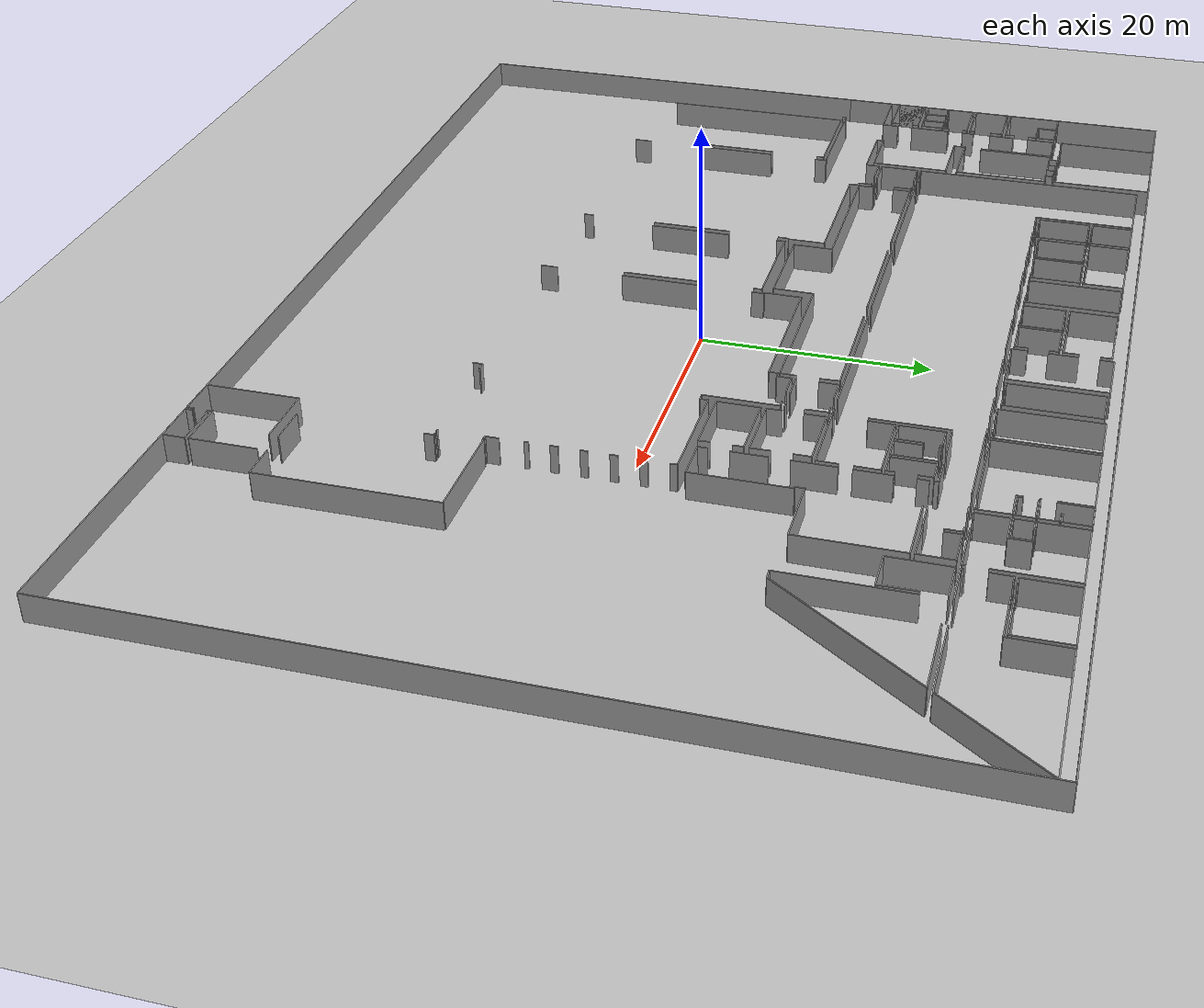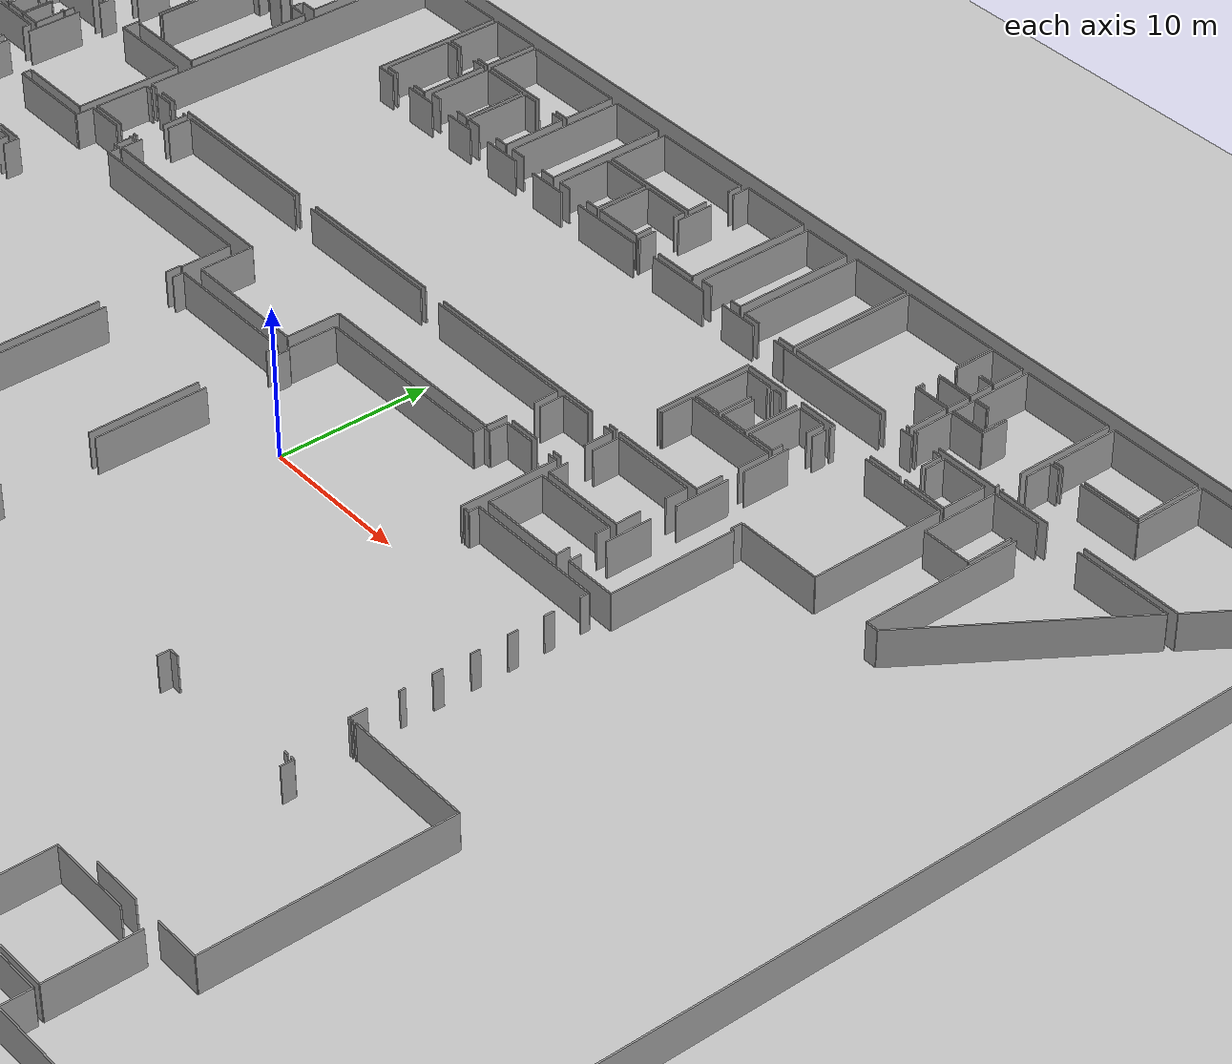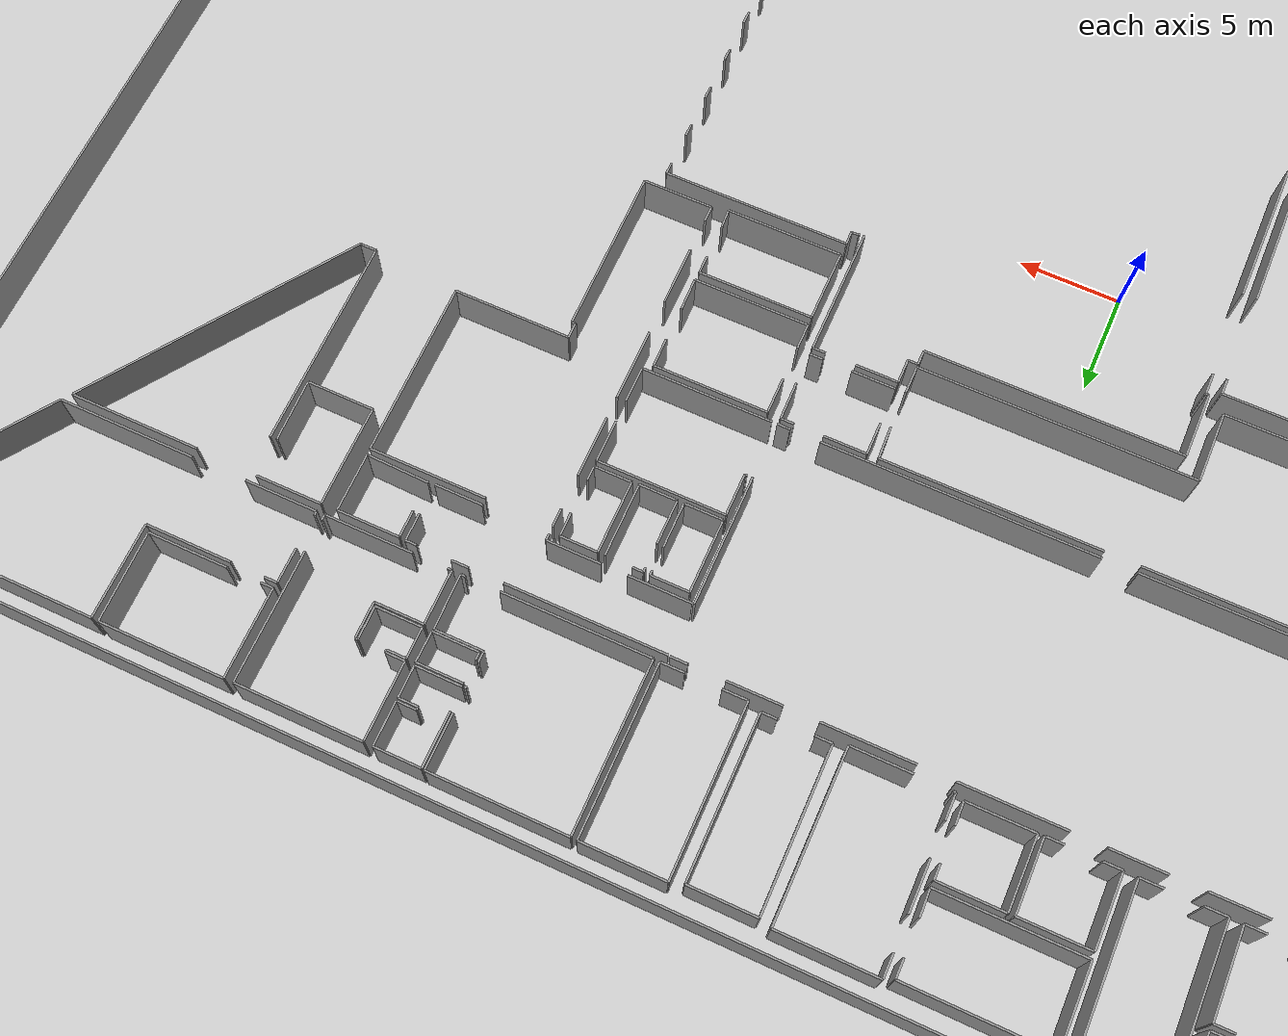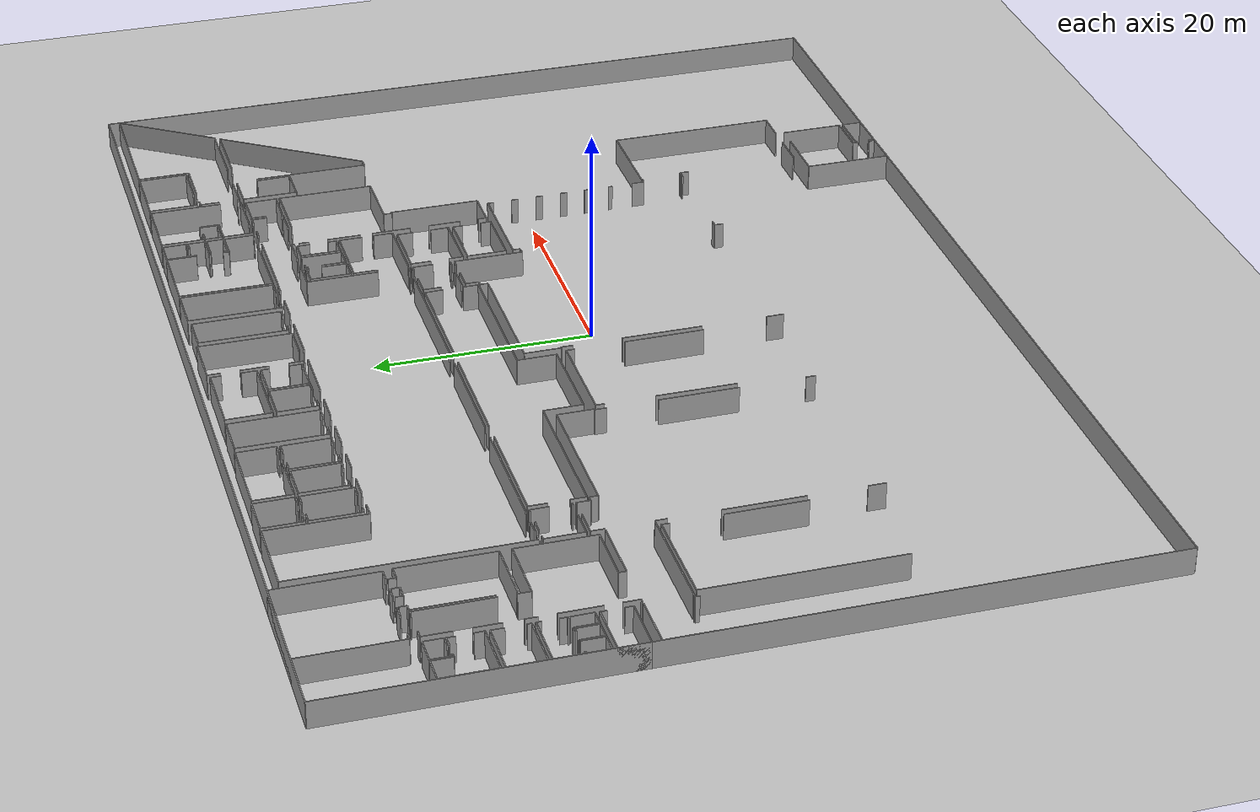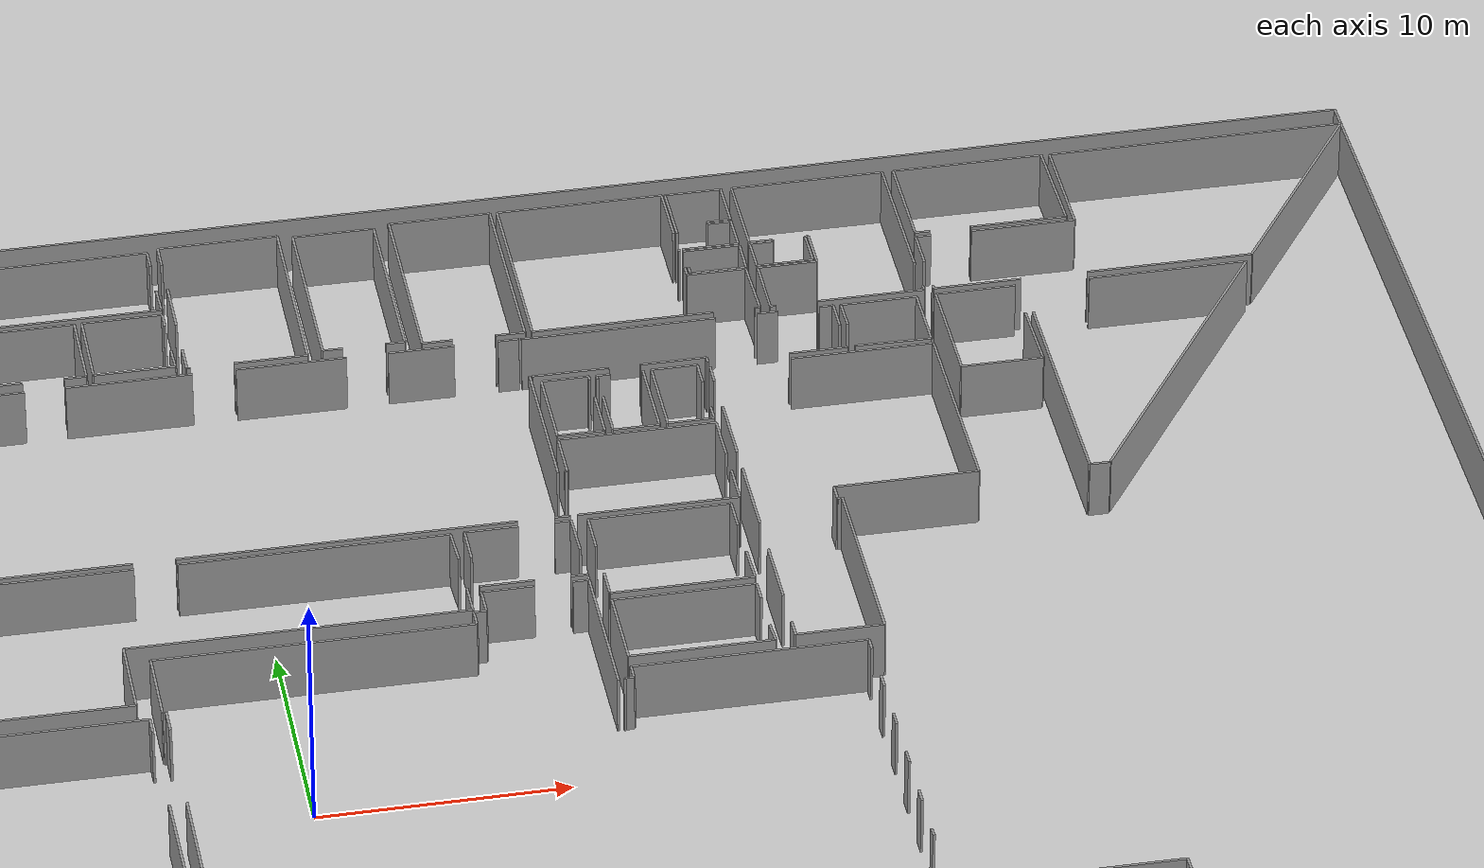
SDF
<sdf version="1.6">
  <world name="default">
    <light name="sun" type="directional">
      <cast_shadows>1</cast_shadows>
      <pose frame="">0 0 10 0 -0 0</pose>
      <diffuse>0.8 0.8 0.8 1</diffuse>
      <specular>0.1 0.1 0.1 1</specular>
      <attenuation>
        <range>1000</range>
        <constant>0.9</constant>
        <linear>0.01</linear>
        <quadratic>0.001</quadratic>
      </attenuation>
      <direction>-0.5 0.5 -1</direction>
    </light>
    <model name="ground_plane">
      <static>1</static>
      <link name="link">
        <collision name="collision">
          <geometry>
            <plane>
              <normal>0 0 1</normal>
              <size>100 100</size>
            </plane>
          </geometry>
          <surface>
            <friction>
              <ode>
                <mu>100</mu>
                <mu2>50</mu2>
              </ode>
              <torsional>
                <ode />
              </torsional>
            </friction>
            <contact>
              <ode />
            </contact>
            <bounce />
          </surface>
          <max_contacts>10</max_contacts>
        </collision>
        <visual name="visual">
          <cast_shadows>0</cast_shadows>
          <geometry>
            <plane>
              <normal>0 0 1</normal>
              <size>100 100</size>
            </plane>
          </geometry>
          <material>
            <script>
              <uri>file://media/materials/scripts/gazebo.material</uri>
              <name>Gazebo/Grey</name>
            </script>
          </material>
        </visual>
        <self_collide>0</self_collide>
        <kinematic>0</kinematic>
        <gravity>1</gravity>
      </link>
    </model>
    <gravity>0 0 -9.8</gravity>
    <magnetic_field>6e-06 2.3e-05 -4.2e-05</magnetic_field>
    <atmosphere type="adiabatic" />
    <physics default="0" name="default_physics" type="ode">
      <max_step_size>0.001</max_step_size>
      <real_time_factor>1</real_time_factor>
      <real_time_update_rate>1000</real_time_update_rate>
    </physics>
    <scene>
      <ambient>0.4 0.4 0.4 1</ambient>
      <background>0.7 0.7 0.7 1</background>
      <shadows>1</shadows>
    </scene>
    <spherical_coordinates>
      <surface_model>EARTH_WGS84</surface_model>
      <latitude_deg>0</latitude_deg>
      <longitude_deg>0</longitude_deg>
      <elevation>0</elevation>
      <heading_deg>0</heading_deg>
    </spherical_coordinates>
  <model name="50053292">
		<static>1</static>
		<link name="Wall_0">
			<collision name="Wall_0_Collision">
				<geometry>
					<box>
						<size>1.1175532962 0.1 2.5</size>
					</box>
				</geometry>
				<pose frame="">0.558776648102 0 1.25 0 0 0</pose>
			</collision>
			<visual name="Wall_0_Visual">
				<pose frame="">0.558776648102 0 1.25 0 0 0</pose>
				<geometry>
					<box>
						<size>1.1175532962 0.1 2.5</size>
					</box>
				</geometry>
				<material>
					<script>
						<uri>file://media/materials/scripts/gazebo.material</uri>
						<name>Gazebo/Grey</name>
					</script>
					<ambient>1 1 1 1</ambient>
				</material>
			</visual>
			<pose frame="">14.6841600569 -9.18695108244 0 0 0 3.14159265359</pose>
		</link>
		<link name="Wall_1">
			<collision name="Wall_1_Collision">
				<geometry>
					<box>
						<size>1.16187948104 0.1 2.5</size>
					</box>
				</geometry>
				<pose frame="">0.58093974052 0 1.25 0 0 0</pose>
			</collision>
			<visual name="Wall_1_Visual">
				<pose frame="">0.58093974052 0 1.25 0 0 0</pose>
				<geometry>
					<box>
						<size>1.16187948104 0.1 2.5</size>
					</box>
				</geometry>
				<material>
					<script>
						<uri>file://media/materials/scripts/gazebo.material</uri>
						<name>Gazebo/Grey</name>
					</script>
					<ambient>1 1 1 1</ambient>
				</material>
			</visual>
			<pose frame="">12.2086251897 -9.18695108244 0 0 0 3.14159265359</pose>
		</link>
		<link name="Wall_2">
			<collision name="Wall_2_Collision">
				<geometry>
					<box>
						<size>1.14016092056 0.1 2.5</size>
					</box>
				</geometry>
				<pose frame="">0.570080460281 0 1.25 0 0 0</pose>
			</collision>
			<visual name="Wall_2_Visual">
				<pose frame="">0.570080460281 0 1.25 0 0 0</pose>
				<geometry>
					<box>
						<size>1.14016092056 0.1 2.5</size>
					</box>
				</geometry>
				<material>
					<script>
						<uri>file://media/materials/scripts/gazebo.material</uri>
						<name>Gazebo/Grey</name>
					</script>
					<ambient>1 1 1 1</ambient>
				</material>
			</visual>
			<pose frame="">9.70337018715 -9.18695108244 0 0 0 3.14159265359</pose>
		</link>
		<link name="Wall_3">
			<collision name="Wall_3_Collision">
				<geometry>
					<box>
						<size>0.717855577923 0.1 2.5</size>
					</box>
				</geometry>
				<pose frame="">0.358927788962 0 1.25 0 0 0</pose>
			</collision>
			<visual name="Wall_3_Visual">
				<pose frame="">0.358927788962 0 1.25 0 0 0</pose>
				<geometry>
					<box>
						<size>0.717855577923 0.1 2.5</size>
					</box>
				</geometry>
				<material>
					<script>
						<uri>file://media/materials/scripts/gazebo.material</uri>
						<name>Gazebo/Grey</name>
					</script>
					<ambient>1 1 1 1</ambient>
				</material>
			</visual>
			<pose frame="">6.18483638049 -9.18695108244 0 0 0 3.14159265359</pose>
		</link>
		<link name="Wall_4">
			<collision name="Wall_4_Collision">
				<geometry>
					<box>
						<size>9.18695108244 0.1 2.5</size>
					</box>
				</geometry>
				<pose frame="">4.59347554122 0 1.25 0 0 0</pose>
			</collision>
			<visual name="Wall_4_Visual">
				<pose frame="">4.59347554122 0 1.25 0 0 0</pose>
				<geometry>
					<box>
						<size>9.18695108244 0.1 2.5</size>
					</box>
				</geometry>
				<material>
					<script>
						<uri>file://media/materials/scripts/gazebo.material</uri>
						<name>Gazebo/Grey</name>
					</script>
					<ambient>1 1 1 1</ambient>
				</material>
			</visual>
			<pose frame="">5.46698080257 -9.18695108244 0 0 0 1.57079632679</pose>
		</link>
		<link name="Wall_5">
			<collision name="Wall_5_Collision">
				<geometry>
					<box>
						<size>9.18885621932 0.1 2.5</size>
					</box>
				</geometry>
				<pose frame="">4.59442810966 0 1.25 0 0 0</pose>
			</collision>
			<visual name="Wall_5_Visual">
				<pose frame="">4.59442810966 0 1.25 0 0 0</pose>
				<geometry>
					<box>
						<size>9.18885621932 0.1 2.5</size>
					</box>
				</geometry>
				<material>
					<script>
						<uri>file://media/materials/scripts/gazebo.material</uri>
						<name>Gazebo/Grey</name>
					</script>
					<ambient>1 1 1 1</ambient>
				</material>
			</visual>
			<pose frame="">5.46698080257 -0.0 0 0 0 0.0</pose>
		</link>
		<link name="Wall_6">
			<collision name="Wall_6_Collision">
				<geometry>
					<box>
						<size>9.18699474177 0.1 2.5</size>
					</box>
				</geometry>
				<pose frame="">4.59349737089 0 1.25 0 0 0</pose>
			</collision>
			<visual name="Wall_6_Visual">
				<pose frame="">4.59349737089 0 1.25 0 0 0</pose>
				<geometry>
					<box>
						<size>9.18699474177 0.1 2.5</size>
					</box>
				</geometry>
				<material>
					<script>
						<uri>file://media/materials/scripts/gazebo.material</uri>
						<name>Gazebo/Grey</name>
					</script>
					<ambient>1 1 1 1</ambient>
				</material>
			</visual>
			<pose frame="">14.6558370219 -0.0 0 0 0 -1.56771337305</pose>
		</link>
		<link name="Wall_7">
			<collision name="Wall_7_Collision">
				<geometry>
					<box>
						<size>5.9284049559 0.1 2.5</size>
					</box>
				</geometry>
				<pose frame="">2.96420247795 0 1.25 0 0 0</pose>
			</collision>
			<visual name="Wall_7_Visual">
				<pose frame="">2.96420247795 0 1.25 0 0 0</pose>
				<geometry>
					<box>
						<size>5.9284049559 0.1 2.5</size>
					</box>
				</geometry>
				<material>
					<script>
						<uri>file://media/materials/scripts/gazebo.material</uri>
						<name>Gazebo/Grey</name>
					</script>
					<ambient>1 1 1 1</ambient>
				</material>
			</visual>
			<pose frame="">15.3491798386 -27.5680927675 0 0 0 3.14159265359</pose>
		</link>
		<link name="Wall_8">
			<collision name="Wall_8_Collision">
				<geometry>
					<box>
						<size>0.65320793299 0.1 2.5</size>
					</box>
				</geometry>
				<pose frame="">0.326603966495 0 1.25 0 0 0</pose>
			</collision>
			<visual name="Wall_8_Visual">
				<pose frame="">0.326603966495 0 1.25 0 0 0</pose>
				<geometry>
					<box>
						<size>0.65320793299 0.1 2.5</size>
					</box>
				</geometry>
				<material>
					<script>
						<uri>file://media/materials/scripts/gazebo.material</uri>
						<name>Gazebo/Grey</name>
					</script>
					<ambient>1 1 1 1</ambient>
				</material>
			</visual>
			<pose frame="">9.42077488268 -27.5680927675 0 0 0 1.57079632679</pose>
		</link>
		<link name="Wall_9">
			<collision name="Wall_9_Collision">
				<geometry>
					<box>
						<size>5.43383142079 0.1 2.5</size>
					</box>
				</geometry>
				<pose frame="">2.71691571039 0 1.25 0 0 0</pose>
			</collision>
			<visual name="Wall_9_Visual">
				<pose frame="">2.71691571039 0 1.25 0 0 0</pose>
				<geometry>
					<box>
						<size>5.43383142079 0.1 2.5</size>
					</box>
				</geometry>
				<material>
					<script>
						<uri>file://media/materials/scripts/gazebo.material</uri>
						<name>Gazebo/Grey</name>
					</script>
					<ambient>1 1 1 1</ambient>
				</material>
			</visual>
			<pose frame="">9.42077488268 -26.9148848345 0 0 0 0.0</pose>
		</link>
		<link name="Wall_10">
			<collision name="Wall_10_Collision">
				<geometry>
					<box>
						<size>7.18871650928 0.1 2.5</size>
					</box>
				</geometry>
				<pose frame="">3.59435825464 0 1.25 0 0 0</pose>
			</collision>
			<visual name="Wall_10_Visual">
				<pose frame="">3.59435825464 0 1.25 0 0 0</pose>
				<geometry>
					<box>
						<size>7.18871650928 0.1 2.5</size>
					</box>
				</geometry>
				<material>
					<script>
						<uri>file://media/materials/scripts/gazebo.material</uri>
						<name>Gazebo/Grey</name>
					</script>
					<ambient>1 1 1 1</ambient>
				</material>
			</visual>
			<pose frame="">14.8546063035 -26.9148848345 0 0 0 1.57079632679</pose>
		</link>
		<link name="Wall_11">
			<collision name="Wall_11_Collision">
				<geometry>
					<box>
						<size>5.99368764646 0.1 2.5</size>
					</box>
				</geometry>
				<pose frame="">2.99684382323 0 1.25 0 0 0</pose>
			</collision>
			<visual name="Wall_11_Visual">
				<pose frame="">2.99684382323 0 1.25 0 0 0</pose>
				<geometry>
					<box>
						<size>5.99368764646 0.1 2.5</size>
					</box>
				</geometry>
				<material>
					<script>
						<uri>file://media/materials/scripts/gazebo.material</uri>
						<name>Gazebo/Grey</name>
					</script>
					<ambient>1 1 1 1</ambient>
				</material>
			</visual>
			<pose frame="">14.8546063035 -19.7261683252 0 0 0 3.14159265359</pose>
		</link>
		<link name="Wall_12">
			<collision name="Wall_12_Collision">
				<geometry>
					<box>
						<size>1.15463996088 0.1 2.5</size>
					</box>
				</geometry>
				<pose frame="">0.577319980441 0 1.25 0 0 0</pose>
			</collision>
			<visual name="Wall_12_Visual">
				<pose frame="">0.577319980441 0 1.25 0 0 0</pose>
				<geometry>
					<box>
						<size>1.15463996088 0.1 2.5</size>
					</box>
				</geometry>
				<material>
					<script>
						<uri>file://media/materials/scripts/gazebo.material</uri>
						<name>Gazebo/Grey</name>
					</script>
					<ambient>1 1 1 1</ambient>
				</material>
			</visual>
			<pose frame="">8.86091865701 -19.7261683252 0 0 0 1.57079632679</pose>
		</link>
		<link name="Wall_13">
			<collision name="Wall_13_Collision">
				<geometry>
					<box>
						<size>6.97940547028 0.1 2.5</size>
					</box>
				</geometry>
				<pose frame="">3.48970273514 0 1.25 0 0 0</pose>
			</collision>
			<visual name="Wall_13_Visual">
				<pose frame="">3.48970273514 0 1.25 0 0 0</pose>
				<geometry>
					<box>
						<size>6.97940547028 0.1 2.5</size>
					</box>
				</geometry>
				<material>
					<script>
						<uri>file://media/materials/scripts/gazebo.material</uri>
						<name>Gazebo/Grey</name>
					</script>
					<ambient>1 1 1 1</ambient>
				</material>
			</visual>
			<pose frame="">8.86091865701 -16.9900107323 0 0 0 1.57079632679</pose>
		</link>
		<link name="Wall_14">
			<collision name="Wall_14_Collision">
				<geometry>
					<box>
						<size>0.307743111343 0.1 2.5</size>
					</box>
				</geometry>
				<pose frame="">0.153871555671 0 1.25 0 0 0</pose>
			</collision>
			<visual name="Wall_14_Visual">
				<pose frame="">0.153871555671 0 1.25 0 0 0</pose>
				<geometry>
					<box>
						<size>0.307743111343 0.1 2.5</size>
					</box>
				</geometry>
				<material>
					<script>
						<uri>file://media/materials/scripts/gazebo.material</uri>
						<name>Gazebo/Grey</name>
					</script>
					<ambient>1 1 1 1</ambient>
				</material>
			</visual>
			<pose frame="">8.86091865701 -10.010605262 0 0 0 3.14159265359</pose>
		</link>
		<link name="Wall_15">
			<collision name="Wall_15_Collision">
				<geometry>
					<box>
						<size>0.701090373343 0.1 2.5</size>
					</box>
				</geometry>
				<pose frame="">0.350545186672 0 1.25 0 0 0</pose>
			</collision>
			<visual name="Wall_15_Visual">
				<pose frame="">0.350545186672 0 1.25 0 0 0</pose>
				<geometry>
					<box>
						<size>0.701090373343 0.1 2.5</size>
					</box>
				</geometry>
				<material>
					<script>
						<uri>file://media/materials/scripts/gazebo.material</uri>
						<name>Gazebo/Grey</name>
					</script>
					<ambient>1 1 1 1</ambient>
				</material>
			</visual>
			<pose frame="">6.20401475846 -10.010605262 0 0 0 3.14159265359</pose>
		</link>
		<link name="Wall_16">
			<collision name="Wall_16_Collision">
				<geometry>
					<box>
						<size>2.61295874109 0.1 2.5</size>
					</box>
				</geometry>
				<pose frame="">1.30647937054 0 1.25 0 0 0</pose>
			</collision>
			<visual name="Wall_16_Visual">
				<pose frame="">1.30647937054 0 1.25 0 0 0</pose>
				<geometry>
					<box>
						<size>2.61295874109 0.1 2.5</size>
					</box>
				</geometry>
				<material>
					<script>
						<uri>file://media/materials/scripts/gazebo.material</uri>
						<name>Gazebo/Grey</name>
					</script>
					<ambient>1 1 1 1</ambient>
				</material>
			</visual>
			<pose frame="">5.50292438512 -10.010605262 0 0 0 -1.57079632679</pose>
		</link>
		<link name="Wall_17">
			<collision name="Wall_17_Collision">
				<geometry>
					<box>
						<size>2.3640208549 0.1 2.5</size>
					</box>
				</geometry>
				<pose frame="">1.18201042745 0 1.25 0 0 0</pose>
			</collision>
			<visual name="Wall_17_Visual">
				<pose frame="">1.18201042745 0 1.25 0 0 0</pose>
				<geometry>
					<box>
						<size>2.3640208549 0.1 2.5</size>
					</box>
				</geometry>
				<material>
					<script>
						<uri>file://media/materials/scripts/gazebo.material</uri>
						<name>Gazebo/Grey</name>
					</script>
					<ambient>1 1 1 1</ambient>
				</material>
			</visual>
			<pose frame="">5.50292438512 -14.1378938077 0 0 0 -1.57079632679</pose>
		</link>
		<link name="Wall_18">
			<collision name="Wall_18_Collision">
				<geometry>
					<box>
						<size>1.09481866272 0.1 2.5</size>
					</box>
				</geometry>
				<pose frame="">0.54740933136 0 1.25 0 0 0</pose>
			</collision>
			<visual name="Wall_18_Visual">
				<pose frame="">0.54740933136 0 1.25 0 0 0</pose>
				<geometry>
					<box>
						<size>1.09481866272 0.1 2.5</size>
					</box>
				</geometry>
				<material>
					<script>
						<uri>file://media/materials/scripts/gazebo.material</uri>
						<name>Gazebo/Grey</name>
					</script>
					<ambient>1 1 1 1</ambient>
				</material>
			</visual>
			<pose frame="">5.50292438512 -18.2240313967 0 0 0 -1.57079632679</pose>
		</link>
		<link name="Wall_19">
			<collision name="Wall_19_Collision">
				<geometry>
					<box>
						<size>3.74600715061 0.1 2.5</size>
					</box>
				</geometry>
				<pose frame="">1.87300357531 0 1.25 0 0 0</pose>
			</collision>
			<visual name="Wall_19_Visual">
				<pose frame="">1.87300357531 0 1.25 0 0 0</pose>
				<geometry>
					<box>
						<size>3.74600715061 0.1 2.5</size>
					</box>
				</geometry>
				<material>
					<script>
						<uri>file://media/materials/scripts/gazebo.material</uri>
						<name>Gazebo/Grey</name>
					</script>
					<ambient>1 1 1 1</ambient>
				</material>
			</visual>
			<pose frame="">5.50292438512 -20.8548984245 0 0 0 -1.57079632679</pose>
		</link>
		<link name="Wall_20">
			<collision name="Wall_20_Collision">
				<geometry>
					<box>
						<size>1.49908870952 0.1 2.5</size>
					</box>
				</geometry>
				<pose frame="">0.749544354762 0 1.25 0 0 0</pose>
			</collision>
			<visual name="Wall_20_Visual">
				<pose frame="">0.749544354762 0 1.25 0 0 0</pose>
				<geometry>
					<box>
						<size>1.49908870952 0.1 2.5</size>
					</box>
				</geometry>
				<material>
					<script>
						<uri>file://media/materials/scripts/gazebo.material</uri>
						<name>Gazebo/Grey</name>
					</script>
					<ambient>1 1 1 1</ambient>
				</material>
			</visual>
			<pose frame="">5.50292438512 -26.0894525272 0 0 0 -1.57079632679</pose>
		</link>
		<link name="Wall_21">
			<collision name="Wall_21_Collision">
				<geometry>
					<box>
						<size>0.345210803396 0.1 2.5</size>
					</box>
				</geometry>
				<pose frame="">0.172605401698 0 1.25 0 0 0</pose>
			</collision>
			<visual name="Wall_21_Visual">
				<pose frame="">0.172605401698 0 1.25 0 0 0</pose>
				<geometry>
					<box>
						<size>0.345210803396 0.1 2.5</size>
					</box>
				</geometry>
				<material>
					<script>
						<uri>file://media/materials/scripts/gazebo.material</uri>
						<name>Gazebo/Grey</name>
					</script>
					<ambient>1 1 1 1</ambient>
				</material>
			</visual>
			<pose frame="">5.50292438512 -27.5885412367 0 0 0 3.14159265359</pose>
		</link>
		<link name="Wall_22">
			<collision name="Wall_22_Collision">
				<geometry>
					<box>
						<size>10.1914746529 0.1 2.5</size>
					</box>
				</geometry>
				<pose frame="">5.09573732647 0 1.25 0 0 0</pose>
			</collision>
			<visual name="Wall_22_Visual">
				<pose frame="">5.09573732647 0 1.25 0 0 0</pose>
				<geometry>
					<box>
						<size>10.1914746529 0.1 2.5</size>
					</box>
				</geometry>
				<material>
					<script>
						<uri>file://media/materials/scripts/gazebo.material</uri>
						<name>Gazebo/Grey</name>
					</script>
					<ambient>1 1 1 1</ambient>
				</material>
			</visual>
			<pose frame="">5.15771358172 -31.7080822257 0 0 0 -0.00128361635341</pose>
		</link>
		<link name="Wall_23">
			<collision name="Wall_23_Collision">
				<geometry>
					<box>
						<size>5.71706177089 0.1 2.5</size>
					</box>
				</geometry>
				<pose frame="">2.85853088544 0 1.25 0 0 0</pose>
			</collision>
			<visual name="Wall_23_Visual">
				<pose frame="">2.85853088544 0 1.25 0 0 0</pose>
				<geometry>
					<box>
						<size>5.71706177089 0.1 2.5</size>
					</box>
				</geometry>
				<material>
					<script>
						<uri>file://media/materials/scripts/gazebo.material</uri>
						<name>Gazebo/Grey</name>
					</script>
					<ambient>1 1 1 1</ambient>
				</material>
			</visual>
			<pose frame="">14.8231080403 -18.6576405515 0 0 0 3.14159265359</pose>
		</link>
		<link name="Wall_24">
			<collision name="Wall_24_Collision">
				<geometry>
					<box>
						<size>0.085350132407 0.1 2.5</size>
					</box>
				</geometry>
				<pose frame="">0.0426750662035 0 1.25 0 0 0</pose>
			</collision>
			<visual name="Wall_24_Visual">
				<pose frame="">0.0426750662035 0 1.25 0 0 0</pose>
				<geometry>
					<box>
						<size>0.085350132407 0.1 2.5</size>
					</box>
				</geometry>
				<material>
					<script>
						<uri>file://media/materials/scripts/gazebo.material</uri>
						<name>Gazebo/Grey</name>
					</script>
					<ambient>1 1 1 1</ambient>
				</material>
			</visual>
			<pose frame="">9.10604626942 -18.6576405515 0 0 0 1.57079632679</pose>
		</link>
		<link name="Wall_25">
			<collision name="Wall_25_Collision">
				<geometry>
					<box>
						<size>6.95108243527 0.1 2.5</size>
					</box>
				</geometry>
				<pose frame="">3.47554121764 0 1.25 0 0 0</pose>
			</collision>
			<visual name="Wall_25_Visual">
				<pose frame="">3.47554121764 0 1.25 0 0 0</pose>
				<geometry>
					<box>
						<size>6.95108243527 0.1 2.5</size>
					</box>
				</geometry>
				<material>
					<script>
						<uri>file://media/materials/scripts/gazebo.material</uri>
						<name>Gazebo/Grey</name>
					</script>
					<ambient>1 1 1 1</ambient>
				</material>
			</visual>
			<pose frame="">9.10604626942 -16.9550832227 0 0 0 1.57079632679</pose>
		</link>
		<link name="Wall_26">
			<collision name="Wall_26_Collision">
				<geometry>
					<box>
						<size>0.584495996037 0.1 2.5</size>
					</box>
				</geometry>
				<pose frame="">0.292247998019 0 1.25 0 0 0</pose>
			</collision>
			<visual name="Wall_26_Visual">
				<pose frame="">0.292247998019 0 1.25 0 0 0</pose>
				<geometry>
					<box>
						<size>0.584495996037 0.1 2.5</size>
					</box>
				</geometry>
				<material>
					<script>
						<uri>file://media/materials/scripts/gazebo.material</uri>
						<name>Gazebo/Grey</name>
					</script>
					<ambient>1 1 1 1</ambient>
				</material>
			</visual>
			<pose frame="">9.10604626942 -10.0040007875 0 0 0 0.0</pose>
		</link>
		<link name="Wall_27">
			<collision name="Wall_27_Collision">
				<geometry>
					<box>
						<size>0.676704621227 0.1 2.5</size>
					</box>
				</geometry>
				<pose frame="">0.338352310614 0 1.25 0 0 0</pose>
			</collision>
			<visual name="Wall_27_Visual">
				<pose frame="">0.338352310614 0 1.25 0 0 0</pose>
				<geometry>
					<box>
						<size>0.676704621227 0.1 2.5</size>
					</box>
				</geometry>
				<material>
					<script>
						<uri>file://media/materials/scripts/gazebo.material</uri>
						<name>Gazebo/Grey</name>
					</script>
					<ambient>1 1 1 1</ambient>
				</material>
			</visual>
			<pose frame="">9.69054226546 -10.0040007875 0 0 0 1.57079632679</pose>
		</link>
		<link name="Wall_28">
			<collision name="Wall_28_Collision">
				<geometry>
					<box>
						<size>0.672767338333 0.1 2.5</size>
					</box>
				</geometry>
				<pose frame="">0.336383669167 0 1.25 0 0 0</pose>
			</collision>
			<visual name="Wall_28_Visual">
				<pose frame="">0.336383669167 0 1.25 0 0 0</pose>
				<geometry>
					<box>
						<size>0.672767338333 0.1 2.5</size>
					</box>
				</geometry>
				<material>
					<script>
						<uri>file://media/materials/scripts/gazebo.material</uri>
						<name>Gazebo/Grey</name>
					</script>
					<ambient>1 1 1 1</ambient>
				</material>
			</visual>
			<pose frame="">11.0334097505 -9.32729616623 0 0 0 -1.57079632679</pose>
		</link>
		<link name="Wall_29">
			<collision name="Wall_29_Collision">
				<geometry>
					<box>
						<size>1.1750884301 0.1 2.5</size>
					</box>
				</geometry>
				<pose frame="">0.587544215052 0 1.25 0 0 0</pose>
			</collision>
			<visual name="Wall_29_Visual">
				<pose frame="">0.587544215052 0 1.25 0 0 0</pose>
				<geometry>
					<box>
						<size>1.1750884301 0.1 2.5</size>
					</box>
				</geometry>
				<material>
					<script>
						<uri>file://media/materials/scripts/gazebo.material</uri>
						<name>Gazebo/Grey</name>
					</script>
					<ambient>1 1 1 1</ambient>
				</material>
			</visual>
			<pose frame="">11.0334097505 -10.0000635046 0 0 0 0.0</pose>
		</link>
		<link name="Wall_30">
			<collision name="Wall_30_Collision">
				<geometry>
					<box>
						<size>0.658923343642 0.1 2.5</size>
					</box>
				</geometry>
				<pose frame="">0.329461671821 0 1.25 0 0 0</pose>
			</collision>
			<visual name="Wall_30_Visual">
				<pose frame="">0.329461671821 0 1.25 0 0 0</pose>
				<geometry>
					<box>
						<size>0.658923343642 0.1 2.5</size>
					</box>
				</geometry>
				<material>
					<script>
						<uri>file://media/materials/scripts/gazebo.material</uri>
						<name>Gazebo/Grey</name>
					</script>
					<ambient>1 1 1 1</ambient>
				</material>
			</visual>
			<pose frame="">12.2084981806 -10.0000635046 0 0 0 1.57079632679</pose>
		</link>
		<link name="Wall_31">
			<collision name="Wall_31_Collision">
				<geometry>
					<box>
						<size>0.664384736043 0.1 2.5</size>
					</box>
				</geometry>
				<pose frame="">0.332192368022 0 1.25 0 0 0</pose>
			</collision>
			<visual name="Wall_31_Visual">
				<pose frame="">0.332192368022 0 1.25 0 0 0</pose>
				<geometry>
					<box>
						<size>0.664384736043 0.1 2.5</size>
					</box>
				</geometry>
				<material>
					<script>
						<uri>file://media/materials/scripts/gazebo.material</uri>
						<name>Gazebo/Grey</name>
					</script>
					<ambient>1 1 1 1</ambient>
				</material>
			</visual>
			<pose frame="">13.5263448679 -9.34114016092 0 0 0 -1.57079632679</pose>
		</link>
		<link name="Wall_32">
			<collision name="Wall_32_Collision">
				<geometry>
					<box>
						<size>1.29041271615 0.1 2.5</size>
					</box>
				</geometry>
				<pose frame="">0.645206358077 0 1.25 0 0 0</pose>
			</collision>
			<visual name="Wall_32_Visual">
				<pose frame="">0.645206358077 0 1.25 0 0 0</pose>
				<geometry>
					<box>
						<size>1.29041271615 0.1 2.5</size>
					</box>
				</geometry>
				<material>
					<script>
						<uri>file://media/materials/scripts/gazebo.material</uri>
						<name>Gazebo/Grey</name>
					</script>
					<ambient>1 1 1 1</ambient>
				</material>
			</visual>
			<pose frame="">13.5263448679 -10.005524897 0 0 0 0.0</pose>
		</link>
		<link name="Wall_33">
			<collision name="Wall_33_Collision">
				<geometry>
					<box>
						<size>8.65211798505 0.1 2.5</size>
					</box>
				</geometry>
				<pose frame="">4.32605899253 0 1.25 0 0 0</pose>
			</collision>
			<visual name="Wall_33_Visual">
				<pose frame="">4.32605899253 0 1.25 0 0 0</pose>
				<geometry>
					<box>
						<size>8.65211798505 0.1 2.5</size>
					</box>
				</geometry>
				<material>
					<script>
						<uri>file://media/materials/scripts/gazebo.material</uri>
						<name>Gazebo/Grey</name>
					</script>
					<ambient>1 1 1 1</ambient>
				</material>
			</visual>
			<pose frame="">14.816757584 -10.005524897 0 0 0 -1.57006234965</pose>
		</link>
		<link name="Wall_34">
			<collision name="Wall_34_Collision">
				<geometry>
					<box>
						<size>4.82431462701 0.1 2.5</size>
					</box>
				</geometry>
				<pose frame="">2.4121573135 0 1.25 0 0 0</pose>
			</collision>
			<visual name="Wall_34_Visual">
				<pose frame="">2.4121573135 0 1.25 0 0 0</pose>
				<geometry>
					<box>
						<size>4.82431462701 0.1 2.5</size>
					</box>
				</geometry>
				<material>
					<script>
						<uri>file://media/materials/scripts/gazebo.material</uri>
						<name>Gazebo/Grey</name>
					</script>
					<ambient>1 1 1 1</ambient>
				</material>
			</visual>
			<pose frame="">4.86114727343 -14.9540544488 0 0 0 3.14159265359</pose>
		</link>
		<link name="Wall_35">
			<collision name="Wall_35_Collision">
				<geometry>
					<box>
						<size>4.92871612825 0.1 2.5</size>
					</box>
				</geometry>
				<pose frame="">2.46435806413 0 1.25 0 0 0</pose>
			</collision>
			<visual name="Wall_35_Visual">
				<pose frame="">2.46435806413 0 1.25 0 0 0</pose>
				<geometry>
					<box>
						<size>4.92871612825 0.1 2.5</size>
					</box>
				</geometry>
				<material>
					<script>
						<uri>file://media/materials/scripts/gazebo.material</uri>
						<name>Gazebo/Grey</name>
					</script>
					<ambient>1 1 1 1</ambient>
				</material>
			</visual>
			<pose frame="">0.0368326464256 -14.9540544488 0 0 0 1.57079632679</pose>
		</link>
		<link name="Wall_36">
			<collision name="Wall_36_Collision">
				<geometry>
					<box>
						<size>2.28654528828 0.1 2.5</size>
					</box>
				</geometry>
				<pose frame="">1.14327264414 0 1.25 0 0 0</pose>
			</collision>
			<visual name="Wall_36_Visual">
				<pose frame="">1.14327264414 0 1.25 0 0 0</pose>
				<geometry>
					<box>
						<size>2.28654528828 0.1 2.5</size>
					</box>
				</geometry>
				<material>
					<script>
						<uri>file://media/materials/scripts/gazebo.material</uri>
						<name>Gazebo/Grey</name>
					</script>
					<ambient>1 1 1 1</ambient>
				</material>
			</visual>
			<pose frame="">0.0368326464256 -10.0253383206 0 0 0 0.0</pose>
		</link>
		<link name="Wall_37">
			<collision name="Wall_37_Collision">
				<geometry>
					<box>
						<size>1.86906629241 0.1 2.5</size>
					</box>
				</geometry>
				<pose frame="">0.934533146207 0 1.25 0 0 0</pose>
			</collision>
			<visual name="Wall_37_Visual">
				<pose frame="">0.934533146207 0 1.25 0 0 0</pose>
				<geometry>
					<box>
						<size>1.86906629241 0.1 2.5</size>
					</box>
				</geometry>
				<material>
					<script>
						<uri>file://media/materials/scripts/gazebo.material</uri>
						<name>Gazebo/Grey</name>
					</script>
					<ambient>1 1 1 1</ambient>
				</material>
			</visual>
			<pose frame="">2.3233779347 -10.0253383206 0 0 0 -1.57079632679</pose>
		</link>
		<link name="Wall_38">
			<collision name="Wall_38_Collision">
				<geometry>
					<box>
						<size>0.342543611759 0.1 2.5</size>
					</box>
				</geometry>
				<pose frame="">0.171271805879 0 1.25 0 0 0</pose>
			</collision>
			<visual name="Wall_38_Visual">
				<pose frame="">0.171271805879 0 1.25 0 0 0</pose>
				<geometry>
					<box>
						<size>0.342543611759 0.1 2.5</size>
					</box>
				</geometry>
				<material>
					<script>
						<uri>file://media/materials/scripts/gazebo.material</uri>
						<name>Gazebo/Grey</name>
					</script>
					<ambient>1 1 1 1</ambient>
				</material>
			</visual>
			<pose frame="">2.3233779347 -11.894404613 0 0 0 0.0</pose>
		</link>
		<link name="Wall_39">
			<collision name="Wall_39_Collision">
				<geometry>
					<box>
						<size>0.979748394922 0.1 2.5</size>
					</box>
				</geometry>
				<pose frame="">0.489874197461 0 1.25 0 0 0</pose>
			</collision>
			<visual name="Wall_39_Visual">
				<pose frame="">0.489874197461 0 1.25 0 0 0</pose>
				<geometry>
					<box>
						<size>0.979748394922 0.1 2.5</size>
					</box>
				</geometry>
				<material>
					<script>
						<uri>file://media/materials/scripts/gazebo.material</uri>
						<name>Gazebo/Grey</name>
					</script>
					<ambient>1 1 1 1</ambient>
				</material>
			</visual>
			<pose frame="">3.84621735072 -11.894404613 0 0 0 0.0</pose>
		</link>
		<link name="Wall_40">
			<collision name="Wall_40_Collision">
				<geometry>
					<box>
						<size>0.760784662378 0.1 2.5</size>
					</box>
				</geometry>
				<pose frame="">0.380392331189 0 1.25 0 0 0</pose>
			</collision>
			<visual name="Wall_40_Visual">
				<pose frame="">0.380392331189 0 1.25 0 0 0</pose>
				<geometry>
					<box>
						<size>0.760784662378 0.1 2.5</size>
					</box>
				</geometry>
				<material>
					<script>
						<uri>file://media/materials/scripts/gazebo.material</uri>
						<name>Gazebo/Grey</name>
					</script>
					<ambient>1 1 1 1</ambient>
				</material>
			</visual>
			<pose frame="">4.82596574564 -11.894404613 0 0 0 -1.57079632679</pose>
		</link>
		<link name="Wall_41">
			<collision name="Wall_41_Collision">
				<geometry>
					<box>
						<size>0.873261668576 0.1 2.5</size>
					</box>
				</geometry>
				<pose frame="">0.436630834288 0 1.25 0 0 0</pose>
			</collision>
			<visual name="Wall_41_Visual">
				<pose frame="">0.436630834288 0 1.25 0 0 0</pose>
				<geometry>
					<box>
						<size>0.873261668576 0.1 2.5</size>
					</box>
				</geometry>
				<material>
					<script>
						<uri>file://media/materials/scripts/gazebo.material</uri>
						<name>Gazebo/Grey</name>
					</script>
					<ambient>1 1 1 1</ambient>
				</material>
			</visual>
			<pose frame="">4.82596574564 -14.0815017559 0 0 0 -1.53049792243</pose>
		</link>
		<link name="Wall_42">
			<collision name="Wall_42_Collision">
				<geometry>
					<box>
						<size>0.990163143222 0.1 2.5</size>
					</box>
				</geometry>
				<pose frame="">0.495081571611 0 1.25 0 0 0</pose>
			</collision>
			<visual name="Wall_42_Visual">
				<pose frame="">0.495081571611 0 1.25 0 0 0</pose>
				<geometry>
					<box>
						<size>0.990163143222 0.1 2.5</size>
					</box>
				</geometry>
				<material>
					<script>
						<uri>file://media/materials/scripts/gazebo.material</uri>
						<name>Gazebo/Grey</name>
					</script>
					<ambient>1 1 1 1</ambient>
				</material>
			</visual>
			<pose frame="">4.85238364376 -11.759901949 0 0 0 3.14159265359</pose>
		</link>
		<link name="Wall_43">
			<collision name="Wall_43_Collision">
				<geometry>
					<box>
						<size>0.206389829109 0.1 2.5</size>
					</box>
				</geometry>
				<pose frame="">0.103194914555 0 1.25 0 0 0</pose>
			</collision>
			<visual name="Wall_43_Visual">
				<pose frame="">0.103194914555 0 1.25 0 0 0</pose>
				<geometry>
					<box>
						<size>0.206389829109 0.1 2.5</size>
					</box>
				</geometry>
				<material>
					<script>
						<uri>file://media/materials/scripts/gazebo.material</uri>
						<name>Gazebo/Grey</name>
					</script>
					<ambient>1 1 1 1</ambient>
				</material>
			</visual>
			<pose frame="">2.69373654497 -11.759901949 0 0 0 3.14159265359</pose>
		</link>
		<link name="Wall_44">
			<collision name="Wall_44_Collision">
				<geometry>
					<box>
						<size>1.74701052271 0.1 2.5</size>
					</box>
				</geometry>
				<pose frame="">0.873505261353 0 1.25 0 0 0</pose>
			</collision>
			<visual name="Wall_44_Visual">
				<pose frame="">0.873505261353 0 1.25 0 0 0</pose>
				<geometry>
					<box>
						<size>1.74701052271 0.1 2.5</size>
					</box>
				</geometry>
				<material>
					<script>
						<uri>file://media/materials/scripts/gazebo.material</uri>
						<name>Gazebo/Grey</name>
					</script>
					<ambient>1 1 1 1</ambient>
				</material>
			</visual>
			<pose frame="">2.48734671586 -11.759901949 0 0 0 1.57079632679</pose>
		</link>
		<link name="Wall_45">
			<collision name="Wall_45_Collision">
				<geometry>
					<box>
						<size>2.36262375452 0.1 2.5</size>
					</box>
				</geometry>
				<pose frame="">1.18131187726 0 1.25 0 0 0</pose>
			</collision>
			<visual name="Wall_45_Visual">
				<pose frame="">1.18131187726 0 1.25 0 0 0</pose>
				<geometry>
					<box>
						<size>2.36262375452 0.1 2.5</size>
					</box>
				</geometry>
				<material>
					<script>
						<uri>file://media/materials/scripts/gazebo.material</uri>
						<name>Gazebo/Grey</name>
					</script>
					<ambient>1 1 1 1</ambient>
				</material>
			</visual>
			<pose frame="">2.48734671586 -10.0128914262 0 0 0 0.0</pose>
		</link>
		<link name="Wall_46">
			<collision name="Wall_46_Collision">
				<geometry>
					<box>
						<size>1.74701218938 0.1 2.5</size>
					</box>
				</geometry>
				<pose frame="">0.873506094691 0 1.25 0 0 0</pose>
			</collision>
			<visual name="Wall_46_Visual">
				<pose frame="">0.873506094691 0 1.25 0 0 0</pose>
				<geometry>
					<box>
						<size>1.74701218938 0.1 2.5</size>
					</box>
				</geometry>
				<material>
					<script>
						<uri>file://media/materials/scripts/gazebo.material</uri>
						<name>Gazebo/Grey</name>
					</script>
					<ambient>1 1 1 1</ambient>
				</material>
			</visual>
			<pose frame="">4.84997047038 -10.0128914262 0 0 0 -1.56941501179</pose>
		</link>
		<link name="Wall_47">
			<collision name="Wall_47_Collision">
				<geometry>
					<box>
						<size>4.80729540417 0.1 2.5</size>
					</box>
				</geometry>
				<pose frame="">2.40364770209 0 1.25 0 0 0</pose>
			</collision>
			<visual name="Wall_47_Visual">
				<pose frame="">2.40364770209 0 1.25 0 0 0</pose>
				<geometry>
					<box>
						<size>4.80729540417 0.1 2.5</size>
					</box>
				</geometry>
				<material>
					<script>
						<uri>file://media/materials/scripts/gazebo.material</uri>
						<name>Gazebo/Grey</name>
					</script>
					<ambient>1 1 1 1</ambient>
				</material>
			</visual>
			<pose frame="">4.82342556313 -18.6295715347 0 0 0 3.14159265359</pose>
		</link>
		<link name="Wall_48">
			<collision name="Wall_48_Collision">
				<geometry>
					<box>
						<size>3.29677587335 0.1 2.5</size>
					</box>
				</geometry>
				<pose frame="">1.64838793667 0 1.25 0 0 0</pose>
			</collision>
			<visual name="Wall_48_Visual">
				<pose frame="">1.64838793667 0 1.25 0 0 0</pose>
				<geometry>
					<box>
						<size>3.29677587335 0.1 2.5</size>
					</box>
				</geometry>
				<material>
					<script>
						<uri>file://media/materials/scripts/gazebo.material</uri>
						<name>Gazebo/Grey</name>
					</script>
					<ambient>1 1 1 1</ambient>
				</material>
			</visual>
			<pose frame="">0.0161301589519 -18.6295715347 0 0 0 1.57079632679</pose>
		</link>
		<link name="Wall_49">
			<collision name="Wall_49_Collision">
				<geometry>
					<box>
						<size>4.81453492433 0.1 2.5</size>
					</box>
				</geometry>
				<pose frame="">2.40726746217 0 1.25 0 0 0</pose>
			</collision>
			<visual name="Wall_49_Visual">
				<pose frame="">2.40726746217 0 1.25 0 0 0</pose>
				<geometry>
					<box>
						<size>4.81453492433 0.1 2.5</size>
					</box>
				</geometry>
				<material>
					<script>
						<uri>file://media/materials/scripts/gazebo.material</uri>
						<name>Gazebo/Grey</name>
					</script>
					<ambient>1 1 1 1</ambient>
				</material>
			</visual>
			<pose frame="">0.0161301589519 -15.3327956614 0 0 0 0.0</pose>
		</link>
		<link name="Wall_50">
			<collision name="Wall_50_Collision">
				<geometry>
					<box>
						<size>1.17635852136 0.1 2.5</size>
					</box>
				</geometry>
				<pose frame="">0.58817926068 0 1.25 0 0 0</pose>
			</collision>
			<visual name="Wall_50_Visual">
				<pose frame="">0.58817926068 0 1.25 0 0 0</pose>
				<geometry>
					<box>
						<size>1.17635852136 0.1 2.5</size>
					</box>
				</geometry>
				<material>
					<script>
						<uri>file://media/materials/scripts/gazebo.material</uri>
						<name>Gazebo/Grey</name>
					</script>
					<ambient>1 1 1 1</ambient>
				</material>
			</visual>
			<pose frame="">4.83066508329 -15.3327956614 0 0 0 -1.57079632679</pose>
		</link>
		<link name="Wall_51">
			<collision name="Wall_51_Collision">
				<geometry>
					<box>
						<size>0.374619869722 0.1 2.5</size>
					</box>
				</geometry>
				<pose frame="">0.187309934861 0 1.25 0 0 0</pose>
			</collision>
			<visual name="Wall_51_Visual">
				<pose frame="">0.187309934861 0 1.25 0 0 0</pose>
				<geometry>
					<box>
						<size>0.374619869722 0.1 2.5</size>
					</box>
				</geometry>
				<material>
					<script>
						<uri>file://media/materials/scripts/gazebo.material</uri>
						<name>Gazebo/Grey</name>
					</script>
					<ambient>1 1 1 1</ambient>
				</material>
			</visual>
			<pose frame="">4.83066508329 -18.2550216233 0 0 0 -1.59012250628</pose>
		</link>
		<link name="Wall_52">
			<collision name="Wall_52_Collision">
				<geometry>
					<box>
						<size>0.25058900482 0.1 2.5</size>
					</box>
				</geometry>
				<pose frame="">0.12529450241 0 1.25 0 0 0</pose>
			</collision>
			<visual name="Wall_52_Visual">
				<pose frame="">0.12529450241 0 1.25 0 0 0</pose>
				<geometry>
					<box>
						<size>0.25058900482 0.1 2.5</size>
					</box>
				</geometry>
				<material>
					<script>
						<uri>file://media/materials/scripts/gazebo.material</uri>
						<name>Gazebo/Grey</name>
					</script>
					<ambient>1 1 1 1</ambient>
				</material>
			</visual>
			<pose frame="">4.8386666582 -21.5034070198 0 0 0 3.14159265359</pose>
		</link>
		<link name="Wall_53">
			<collision name="Wall_53_Collision">
				<geometry>
					<box>
						<size>0.480221503915 0.1 2.5</size>
					</box>
				</geometry>
				<pose frame="">0.240110751958 0 1.25 0 0 0</pose>
			</collision>
			<visual name="Wall_53_Visual">
				<pose frame="">0.240110751958 0 1.25 0 0 0</pose>
				<geometry>
					<box>
						<size>0.480221503915 0.1 2.5</size>
					</box>
				</geometry>
				<material>
					<script>
						<uri>file://media/materials/scripts/gazebo.material</uri>
						<name>Gazebo/Grey</name>
					</script>
					<ambient>1 1 1 1</ambient>
				</material>
			</visual>
			<pose frame="">3.39978027421 -21.5034070198 0 0 0 3.14159265359</pose>
		</link>
		<link name="Wall_54">
			<collision name="Wall_54_Collision">
				<geometry>
					<box>
						<size>0.105544583378 0.1 2.5</size>
					</box>
				</geometry>
				<pose frame="">0.0527722916892 0 1.25 0 0 0</pose>
			</collision>
			<visual name="Wall_54_Visual">
				<pose frame="">0.0527722916892 0 1.25 0 0 0</pose>
				<geometry>
					<box>
						<size>0.105544583378 0.1 2.5</size>
					</box>
				</geometry>
				<material>
					<script>
						<uri>file://media/materials/scripts/gazebo.material</uri>
						<name>Gazebo/Grey</name>
					</script>
					<ambient>1 1 1 1</ambient>
				</material>
			</visual>
			<pose frame="">1.76707796455 -21.5034070198 0 0 0 3.14159265359</pose>
		</link>
		<link name="Wall_55">
			<collision name="Wall_55_Collision">
				<geometry>
					<box>
						<size>0.225568207076 0.1 2.5</size>
					</box>
				</geometry>
				<pose frame="">0.112784103538 0 1.25 0 0 0</pose>
			</collision>
			<visual name="Wall_55_Visual">
				<pose frame="">0.112784103538 0 1.25 0 0 0</pose>
				<geometry>
					<box>
						<size>0.225568207076 0.1 2.5</size>
					</box>
				</geometry>
				<material>
					<script>
						<uri>file://media/materials/scripts/gazebo.material</uri>
						<name>Gazebo/Grey</name>
					</script>
					<ambient>1 1 1 1</ambient>
				</material>
			</visual>
			<pose frame="">0.237253046631 -21.5034070198 0 0 0 3.14159265359</pose>
		</link>
		<link name="Wall_56">
			<collision name="Wall_56_Collision">
				<geometry>
					<box>
						<size>2.53027580032 0.1 2.5</size>
					</box>
				</geometry>
				<pose frame="">1.26513790016 0 1.25 0 0 0</pose>
			</collision>
			<visual name="Wall_56_Visual">
				<pose frame="">1.26513790016 0 1.25 0 0 0</pose>
				<geometry>
					<box>
						<size>2.53027580032 0.1 2.5</size>
					</box>
				</geometry>
				<material>
					<script>
						<uri>file://media/materials/scripts/gazebo.material</uri>
						<name>Gazebo/Grey</name>
					</script>
					<ambient>1 1 1 1</ambient>
				</material>
			</visual>
			<pose frame="">0.0116848395557 -21.5034070198 0 0 0 1.57079632679</pose>
		</link>
		<link name="Wall_57">
			<collision name="Wall_57_Collision">
				<geometry>
					<box>
						<size>4.82698181864 0.1 2.5</size>
					</box>
				</geometry>
				<pose frame="">2.41349090932 0 1.25 0 0 0</pose>
			</collision>
			<visual name="Wall_57_Visual">
				<pose frame="">2.41349090932 0 1.25 0 0 0</pose>
				<geometry>
					<box>
						<size>4.82698181864 0.1 2.5</size>
					</box>
				</geometry>
				<material>
					<script>
						<uri>file://media/materials/scripts/gazebo.material</uri>
						<name>Gazebo/Grey</name>
					</script>
					<ambient>1 1 1 1</ambient>
				</material>
			</visual>
			<pose frame="">0.0116848395557 -18.9731312195 0 0 0 0.0</pose>
		</link>
		<link name="Wall_58">
			<collision name="Wall_58_Collision">
				<geometry>
					<box>
						<size>0.434244200446 0.1 2.5</size>
					</box>
				</geometry>
				<pose frame="">0.217122100223 0 1.25 0 0 0</pose>
			</collision>
			<visual name="Wall_58_Visual">
				<pose frame="">0.217122100223 0 1.25 0 0 0</pose>
				<geometry>
					<box>
						<size>0.434244200446 0.1 2.5</size>
					</box>
				</geometry>
				<material>
					<script>
						<uri>file://media/materials/scripts/gazebo.material</uri>
						<name>Gazebo/Grey</name>
					</script>
					<ambient>1 1 1 1</ambient>
				</material>
			</visual>
			<pose frame="">4.8386666582 -18.9731312195 0 0 0 -1.57079632679</pose>
		</link>
		<link name="Wall_59">
			<collision name="Wall_59_Collision">
				<geometry>
					<box>
						<size>0.68470619614 0.1 2.5</size>
					</box>
				</geometry>
				<pose frame="">0.34235309807 0 1.25 0 0 0</pose>
			</collision>
			<visual name="Wall_59_Visual">
				<pose frame="">0.34235309807 0 1.25 0 0 0</pose>
				<geometry>
					<box>
						<size>0.68470619614 0.1 2.5</size>
					</box>
				</geometry>
				<material>
					<script>
						<uri>file://media/materials/scripts/gazebo.material</uri>
						<name>Gazebo/Grey</name>
					</script>
					<ambient>1 1 1 1</ambient>
				</material>
			</visual>
			<pose frame="">4.8386666582 -20.8187008237 0 0 0 -1.57079632679</pose>
		</link>
		<link name="Wall_60">
			<collision name="Wall_60_Collision">
				<geometry>
					<box>
						<size>1.42580444405 0.1 2.5</size>
					</box>
				</geometry>
				<pose frame="">0.712902222025 0 1.25 0 0 0</pose>
			</collision>
			<visual name="Wall_60_Visual">
				<pose frame="">0.712902222025 0 1.25 0 0 0</pose>
				<geometry>
					<box>
						<size>1.42580444405 0.1 2.5</size>
					</box>
				</geometry>
				<material>
					<script>
						<uri>file://media/materials/scripts/gazebo.material</uri>
						<name>Gazebo/Grey</name>
					</script>
					<ambient>1 1 1 1</ambient>
				</material>
			</visual>
			<pose frame="">4.85975017305 -23.6765331589 0 0 0 3.14159265359</pose>
		</link>
		<link name="Wall_61">
			<collision name="Wall_61_Collision">
				<geometry>
					<box>
						<size>2.06326324546 0.1 2.5</size>
					</box>
				</geometry>
				<pose frame="">1.03163162273 0 1.25 0 0 0</pose>
			</collision>
			<visual name="Wall_61_Visual">
				<pose frame="">1.03163162273 0 1.25 0 0 0</pose>
				<geometry>
					<box>
						<size>2.06326324546 0.1 2.5</size>
					</box>
				</geometry>
				<material>
					<script>
						<uri>file://media/materials/scripts/gazebo.material</uri>
						<name>Gazebo/Grey</name>
					</script>
					<ambient>1 1 1 1</ambient>
				</material>
			</visual>
			<pose frame="">3.433945729 -23.6765331589 0 0 0 1.57079632679</pose>
		</link>
		<link name="Wall_62">
			<collision name="Wall_62_Collision">
				<geometry>
					<box>
						<size>0.225187179699 0.1 2.5</size>
					</box>
				</geometry>
				<pose frame="">0.112593589849 0 1.25 0 0 0</pose>
			</collision>
			<visual name="Wall_62_Visual">
				<pose frame="">0.112593589849 0 1.25 0 0 0</pose>
				<geometry>
					<box>
						<size>0.225187179699 0.1 2.5</size>
					</box>
				</geometry>
				<material>
					<script>
						<uri>file://media/materials/scripts/gazebo.material</uri>
						<name>Gazebo/Grey</name>
					</script>
					<ambient>1 1 1 1</ambient>
				</material>
			</visual>
			<pose frame="">4.59823838343 -21.6132699134 0 0 0 0.0</pose>
		</link>
		<link name="Wall_63">
			<collision name="Wall_63_Collision">
				<geometry>
					<box>
						<size>2.06358297564 0.1 2.5</size>
					</box>
				</geometry>
				<pose frame="">1.03179148782 0 1.25 0 0 0</pose>
			</collision>
			<visual name="Wall_63_Visual">
				<pose frame="">1.03179148782 0 1.25 0 0 0</pose>
				<geometry>
					<box>
						<size>2.06358297564 0.1 2.5</size>
					</box>
				</geometry>
				<material>
					<script>
						<uri>file://media/materials/scripts/gazebo.material</uri>
						<name>Gazebo/Grey</name>
					</script>
					<ambient>1 1 1 1</ambient>
				</material>
			</visual>
			<pose frame="">4.82342556313 -21.6132699134 0 0 0 -1.55319272834</pose>
		</link>
		<link name="Wall_64">
			<collision name="Wall_64_Collision">
				<geometry>
					<box>
						<size>1.51001149433 0.1 2.5</size>
					</box>
				</geometry>
				<pose frame="">0.755005747163 0 1.25 0 0 0</pose>
			</collision>
			<visual name="Wall_64_Visual">
				<pose frame="">0.755005747163 0 1.25 0 0 0</pose>
				<geometry>
					<box>
						<size>1.51001149433 0.1 2.5</size>
					</box>
				</geometry>
				<material>
					<script>
						<uri>file://media/materials/scripts/gazebo.material</uri>
						<name>Gazebo/Grey</name>
					</script>
					<ambient>1 1 1 1</ambient>
				</material>
			</visual>
			<pose frame="">3.28572607942 -23.6560846897 0 0 0 3.14159265359</pose>
		</link>
		<link name="Wall_65">
			<collision name="Wall_65_Collision">
				<geometry>
					<box>
						<size>2.03608329258 0.1 2.5</size>
					</box>
				</geometry>
				<pose frame="">1.01804164629 0 1.25 0 0 0</pose>
			</collision>
			<visual name="Wall_65_Visual">
				<pose frame="">1.01804164629 0 1.25 0 0 0</pose>
				<geometry>
					<box>
						<size>2.03608329258 0.1 2.5</size>
					</box>
				</geometry>
				<material>
					<script>
						<uri>file://media/materials/scripts/gazebo.material</uri>
						<name>Gazebo/Grey</name>
					</script>
					<ambient>1 1 1 1</ambient>
				</material>
			</visual>
			<pose frame="">1.77571458509 -23.6560846897 0 0 0 1.57079632679</pose>
		</link>
		<link name="Wall_66">
			<collision name="Wall_66_Collision">
				<geometry>
					<box>
						<size>0.365405254368 0.1 2.5</size>
					</box>
				</geometry>
				<pose frame="">0.182702627184 0 1.25 0 0 0</pose>
			</collision>
			<visual name="Wall_66_Visual">
				<pose frame="">0.182702627184 0 1.25 0 0 0</pose>
				<geometry>
					<box>
						<size>0.365405254368 0.1 2.5</size>
					</box>
				</geometry>
				<material>
					<script>
						<uri>file://media/materials/scripts/gazebo.material</uri>
						<name>Gazebo/Grey</name>
					</script>
					<ambient>1 1 1 1</ambient>
				</material>
			</visual>
			<pose frame="">2.9036826296 -21.6200013971 0 0 0 0.0</pose>
		</link>
		<link name="Wall_67">
			<collision name="Wall_67_Collision">
				<geometry>
					<box>
						<size>2.03615127235 0.1 2.5</size>
					</box>
				</geometry>
				<pose frame="">1.01807563617 0 1.25 0 0 0</pose>
			</collision>
			<visual name="Wall_67_Visual">
				<pose frame="">1.01807563617 0 1.25 0 0 0</pose>
				<geometry>
					<box>
						<size>2.03615127235 0.1 2.5</size>
					</box>
				</geometry>
				<material>
					<script>
						<uri>file://media/materials/scripts/gazebo.material</uri>
						<name>Gazebo/Grey</name>
					</script>
					<ambient>1 1 1 1</ambient>
				</material>
			</visual>
			<pose frame="">3.26908788396 -21.6200013971 0 0 0 -1.56262484128</pose>
		</link>
		<link name="Wall_68">
			<collision name="Wall_68_Collision">
				<geometry>
					<box>
						<size>1.59777480012 0.1 2.5</size>
					</box>
				</geometry>
				<pose frame="">0.79888740006 0 1.25 0 0 0</pose>
			</collision>
			<visual name="Wall_68_Visual">
				<pose frame="">0.79888740006 0 1.25 0 0 0</pose>
				<geometry>
					<box>
						<size>1.59777480012 0.1 2.5</size>
					</box>
				</geometry>
				<material>
					<script>
						<uri>file://media/materials/scripts/gazebo.material</uri>
						<name>Gazebo/Grey</name>
					</script>
					<ambient>1 1 1 1</ambient>
				</material>
			</visual>
			<pose frame="">1.61644514158 -23.6560846897 0 0 0 3.14159265359</pose>
		</link>
		<link name="Wall_69">
			<collision name="Wall_69_Collision">
				<geometry>
					<box>
						<size>2.03163797319 0.1 2.5</size>
					</box>
				</geometry>
				<pose frame="">1.01581898659 0 1.25 0 0 0</pose>
			</collision>
			<visual name="Wall_69_Visual">
				<pose frame="">1.01581898659 0 1.25 0 0 0</pose>
				<geometry>
					<box>
						<size>2.03163797319 0.1 2.5</size>
					</box>
				</geometry>
				<material>
					<script>
						<uri>file://media/materials/scripts/gazebo.material</uri>
						<name>Gazebo/Grey</name>
					</script>
					<ambient>1 1 1 1</ambient>
				</material>
			</visual>
			<pose frame="">0.018670341464 -23.6560846897 0 0 0 1.57079632679</pose>
		</link>
		<link name="Wall_70">
			<collision name="Wall_70_Collision">
				<geometry>
					<box>
						<size>0.208548984245 0.1 2.5</size>
					</box>
				</geometry>
				<pose frame="">0.104274492122 0 1.25 0 0 0</pose>
			</collision>
			<visual name="Wall_70_Visual">
				<pose frame="">0.104274492122 0 1.25 0 0 0</pose>
				<geometry>
					<box>
						<size>0.208548984245 0.1 2.5</size>
					</box>
				</geometry>
				<material>
					<script>
						<uri>file://media/materials/scripts/gazebo.material</uri>
						<name>Gazebo/Grey</name>
					</script>
					<ambient>1 1 1 1</ambient>
				</material>
			</visual>
			<pose frame="">0.018670341464 -21.6244467165 0 0 0 0.0</pose>
		</link>
		<link name="Wall_71">
			<collision name="Wall_71_Collision">
				<geometry>
					<box>
						<size>2.03179204015 0.1 2.5</size>
					</box>
				</geometry>
				<pose frame="">1.01589602008 0 1.25 0 0 0</pose>
			</collision>
			<visual name="Wall_71_Visual">
				<pose frame="">1.01589602008 0 1.25 0 0 0</pose>
				<geometry>
					<box>
						<size>2.03179204015 0.1 2.5</size>
					</box>
				</geometry>
				<material>
					<script>
						<uri>file://media/materials/scripts/gazebo.material</uri>
						<name>Gazebo/Grey</name>
					</script>
					<ambient>1 1 1 1</ambient>
				</material>
			</visual>
			<pose frame="">1.64146593933 -21.6244467165 0 0 0 -1.5831112831</pose>
		</link>
		<link name="Wall_72">
			<collision name="Wall_72_Collision">
				<geometry>
					<box>
						<size>4.83739656694 0.1 2.5</size>
					</box>
				</geometry>
				<pose frame="">2.41869828347 0 1.25 0 0 0</pose>
			</collision>
			<visual name="Wall_72_Visual">
				<pose frame="">2.41869828347 0 1.25 0 0 0</pose>
				<geometry>
					<box>
						<size>4.83739656694 0.1 2.5</size>
					</box>
				</geometry>
				<material>
					<script>
						<uri>file://media/materials/scripts/gazebo.material</uri>
						<name>Gazebo/Grey</name>
					</script>
					<ambient>1 1 1 1</ambient>
				</material>
			</visual>
			<pose frame="">4.83739656694 -26.7824143165 0 0 0 3.14159265359</pose>
		</link>
		<link name="Wall_73">
			<collision name="Wall_73_Collision">
				<geometry>
					<box>
						<size>2.71697921496 0.1 2.5</size>
					</box>
				</geometry>
				<pose frame="">1.35848960748 0 1.25 0 0 0</pose>
			</collision>
			<visual name="Wall_73_Visual">
				<pose frame="">1.35848960748 0 1.25 0 0 0</pose>
				<geometry>
					<box>
						<size>2.71697921496 0.1 2.5</size>
					</box>
				</geometry>
				<material>
					<script>
						<uri>file://media/materials/scripts/gazebo.material</uri>
						<name>Gazebo/Grey</name>
					</script>
					<ambient>1 1 1 1</ambient>
				</material>
			</visual>
			<pose frame="">0.0 -26.7824143165 0 0 0 1.57079632679</pose>
		</link>
		<link name="Wall_74">
			<collision name="Wall_74_Collision">
				<geometry>
					<box>
						<size>4.82190145362 0.1 2.5</size>
					</box>
				</geometry>
				<pose frame="">2.41095072681 0 1.25 0 0 0</pose>
			</collision>
			<visual name="Wall_74_Visual">
				<pose frame="">2.41095072681 0 1.25 0 0 0</pose>
				<geometry>
					<box>
						<size>4.82190145362 0.1 2.5</size>
					</box>
				</geometry>
				<material>
					<script>
						<uri>file://media/materials/scripts/gazebo.material</uri>
						<name>Gazebo/Grey</name>
					</script>
					<ambient>1 1 1 1</ambient>
				</material>
			</visual>
			<pose frame="">0.0 -24.0654351015 0 0 0 0.0</pose>
		</link>
		<link name="Wall_75">
			<collision name="Wall_75_Collision">
				<geometry>
					<box>
						<size>0.569635928341 0.1 2.5</size>
					</box>
				</geometry>
				<pose frame="">0.284817964171 0 1.25 0 0 0</pose>
			</collision>
			<visual name="Wall_75_Visual">
				<pose frame="">0.284817964171 0 1.25 0 0 0</pose>
				<geometry>
					<box>
						<size>0.569635928341 0.1 2.5</size>
					</box>
				</geometry>
				<material>
					<script>
						<uri>file://media/materials/scripts/gazebo.material</uri>
						<name>Gazebo/Grey</name>
					</script>
					<ambient>1 1 1 1</ambient>
				</material>
			</visual>
			<pose frame="">4.82190145362 -24.0654351015 0 0 0 -1.57079632679</pose>
		</link>
		<link name="Wall_76">
			<collision name="Wall_76_Collision">
				<geometry>
					<box>
						<size>0.731482681371 0.1 2.5</size>
					</box>
				</geometry>
				<pose frame="">0.365741340685 0 1.25 0 0 0</pose>
			</collision>
			<visual name="Wall_76_Visual">
				<pose frame="">0.365741340685 0 1.25 0 0 0</pose>
				<geometry>
					<box>
						<size>0.731482681371 0.1 2.5</size>
					</box>
				</geometry>
				<material>
					<script>
						<uri>file://media/materials/scripts/gazebo.material</uri>
						<name>Gazebo/Grey</name>
					</script>
					<ambient>1 1 1 1</ambient>
				</material>
			</visual>
			<pose frame="">4.82190145362 -26.0510957712 0 0 0 -1.54961158408</pose>
		</link>
		<link name="Wall_77">
			<collision name="Wall_77_Collision">
				<geometry>
					<box>
						<size>4.48253307 0.1 2.5</size>
					</box>
				</geometry>
				<pose frame="">2.241266535 0 1.25 0 0 0</pose>
			</collision>
			<visual name="Wall_77_Visual">
				<pose frame="">2.241266535 0 1.25 0 0 0</pose>
				<geometry>
					<box>
						<size>4.48253307 0.1 2.5</size>
					</box>
				</geometry>
				<material>
					<script>
						<uri>file://media/materials/scripts/gazebo.material</uri>
						<name>Gazebo/Grey</name>
					</script>
					<ambient>1 1 1 1</ambient>
				</material>
			</visual>
			<pose frame="">0.0127009125606 -32.082505128 0 0 0 1.57079632679</pose>
		</link>
		<link name="Wall_78">
			<collision name="Wall_78_Collision">
				<geometry>
					<box>
						<size>4.87994462402 0.1 2.5</size>
					</box>
				</geometry>
				<pose frame="">2.43997231201 0 1.25 0 0 0</pose>
			</collision>
			<visual name="Wall_78_Visual">
				<pose frame="">2.43997231201 0 1.25 0 0 0</pose>
				<geometry>
					<box>
						<size>4.87994462402 0.1 2.5</size>
					</box>
				</geometry>
				<material>
					<script>
						<uri>file://media/materials/scripts/gazebo.material</uri>
						<name>Gazebo/Grey</name>
					</script>
					<ambient>1 1 1 1</ambient>
				</material>
			</visual>
			<pose frame="">0.0127009125606 -27.599972058 0 0 0 0.0</pose>
		</link>
		<link name="Wall_79">
			<collision name="Wall_79_Collision">
				<geometry>
					<box>
						<size>0.228743435216 0.1 2.5</size>
					</box>
				</geometry>
				<pose frame="">0.114371717608 0 1.25 0 0 0</pose>
			</collision>
			<visual name="Wall_79_Visual">
				<pose frame="">0.114371717608 0 1.25 0 0 0</pose>
				<geometry>
					<box>
						<size>0.228743435216 0.1 2.5</size>
					</box>
				</geometry>
				<material>
					<script>
						<uri>file://media/materials/scripts/gazebo.material</uri>
						<name>Gazebo/Grey</name>
					</script>
					<ambient>1 1 1 1</ambient>
				</material>
			</visual>
			<pose frame="">4.89264553658 -31.7080822257 0 0 0 3.14159265359</pose>
		</link>
		<link name="Wall_80">
			<collision name="Wall_80_Collision">
				<geometry>
					<box>
						<size>0.374589683097 0.1 2.5</size>
					</box>
				</geometry>
				<pose frame="">0.187294841548 0 1.25 0 0 0</pose>
			</collision>
			<visual name="Wall_80_Visual">
				<pose frame="">0.187294841548 0 1.25 0 0 0</pose>
				<geometry>
					<box>
						<size>0.374589683097 0.1 2.5</size>
					</box>
				</geometry>
				<material>
					<script>
						<uri>file://media/materials/scripts/gazebo.material</uri>
						<name>Gazebo/Grey</name>
					</script>
					<ambient>1 1 1 1</ambient>
				</material>
			</visual>
			<pose frame="">4.66390210137 -31.7080822257 0 0 0 -1.54095444213</pose>
		</link>
		<link name="Wall_81">
			<collision name="Wall_81_Collision">
				<geometry>
					<box>
						<size>17.8629444526 0.1 2.5</size>
					</box>
				</geometry>
				<pose frame="">8.93147222628 0 1.25 0 0 0</pose>
			</collision>
			<visual name="Wall_81_Visual">
				<pose frame="">8.93147222628 0 1.25 0 0 0</pose>
				<geometry>
					<box>
						<size>17.8629444526 0.1 2.5</size>
					</box>
				</geometry>
				<material>
					<script>
						<uri>file://media/materials/scripts/gazebo.material</uri>
						<name>Gazebo/Grey</name>
					</script>
					<ambient>1 1 1 1</ambient>
				</material>
			</visual>
			<pose frame="">5.50292438512 -49.9355428688 0 0 0 1.57079632679</pose>
		</link>
		<link name="Wall_82">
			<collision name="Wall_82_Collision">
				<geometry>
					<box>
						<size>9.32958233049 0.1 2.5</size>
					</box>
				</geometry>
				<pose frame="">4.66479116525 0 1.25 0 0 0</pose>
			</collision>
			<visual name="Wall_82_Visual">
				<pose frame="">4.66479116525 0 1.25 0 0 0</pose>
				<geometry>
					<box>
						<size>9.32958233049 0.1 2.5</size>
					</box>
				</geometry>
				<material>
					<script>
						<uri>file://media/materials/scripts/gazebo.material</uri>
						<name>Gazebo/Grey</name>
					</script>
					<ambient>1 1 1 1</ambient>
				</material>
			</visual>
			<pose frame="">5.50292438512 -32.0725984162 0 0 0 0.0</pose>
		</link>
		<link name="Wall_83">
			<collision name="Wall_83_Collision">
				<geometry>
					<box>
						<size>0.708456902628 0.1 2.5</size>
					</box>
				</geometry>
				<pose frame="">0.354228451314 0 1.25 0 0 0</pose>
			</collision>
			<visual name="Wall_83_Visual">
				<pose frame="">0.354228451314 0 1.25 0 0 0</pose>
				<geometry>
					<box>
						<size>0.708456902628 0.1 2.5</size>
					</box>
				</geometry>
				<material>
					<script>
						<uri>file://media/materials/scripts/gazebo.material</uri>
						<name>Gazebo/Grey</name>
					</script>
					<ambient>1 1 1 1</ambient>
				</material>
			</visual>
			<pose frame="">14.8325067156 -32.0725984162 0 0 0 -1.57079632679</pose>
		</link>
		<link name="Wall_84">
			<collision name="Wall_84_Collision">
				<geometry>
					<box>
						<size>7.3418396544 0.1 2.5</size>
					</box>
				</geometry>
				<pose frame="">3.6709198272 0 1.25 0 0 0</pose>
			</collision>
			<visual name="Wall_84_Visual">
				<pose frame="">3.6709198272 0 1.25 0 0 0</pose>
				<geometry>
					<box>
						<size>7.3418396544 0.1 2.5</size>
					</box>
				</geometry>
				<material>
					<script>
						<uri>file://media/materials/scripts/gazebo.material</uri>
						<name>Gazebo/Grey</name>
					</script>
					<ambient>1 1 1 1</ambient>
				</material>
			</visual>
			<pose frame="">14.8325067156 -37.3406829281 0 0 0 -1.5662119804</pose>
		</link>
		<link name="Wall_85">
			<collision name="Wall_85_Collision">
				<geometry>
					<box>
						<size>0.87344175679 0.1 2.5</size>
					</box>
				</geometry>
				<pose frame="">0.436720878395 0 1.25 0 0 0</pose>
			</collision>
			<visual name="Wall_85_Visual">
				<pose frame="">0.436720878395 0 1.25 0 0 0</pose>
				<geometry>
					<box>
						<size>0.87344175679 0.1 2.5</size>
					</box>
				</geometry>
				<material>
					<script>
						<uri>file://media/materials/scripts/gazebo.material</uri>
						<name>Gazebo/Grey</name>
					</script>
					<ambient>1 1 1 1</ambient>
				</material>
			</visual>
			<pose frame="">32.8624681683 -50.6958194946 0 0 0 -1.57079632679</pose>
		</link>
		<link name="Wall_86">
			<collision name="Wall_86_Collision">
				<geometry>
					<box>
						<size>1.6145400047 0.1 2.5</size>
					</box>
				</geometry>
				<pose frame="">0.80727000235 0 1.25 0 0 0</pose>
			</collision>
			<visual name="Wall_86_Visual">
				<pose frame="">0.80727000235 0 1.25 0 0 0</pose>
				<geometry>
					<box>
						<size>1.6145400047 0.1 2.5</size>
					</box>
				</geometry>
				<material>
					<script>
						<uri>file://media/materials/scripts/gazebo.material</uri>
						<name>Gazebo/Grey</name>
					</script>
					<ambient>1 1 1 1</ambient>
				</material>
			</visual>
			<pose frame="">15.5004477072 -51.5692612514 0 0 0 1.57079632679</pose>
		</link>
		<link name="Wall_87">
			<collision name="Wall_87_Collision">
				<geometry>
					<box>
						<size>7.33223682122 0.1 2.5</size>
					</box>
				</geometry>
				<pose frame="">3.66611841061 0 1.25 0 0 0</pose>
			</collision>
			<visual name="Wall_87_Visual">
				<pose frame="">3.66611841061 0 1.25 0 0 0</pose>
				<geometry>
					<box>
						<size>7.33223682122 0.1 2.5</size>
					</box>
				</geometry>
				<material>
					<script>
						<uri>file://media/materials/scripts/gazebo.material</uri>
						<name>Gazebo/Grey</name>
					</script>
					<ambient>1 1 1 1</ambient>
				</material>
			</visual>
			<pose frame="">15.5004477072 -44.6919711181 0 0 0 1.57079632679</pose>
		</link>
		<link name="Wall_88">
			<collision name="Wall_88_Collision">
				<geometry>
					<box>
						<size>1.08008560415 0.1 2.5</size>
					</box>
				</geometry>
				<pose frame="">0.540042802075 0 1.25 0 0 0</pose>
			</collision>
			<visual name="Wall_88_Visual">
				<pose frame="">0.540042802075 0 1.25 0 0 0</pose>
				<geometry>
					<box>
						<size>1.08008560415 0.1 2.5</size>
					</box>
				</geometry>
				<material>
					<script>
						<uri>file://media/materials/scripts/gazebo.material</uri>
						<name>Gazebo/Grey</name>
					</script>
					<ambient>1 1 1 1</ambient>
				</material>
			</visual>
			<pose frame="">15.5004477072 -32.8069651804 0 0 0 1.57079632679</pose>
		</link>
		<link name="Wall_89">
			<collision name="Wall_89_Collision">
				<geometry>
					<box>
						<size>1.22932132674 0.1 2.5</size>
					</box>
				</geometry>
				<pose frame="">0.614660663369 0 1.25 0 0 0</pose>
			</collision>
			<visual name="Wall_89_Visual">
				<pose frame="">0.614660663369 0 1.25 0 0 0</pose>
				<geometry>
					<box>
						<size>1.22932132674 0.1 2.5</size>
					</box>
				</geometry>
				<material>
					<script>
						<uri>file://media/materials/scripts/gazebo.material</uri>
						<name>Gazebo/Grey</name>
					</script>
					<ambient>1 1 1 1</ambient>
				</material>
			</visual>
			<pose frame="">15.5004477072 -27.5876521728 0 0 0 1.57079632679</pose>
		</link>
		<link name="Wall_90">
			<collision name="Wall_90_Collision">
				<geometry>
					<box>
						<size>2.51617778737 0.1 2.5</size>
					</box>
				</geometry>
				<pose frame="">1.25808889369 0 1.25 0 0 0</pose>
			</collision>
			<visual name="Wall_90_Visual">
				<pose frame="">1.25808889369 0 1.25 0 0 0</pose>
				<geometry>
					<box>
						<size>2.51617778737 0.1 2.5</size>
					</box>
				</geometry>
				<material>
					<script>
						<uri>file://media/materials/scripts/gazebo.material</uri>
						<name>Gazebo/Grey</name>
					</script>
					<ambient>1 1 1 1</ambient>
				</material>
			</visual>
			<pose frame="">15.5004477072 -26.3583308461 0 0 0 0.0</pose>
		</link>
		<link name="Wall_91">
			<collision name="Wall_91_Collision">
				<geometry>
					<box>
						<size>0.210581130254 0.1 2.5</size>
					</box>
				</geometry>
				<pose frame="">0.105290565127 0 1.25 0 0 0</pose>
			</collision>
			<visual name="Wall_91_Visual">
				<pose frame="">0.105290565127 0 1.25 0 0 0</pose>
				<geometry>
					<box>
						<size>0.210581130254 0.1 2.5</size>
					</box>
				</geometry>
				<material>
					<script>
						<uri>file://media/materials/scripts/gazebo.material</uri>
						<name>Gazebo/Grey</name>
					</script>
					<ambient>1 1 1 1</ambient>
				</material>
			</visual>
			<pose frame="">19.5213026056 -26.3583308461 0 0 0 0.0</pose>
		</link>
		<link name="Wall_92">
			<collision name="Wall_92_Collision">
				<geometry>
					<box>
						<size>1.22792422636 0.1 2.5</size>
					</box>
				</geometry>
				<pose frame="">0.613962113178 0 1.25 0 0 0</pose>
			</collision>
			<visual name="Wall_92_Visual">
				<pose frame="">0.613962113178 0 1.25 0 0 0</pose>
				<geometry>
					<box>
						<size>1.22792422636 0.1 2.5</size>
					</box>
				</geometry>
				<material>
					<script>
						<uri>file://media/materials/scripts/gazebo.material</uri>
						<name>Gazebo/Grey</name>
					</script>
					<ambient>1 1 1 1</ambient>
				</material>
			</visual>
			<pose frame="">19.7318837358 -26.3583308461 0 0 0 -1.57079632679</pose>
		</link>
		<link name="Wall_93">
			<collision name="Wall_93_Collision">
				<geometry>
					<box>
						<size>0.481110567794 0.1 2.5</size>
					</box>
				</geometry>
				<pose frame="">0.240555283897 0 1.25 0 0 0</pose>
			</collision>
			<visual name="Wall_93_Visual">
				<pose frame="">0.240555283897 0 1.25 0 0 0</pose>
				<geometry>
					<box>
						<size>0.481110567794 0.1 2.5</size>
					</box>
				</geometry>
				<material>
					<script>
						<uri>file://media/materials/scripts/gazebo.material</uri>
						<name>Gazebo/Grey</name>
					</script>
					<ambient>1 1 1 1</ambient>
				</material>
			</visual>
			<pose frame="">19.7318837358 -27.5862550724 0 0 0 0.0</pose>
		</link>
		<link name="Wall_94">
			<collision name="Wall_94_Collision">
				<geometry>
					<box>
						<size>0.790123770393 0.1 2.5</size>
					</box>
				</geometry>
				<pose frame="">0.395061885196 0 1.25 0 0 0</pose>
			</collision>
			<visual name="Wall_94_Visual">
				<pose frame="">0.395061885196 0 1.25 0 0 0</pose>
				<geometry>
					<box>
						<size>0.790123770393 0.1 2.5</size>
					</box>
				</geometry>
				<material>
					<script>
						<uri>file://media/materials/scripts/gazebo.material</uri>
						<name>Gazebo/Grey</name>
					</script>
					<ambient>1 1 1 1</ambient>
				</material>
			</visual>
			<pose frame="">20.2129943036 -27.5862550724 0 0 0 -1.57079632679</pose>
		</link>
		<link name="Wall_95">
			<collision name="Wall_95_Collision">
				<geometry>
					<box>
						<size>12.7470168732 0.1 2.5</size>
					</box>
				</geometry>
				<pose frame="">6.37350843658 0 1.25 0 0 0</pose>
			</collision>
			<visual name="Wall_95_Visual">
				<pose frame="">6.37350843658 0 1.25 0 0 0</pose>
				<geometry>
					<box>
						<size>12.7470168732 0.1 2.5</size>
					</box>
				</geometry>
				<material>
					<script>
						<uri>file://media/materials/scripts/gazebo.material</uri>
						<name>Gazebo/Grey</name>
					</script>
					<ambient>1 1 1 1</ambient>
				</material>
			</visual>
			<pose frame="">20.2129943036 -28.3763788428 0 0 0 0.0</pose>
		</link>
		<link name="Wall_96">
			<collision name="Wall_96_Collision">
				<geometry>
					<box>
						<size>3.36320164604 0.1 2.5</size>
					</box>
				</geometry>
				<pose frame="">1.68160082302 0 1.25 0 0 0</pose>
			</collision>
			<visual name="Wall_96_Visual">
				<pose frame="">1.68160082302 0 1.25 0 0 0</pose>
				<geometry>
					<box>
						<size>3.36320164604 0.1 2.5</size>
					</box>
				</geometry>
				<material>
					<script>
						<uri>file://media/materials/scripts/gazebo.material</uri>
						<name>Gazebo/Grey</name>
					</script>
					<ambient>1 1 1 1</ambient>
				</material>
			</visual>
			<pose frame="">32.9600111768 -28.3763788428 0 0 0 -1.57079632679</pose>
		</link>
		<link name="Wall_97">
			<collision name="Wall_97_Collision">
				<geometry>
					<box>
						<size>0.120277641949 0.1 2.5</size>
					</box>
				</geometry>
				<pose frame="">0.0601388209743 0 1.25 0 0 0</pose>
			</collision>
			<visual name="Wall_97_Visual">
				<pose frame="">0.0601388209743 0 1.25 0 0 0</pose>
				<geometry>
					<box>
						<size>0.120277641949 0.1 2.5</size>
					</box>
				</geometry>
				<material>
					<script>
						<uri>file://media/materials/scripts/gazebo.material</uri>
						<name>Gazebo/Grey</name>
					</script>
					<ambient>1 1 1 1</ambient>
				</material>
			</visual>
			<pose frame="">32.9600111768 -31.7395804889 0 0 0 3.14159265359</pose>
		</link>
		<link name="Wall_98">
			<collision name="Wall_98_Collision">
				<geometry>
					<box>
						<size>1.04617416761 0.1 2.5</size>
					</box>
				</geometry>
				<pose frame="">0.523087083807 0 1.25 0 0 0</pose>
			</collision>
			<visual name="Wall_98_Visual">
				<pose frame="">0.523087083807 0 1.25 0 0 0</pose>
				<geometry>
					<box>
						<size>1.04617416761 0.1 2.5</size>
					</box>
				</geometry>
				<material>
					<script>
						<uri>file://media/materials/scripts/gazebo.material</uri>
						<name>Gazebo/Grey</name>
					</script>
					<ambient>1 1 1 1</ambient>
				</material>
			</visual>
			<pose frame="">32.8397335349 -31.7395804889 0 0 0 -1.57079632679</pose>
		</link>
		<link name="Wall_99">
			<collision name="Wall_99_Collision">
				<geometry>
					<box>
						<size>7.28629498603 0.1 2.5</size>
					</box>
				</geometry>
				<pose frame="">3.64314749302 0 1.25 0 0 0</pose>
			</collision>
			<visual name="Wall_99_Visual">
				<pose frame="">3.64314749302 0 1.25 0 0 0</pose>
				<geometry>
					<box>
						<size>7.28629498603 0.1 2.5</size>
					</box>
				</geometry>
				<material>
					<script>
						<uri>file://media/materials/scripts/gazebo.material</uri>
						<name>Gazebo/Grey</name>
					</script>
					<ambient>1 1 1 1</ambient>
				</material>
			</visual>
			<pose frame="">32.8397335349 -37.3787856658 0 0 0 -1.56767613053</pose>
		</link>
		<link name="Wall_100">
			<collision name="Wall_100_Collision">
				<geometry>
					<box>
						<size>7.32055198166 0.1 2.5</size>
					</box>
				</geometry>
				<pose frame="">3.66027599083 0 1.25 0 0 0</pose>
			</collision>
			<visual name="Wall_100_Visual">
				<pose frame="">3.66027599083 0 1.25 0 0 0</pose>
				<geometry>
					<box>
						<size>7.32055198166 0.1 2.5</size>
					</box>
				</geometry>
				<material>
					<script>
						<uri>file://media/materials/scripts/gazebo.material</uri>
						<name>Gazebo/Grey</name>
					</script>
					<ambient>1 1 1 1</ambient>
				</material>
			</visual>
			<pose frame="">33.5188513295 -44.6656802291 0 0 0 1.57079632679</pose>
		</link>
		<link name="Wall_101">
			<collision name="Wall_101_Collision">
				<geometry>
					<box>
						<size>0.774120620567 0.1 2.5</size>
					</box>
				</geometry>
				<pose frame="">0.387060310283 0 1.25 0 0 0</pose>
			</collision>
			<visual name="Wall_101_Visual">
				<pose frame="">0.387060310283 0 1.25 0 0 0</pose>
				<geometry>
					<box>
						<size>0.774120620567 0.1 2.5</size>
					</box>
				</geometry>
				<material>
					<script>
						<uri>file://media/materials/scripts/gazebo.material</uri>
						<name>Gazebo/Grey</name>
					</script>
					<ambient>1 1 1 1</ambient>
				</material>
			</visual>
			<pose frame="">33.5188513295 -32.7734347713 0 0 0 1.57079632679</pose>
		</link>
		<link name="Wall_102">
			<collision name="Wall_102_Collision">
				<geometry>
					<box>
						<size>9.31802450006 0.1 2.5</size>
					</box>
				</geometry>
				<pose frame="">4.65901225003 0 1.25 0 0 0</pose>
			</collision>
			<visual name="Wall_102_Visual">
				<pose frame="">4.65901225003 0 1.25 0 0 0</pose>
				<geometry>
					<box>
						<size>9.31802450006 0.1 2.5</size>
					</box>
				</geometry>
				<material>
					<script>
						<uri>file://media/materials/scripts/gazebo.material</uri>
						<name>Gazebo/Grey</name>
					</script>
					<ambient>1 1 1 1</ambient>
				</material>
			</visual>
			<pose frame="">33.5188513295 -31.9993141507 0 0 0 0.0</pose>
		</link>
		<link name="Wall_103">
			<collision name="Wall_103_Collision">
				<geometry>
					<box>
						<size>0.788726670011 0.1 2.5</size>
					</box>
				</geometry>
				<pose frame="">0.394363335006 0 1.25 0 0 0</pose>
			</collision>
			<visual name="Wall_103_Visual">
				<pose frame="">0.394363335006 0 1.25 0 0 0</pose>
				<geometry>
					<box>
						<size>0.788726670011 0.1 2.5</size>
					</box>
				</geometry>
				<material>
					<script>
						<uri>file://media/materials/scripts/gazebo.material</uri>
						<name>Gazebo/Grey</name>
					</script>
					<ambient>1 1 1 1</ambient>
				</material>
			</visual>
			<pose frame="">42.8368758295 -31.9993141507 0 0 0 -1.57079632679</pose>
		</link>
		<link name="Wall_104">
			<collision name="Wall_104_Collision">
				<geometry>
					<box>
						<size>7.30363237276 0.1 2.5</size>
					</box>
				</geometry>
				<pose frame="">3.65181618638 0 1.25 0 0 0</pose>
			</collision>
			<visual name="Wall_104_Visual">
				<pose frame="">3.65181618638 0 1.25 0 0 0</pose>
				<geometry>
					<box>
						<size>7.30363237276 0.1 2.5</size>
					</box>
				</geometry>
				<material>
					<script>
						<uri>file://media/materials/scripts/gazebo.material</uri>
						<name>Gazebo/Grey</name>
					</script>
					<ambient>1 1 1 1</ambient>
				</material>
			</visual>
			<pose frame="">42.8368758295 -37.3597342969 0 0 0 -1.56291863991</pose>
		</link>
		<link name="Wall_105">
			<collision name="Wall_105_Collision">
				<geometry>
					<box>
						<size>0.282468295347 0.1 2.5</size>
					</box>
				</geometry>
				<pose frame="">0.141234147674 0 1.25 0 0 0</pose>
			</collision>
			<visual name="Wall_105_Visual">
				<pose frame="">0.141234147674 0 1.25 0 0 0</pose>
				<geometry>
					<box>
						<size>0.282468295347 0.1 2.5</size>
					</box>
				</geometry>
				<material>
					<script>
						<uri>file://media/materials/scripts/gazebo.material</uri>
						<name>Gazebo/Grey</name>
					</script>
					<ambient>1 1 1 1</ambient>
				</material>
			</visual>
			<pose frame="">71.1646101772 -51.4994062323 0 0 0 3.14159265359</pose>
		</link>
		<link name="Wall_106">
			<collision name="Wall_106_Collision">
				<geometry>
					<box>
						<size>0.652953914739 0.1 2.5</size>
					</box>
				</geometry>
				<pose frame="">0.326476957369 0 1.25 0 0 0</pose>
			</collision>
			<visual name="Wall_106_Visual">
				<pose frame="">0.326476957369 0 1.25 0 0 0</pose>
				<geometry>
					<box>
						<size>0.652953914739 0.1 2.5</size>
					</box>
				</geometry>
				<material>
					<script>
						<uri>file://media/materials/scripts/gazebo.material</uri>
						<name>Gazebo/Grey</name>
					</script>
					<ambient>1 1 1 1</ambient>
				</material>
			</visual>
			<pose frame="">61.5117896221 -51.4994062323 0 0 0 3.14159265359</pose>
		</link>
		<link name="Wall_107">
			<collision name="Wall_107_Collision">
				<geometry>
					<box>
						<size>0.817811759775 0.1 2.5</size>
					</box>
				</geometry>
				<pose frame="">0.408905879887 0 1.25 0 0 0</pose>
			</collision>
			<visual name="Wall_107_Visual">
				<pose frame="">0.408905879887 0 1.25 0 0 0</pose>
				<geometry>
					<box>
						<size>0.817811759775 0.1 2.5</size>
					</box>
				</geometry>
				<material>
					<script>
						<uri>file://media/materials/scripts/gazebo.material</uri>
						<name>Gazebo/Grey</name>
					</script>
					<ambient>1 1 1 1</ambient>
				</material>
			</visual>
			<pose frame="">60.8588357073 -51.4994062323 0 0 0 -1.57079632679</pose>
		</link>
		<link name="Wall_108">
			<collision name="Wall_108_Collision">
				<geometry>
					<box>
						<size>1.58507388756 0.1 2.5</size>
					</box>
				</geometry>
				<pose frame="">0.792536943779 0 1.25 0 0 0</pose>
			</collision>
			<visual name="Wall_108_Visual">
				<pose frame="">0.792536943779 0 1.25 0 0 0</pose>
				<geometry>
					<box>
						<size>1.58507388756 0.1 2.5</size>
					</box>
				</geometry>
				<material>
					<script>
						<uri>file://media/materials/scripts/gazebo.material</uri>
						<name>Gazebo/Grey</name>
					</script>
					<ambient>1 1 1 1</ambient>
				</material>
			</visual>
			<pose frame="">43.5124373686 -52.3172179921 0 0 0 1.57079632679</pose>
		</link>
		<link name="Wall_109">
			<collision name="Wall_109_Collision">
				<geometry>
					<box>
						<size>7.33985736875 0.1 2.5</size>
					</box>
				</geometry>
				<pose frame="">3.66992868438 0 1.25 0 0 0</pose>
			</collision>
			<visual name="Wall_109_Visual">
				<pose frame="">3.66992868438 0 1.25 0 0 0</pose>
				<geometry>
					<box>
						<size>7.33985736875 0.1 2.5</size>
					</box>
				</geometry>
				<material>
					<script>
						<uri>file://media/materials/scripts/gazebo.material</uri>
						<name>Gazebo/Grey</name>
					</script>
					<ambient>1 1 1 1</ambient>
				</material>
			</visual>
			<pose frame="">43.5124373686 -44.6627590192 0 0 0 1.57079632679</pose>
		</link>
		<link name="Wall_110">
			<collision name="Wall_110_Collision">
				<geometry>
					<box>
						<size>1.09100838895 0.1 2.5</size>
					</box>
				</geometry>
				<pose frame="">0.545504194476 0 1.25 0 0 0</pose>
			</collision>
			<visual name="Wall_110_Visual">
				<pose frame="">0.545504194476 0 1.25 0 0 0</pose>
				<geometry>
					<box>
						<size>1.09100838895 0.1 2.5</size>
					</box>
				</geometry>
				<material>
					<script>
						<uri>file://media/materials/scripts/gazebo.material</uri>
						<name>Gazebo/Grey</name>
					</script>
					<ambient>1 1 1 1</ambient>
				</material>
			</visual>
			<pose frame="">43.5124373686 -32.7880408207 0 0 0 1.57079632679</pose>
		</link>
		<link name="Wall_111">
			<collision name="Wall_111_Collision">
				<geometry>
					<box>
						<size>0.141488165925 0.1 2.5</size>
					</box>
				</geometry>
				<pose frame="">0.0707440829624 0 1.25 0 0 0</pose>
			</collision>
			<visual name="Wall_111_Visual">
				<pose frame="">0.0707440829624 0 1.25 0 0 0</pose>
				<geometry>
					<box>
						<size>0.141488165925 0.1 2.5</size>
					</box>
				</geometry>
				<material>
					<script>
						<uri>file://media/materials/scripts/gazebo.material</uri>
						<name>Gazebo/Grey</name>
					</script>
					<ambient>1 1 1 1</ambient>
				</material>
			</visual>
			<pose frame="">43.5124373686 -31.6970324318 0 0 0 3.14159265359</pose>
		</link>
		<link name="Wall_112">
			<collision name="Wall_112_Collision">
				<geometry>
					<box>
						<size>3.34643644146 0.1 2.5</size>
					</box>
				</geometry>
				<pose frame="">1.67321822073 0 1.25 0 0 0</pose>
			</collision>
			<visual name="Wall_112_Visual">
				<pose frame="">1.67321822073 0 1.25 0 0 0</pose>
				<geometry>
					<box>
						<size>3.34643644146 0.1 2.5</size>
					</box>
				</geometry>
				<material>
					<script>
						<uri>file://media/materials/scripts/gazebo.material</uri>
						<name>Gazebo/Grey</name>
					</script>
					<ambient>1 1 1 1</ambient>
				</material>
			</visual>
			<pose frame="">43.3709492027 -31.6970324318 0 0 0 1.57079632679</pose>
		</link>
		<link name="Wall_113">
			<collision name="Wall_113_Collision">
				<geometry>
					<box>
						<size>12.7339349332 0.1 2.5</size>
					</box>
				</geometry>
				<pose frame="">6.36696746661 0 1.25 0 0 0</pose>
			</collision>
			<visual name="Wall_113_Visual">
				<pose frame="">6.36696746661 0 1.25 0 0 0</pose>
				<geometry>
					<box>
						<size>12.7339349332 0.1 2.5</size>
					</box>
				</geometry>
				<material>
					<script>
						<uri>file://media/materials/scripts/gazebo.material</uri>
						<name>Gazebo/Grey</name>
					</script>
					<ambient>1 1 1 1</ambient>
				</material>
			</visual>
			<pose frame="">43.3709492027 -28.3505959903 0 0 0 0.0</pose>
		</link>
		<link name="Wall_114">
			<collision name="Wall_114_Collision">
				<geometry>
					<box>
						<size>0.751004959706 0.1 2.5</size>
					</box>
				</geometry>
				<pose frame="">0.375502479853 0 1.25 0 0 0</pose>
			</collision>
			<visual name="Wall_114_Visual">
				<pose frame="">0.375502479853 0 1.25 0 0 0</pose>
				<geometry>
					<box>
						<size>0.751004959706 0.1 2.5</size>
					</box>
				</geometry>
				<material>
					<script>
						<uri>file://media/materials/scripts/gazebo.material</uri>
						<name>Gazebo/Grey</name>
					</script>
					<ambient>1 1 1 1</ambient>
				</material>
			</visual>
			<pose frame="">56.1048841359 -28.3505959903 0 0 0 1.57079632679</pose>
		</link>
		<link name="Wall_115">
			<collision name="Wall_115_Collision">
				<geometry>
					<box>
						<size>0.496986708495 0.1 2.5</size>
					</box>
				</geometry>
				<pose frame="">0.248493354248 0 1.25 0 0 0</pose>
			</collision>
			<visual name="Wall_115_Visual">
				<pose frame="">0.248493354248 0 1.25 0 0 0</pose>
				<geometry>
					<box>
						<size>0.496986708495 0.1 2.5</size>
					</box>
				</geometry>
				<material>
					<script>
						<uri>file://media/materials/scripts/gazebo.material</uri>
						<name>Gazebo/Grey</name>
					</script>
					<ambient>1 1 1 1</ambient>
				</material>
			</visual>
			<pose frame="">56.1048841359 -27.5995910306 0 0 0 0.0</pose>
		</link>
		<link name="Wall_116">
			<collision name="Wall_116_Collision">
				<geometry>
					<box>
						<size>1.23579879214 0.1 2.5</size>
					</box>
				</geometry>
				<pose frame="">0.617899396072 0 1.25 0 0 0</pose>
			</collision>
			<visual name="Wall_116_Visual">
				<pose frame="">0.617899396072 0 1.25 0 0 0</pose>
				<geometry>
					<box>
						<size>1.23579879214 0.1 2.5</size>
					</box>
				</geometry>
				<material>
					<script>
						<uri>file://media/materials/scripts/gazebo.material</uri>
						<name>Gazebo/Grey</name>
					</script>
					<ambient>1 1 1 1</ambient>
				</material>
			</visual>
			<pose frame="">56.6018708444 -27.5995910306 0 0 0 1.57079632679</pose>
		</link>
		<link name="Wall_117">
			<collision name="Wall_117_Collision">
				<geometry>
					<box>
						<size>2.10949456718 0.1 2.5</size>
					</box>
				</geometry>
				<pose frame="">1.05474728359 0 1.25 0 0 0</pose>
			</collision>
			<visual name="Wall_117_Visual">
				<pose frame="">1.05474728359 0 1.25 0 0 0</pose>
				<geometry>
					<box>
						<size>2.10949456718 0.1 2.5</size>
					</box>
				</geometry>
				<material>
					<script>
						<uri>file://media/materials/scripts/gazebo.material</uri>
						<name>Gazebo/Grey</name>
					</script>
					<ambient>1 1 1 1</ambient>
				</material>
			</visual>
			<pose frame="">56.6018708444 -26.3637922385 0 0 0 0.0</pose>
		</link>
		<link name="Wall_118">
			<collision name="Wall_118_Collision">
				<geometry>
					<box>
						<size>0.642666175565 0.1 2.5</size>
					</box>
				</geometry>
				<pose frame="">0.321333087782 0 1.25 0 0 0</pose>
			</collision>
			<visual name="Wall_118_Visual">
				<pose frame="">0.321333087782 0 1.25 0 0 0</pose>
				<geometry>
					<box>
						<size>0.642666175565 0.1 2.5</size>
					</box>
				</geometry>
				<material>
					<script>
						<uri>file://media/materials/scripts/gazebo.material</uri>
						<name>Gazebo/Grey</name>
					</script>
					<ambient>1 1 1 1</ambient>
				</material>
			</visual>
			<pose frame="">60.2180746687 -26.3637922385 0 0 0 0.0</pose>
		</link>
		<link name="Wall_119">
			<collision name="Wall_119_Collision">
				<geometry>
					<box>
						<size>6.49702481123 0.1 2.5</size>
					</box>
				</geometry>
				<pose frame="">3.24851240562 0 1.25 0 0 0</pose>
			</collision>
			<visual name="Wall_119_Visual">
				<pose frame="">3.24851240562 0 1.25 0 0 0</pose>
				<geometry>
					<box>
						<size>6.49702481123 0.1 2.5</size>
					</box>
				</geometry>
				<material>
					<script>
						<uri>file://media/materials/scripts/gazebo.material</uri>
						<name>Gazebo/Grey</name>
					</script>
					<ambient>1 1 1 1</ambient>
				</material>
			</visual>
			<pose frame="">60.8607408442 -26.3637922385 0 0 0 -1.57079632679</pose>
		</link>
		<link name="Wall_120">
			<collision name="Wall_120_Collision">
				<geometry>
					<box>
						<size>1.13584261029 0.1 2.5</size>
					</box>
				</geometry>
				<pose frame="">0.567921305146 0 1.25 0 0 0</pose>
			</collision>
			<visual name="Wall_120_Visual">
				<pose frame="">0.567921305146 0 1.25 0 0 0</pose>
				<geometry>
					<box>
						<size>1.13584261029 0.1 2.5</size>
					</box>
				</geometry>
				<material>
					<script>
						<uri>file://media/materials/scripts/gazebo.material</uri>
						<name>Gazebo/Grey</name>
					</script>
					<ambient>1 1 1 1</ambient>
				</material>
			</visual>
			<pose frame="">70.86207444 -46.422978491 0 0 0 -1.57079632679</pose>
		</link>
		<link name="Wall_121">
			<collision name="Wall_121_Collision">
				<geometry>
					<box>
						<size>0.300630600309 0.1 2.5</size>
					</box>
				</geometry>
				<pose frame="">0.150315300154 0 1.25 0 0 0</pose>
			</collision>
			<visual name="Wall_121_Visual">
				<pose frame="">0.150315300154 0 1.25 0 0 0</pose>
				<geometry>
					<box>
						<size>0.300630600309 0.1 2.5</size>
					</box>
				</geometry>
				<material>
					<script>
						<uri>file://media/materials/scripts/gazebo.material</uri>
						<name>Gazebo/Grey</name>
					</script>
					<ambient>1 1 1 1</ambient>
				</material>
			</visual>
			<pose frame="">70.86207444 -47.5588211013 0 0 0 0.0</pose>
		</link>
		<link name="Wall_122">
			<collision name="Wall_122_Collision">
				<geometry>
					<box>
						<size>0.0799114530358 0.1 2.5</size>
					</box>
				</geometry>
				<pose frame="">0.0399557265179 0 1.25 0 0 0</pose>
			</collision>
			<visual name="Wall_122_Visual">
				<pose frame="">0.0399557265179 0 1.25 0 0 0</pose>
				<geometry>
					<box>
						<size>0.0799114530358 0.1 2.5</size>
					</box>
				</geometry>
				<material>
					<script>
						<uri>file://media/materials/scripts/gazebo.material</uri>
						<name>Gazebo/Grey</name>
					</script>
					<ambient>1 1 1 1</ambient>
				</material>
			</visual>
			<pose frame="">71.1627050404 -47.5588211013 0 0 0 -1.54695346911</pose>
		</link>
		<link name="Wall_123">
			<collision name="Wall_123_Collision">
				<geometry>
					<box>
						<size>0.0834449955229 0.1 2.5</size>
					</box>
				</geometry>
				<pose frame="">0.0417224977615 0 1.25 0 0 0</pose>
			</collision>
			<visual name="Wall_123_Visual">
				<pose frame="">0.0417224977615 0 1.25 0 0 0</pose>
				<geometry>
					<box>
						<size>0.0834449955229 0.1 2.5</size>
					</box>
				</geometry>
				<material>
					<script>
						<uri>file://media/materials/scripts/gazebo.material</uri>
						<name>Gazebo/Grey</name>
					</script>
					<ambient>1 1 1 1</ambient>
				</material>
			</visual>
			<pose frame="">61.1249198255 -32.869199652 0 0 0 1.57079632679</pose>
		</link>
		<link name="Wall_124">
			<collision name="Wall_124_Collision">
				<geometry>
					<box>
						<size>0.358927788962 0.1 2.5</size>
					</box>
				</geometry>
				<pose frame="">0.179463894481 0 1.25 0 0 0</pose>
			</collision>
			<visual name="Wall_124_Visual">
				<pose frame="">0.179463894481 0 1.25 0 0 0</pose>
				<geometry>
					<box>
						<size>0.358927788962 0.1 2.5</size>
					</box>
				</geometry>
				<material>
					<script>
						<uri>file://media/materials/scripts/gazebo.material</uri>
						<name>Gazebo/Grey</name>
					</script>
					<ambient>1 1 1 1</ambient>
				</material>
			</visual>
			<pose frame="">61.1249198255 -32.7857546565 0 0 0 0.0</pose>
		</link>
		<link name="Wall_125">
			<collision name="Wall_125_Collision">
				<geometry>
					<box>
						<size>0.684833205266 0.1 2.5</size>
					</box>
				</geometry>
				<pose frame="">0.342416602633 0 1.25 0 0 0</pose>
			</collision>
			<visual name="Wall_125_Visual">
				<pose frame="">0.342416602633 0 1.25 0 0 0</pose>
				<geometry>
					<box>
						<size>0.684833205266 0.1 2.5</size>
					</box>
				</geometry>
				<material>
					<script>
						<uri>file://media/materials/scripts/gazebo.material</uri>
						<name>Gazebo/Grey</name>
					</script>
					<ambient>1 1 1 1</ambient>
				</material>
			</visual>
			<pose frame="">61.4838476145 -32.7857546565 0 0 0 1.57079632679</pose>
		</link>
		<link name="Wall_126">
			<collision name="Wall_126_Collision">
				<geometry>
					<box>
						<size>9.33745689628 0.1 2.5</size>
					</box>
				</geometry>
				<pose frame="">4.66872844814 0 1.25 0 0 0</pose>
			</collision>
			<visual name="Wall_126_Visual">
				<pose frame="">4.66872844814 0 1.25 0 0 0</pose>
				<geometry>
					<box>
						<size>9.33745689628 0.1 2.5</size>
					</box>
				</geometry>
				<material>
					<script>
						<uri>file://media/materials/scripts/gazebo.material</uri>
						<name>Gazebo/Grey</name>
					</script>
					<ambient>1 1 1 1</ambient>
				</material>
			</visual>
			<pose frame="">61.4838476145 -32.1009214512 0 0 0 0.0</pose>
		</link>
		<link name="Wall_127">
			<collision name="Wall_127_Collision">
				<geometry>
					<box>
						<size>0.583225904781 0.1 2.5</size>
					</box>
				</geometry>
				<pose frame="">0.291612952391 0 1.25 0 0 0</pose>
			</collision>
			<visual name="Wall_127_Visual">
				<pose frame="">0.291612952391 0 1.25 0 0 0</pose>
				<geometry>
					<box>
						<size>0.583225904781 0.1 2.5</size>
					</box>
				</geometry>
				<material>
					<script>
						<uri>file://media/materials/scripts/gazebo.material</uri>
						<name>Gazebo/Grey</name>
					</script>
					<ambient>1 1 1 1</ambient>
				</material>
			</visual>
			<pose frame="">70.8213045107 -32.1009214512 0 0 0 -1.57079632679</pose>
		</link>
		<link name="Wall_128">
			<collision name="Wall_128_Collision">
				<geometry>
					<box>
						<size>0.653588960367 0.1 2.5</size>
					</box>
				</geometry>
				<pose frame="">0.326794480183 0 1.25 0 0 0</pose>
			</collision>
			<visual name="Wall_128_Visual">
				<pose frame="">0.326794480183 0 1.25 0 0 0</pose>
				<geometry>
					<box>
						<size>0.653588960367 0.1 2.5</size>
					</box>
				</geometry>
				<material>
					<script>
						<uri>file://media/materials/scripts/gazebo.material</uri>
						<name>Gazebo/Grey</name>
					</script>
					<ambient>1 1 1 1</ambient>
				</material>
			</visual>
			<pose frame="">70.8213045107 -34.4312848878 0 0 0 -1.57079632679</pose>
		</link>
		<link name="Wall_129">
			<collision name="Wall_129_Collision">
				<geometry>
					<box>
						<size>0.668068000686 0.1 2.5</size>
					</box>
				</geometry>
				<pose frame="">0.334034000343 0 1.25 0 0 0</pose>
			</collision>
			<visual name="Wall_129_Visual">
				<pose frame="">0.334034000343 0 1.25 0 0 0</pose>
				<geometry>
					<box>
						<size>0.668068000686 0.1 2.5</size>
					</box>
				</geometry>
				<material>
					<script>
						<uri>file://media/materials/scripts/gazebo.material</uri>
						<name>Gazebo/Grey</name>
					</script>
					<ambient>1 1 1 1</ambient>
				</material>
			</visual>
			<pose frame="">70.8213045107 -36.8058475001 0 0 0 -1.57079632679</pose>
		</link>
		<link name="Wall_130">
			<collision name="Wall_130_Collision">
				<geometry>
					<box>
						<size>0.638982910922 0.1 2.5</size>
					</box>
				</geometry>
				<pose frame="">0.319491455461 0 1.25 0 0 0</pose>
			</collision>
			<visual name="Wall_130_Visual">
				<pose frame="">0.319491455461 0 1.25 0 0 0</pose>
				<geometry>
					<box>
						<size>0.638982910922 0.1 2.5</size>
					</box>
				</geometry>
				<material>
					<script>
						<uri>file://media/materials/scripts/gazebo.material</uri>
						<name>Gazebo/Grey</name>
					</script>
					<ambient>1 1 1 1</ambient>
				</material>
			</visual>
			<pose frame="">70.8213045107 -39.2313407718 0 0 0 -1.57079632679</pose>
		</link>
		<link name="Wall_131">
			<collision name="Wall_131_Collision">
				<geometry>
					<box>
						<size>0.668195009811 0.1 2.5</size>
					</box>
				</geometry>
				<pose frame="">0.334097504906 0 1.25 0 0 0</pose>
			</collision>
			<visual name="Wall_131_Visual">
				<pose frame="">0.334097504906 0 1.25 0 0 0</pose>
				<geometry>
					<box>
						<size>0.668195009811 0.1 2.5</size>
					</box>
				</geometry>
				<material>
					<script>
						<uri>file://media/materials/scripts/gazebo.material</uri>
						<name>Gazebo/Grey</name>
					</script>
					<ambient>1 1 1 1</ambient>
				</material>
			</visual>
			<pose frame="">70.8213045107 -41.6203824245 0 0 0 -1.57079632679</pose>
		</link>
		<link name="Wall_132">
			<collision name="Wall_132_Collision">
				<geometry>
					<box>
						<size>0.381517359331 0.1 2.5</size>
					</box>
				</geometry>
				<pose frame="">0.190758679666 0 1.25 0 0 0</pose>
			</collision>
			<visual name="Wall_132_Visual">
				<pose frame="">0.190758679666 0 1.25 0 0 0</pose>
				<geometry>
					<box>
						<size>0.381517359331 0.1 2.5</size>
					</box>
				</geometry>
				<material>
					<script>
						<uri>file://media/materials/scripts/gazebo.material</uri>
						<name>Gazebo/Grey</name>
					</script>
					<ambient>1 1 1 1</ambient>
				</material>
			</visual>
			<pose frame="">70.8213045107 -44.0167906064 0 0 0 -1.52717190565</pose>
		</link>
		<link name="Wall_133">
			<collision name="Wall_133_Collision">
				<geometry>
					<box>
						<size>3.04021743962 0.1 2.5</size>
					</box>
				</geometry>
				<pose frame="">1.52010871981 0 1.25 0 0 0</pose>
			</collision>
			<visual name="Wall_133_Visual">
				<pose frame="">1.52010871981 0 1.25 0 0 0</pose>
				<geometry>
					<box>
						<size>3.04021743962 0.1 2.5</size>
					</box>
				</geometry>
				<material>
					<script>
						<uri>file://media/materials/scripts/gazebo.material</uri>
						<name>Gazebo/Grey</name>
					</script>
					<ambient>1 1 1 1</ambient>
				</material>
			</visual>
			<pose frame="">79.9157929497 -63.0583797446 0 0 0 3.14159265359</pose>
		</link>
		<link name="Wall_134">
			<collision name="Wall_134_Collision">
				<geometry>
					<box>
						<size>3.31544621481 0.1 2.5</size>
					</box>
				</geometry>
				<pose frame="">1.65772310741 0 1.25 0 0 0</pose>
			</collision>
			<visual name="Wall_134_Visual">
				<pose frame="">1.65772310741 0 1.25 0 0 0</pose>
				<geometry>
					<box>
						<size>3.31544621481 0.1 2.5</size>
					</box>
				</geometry>
				<material>
					<script>
						<uri>file://media/materials/scripts/gazebo.material</uri>
						<name>Gazebo/Grey</name>
					</script>
					<ambient>1 1 1 1</ambient>
				</material>
			</visual>
			<pose frame="">74.9792022557 -63.0583797446 0 0 0 3.14159265359</pose>
		</link>
		<link name="Wall_135">
			<collision name="Wall_135_Collision">
				<geometry>
					<box>
						<size>0.835466028234 0.1 2.5</size>
					</box>
				</geometry>
				<pose frame="">0.417733014117 0 1.25 0 0 0</pose>
			</collision>
			<visual name="Wall_135_Visual">
				<pose frame="">0.417733014117 0 1.25 0 0 0</pose>
				<geometry>
					<box>
						<size>0.835466028234 0.1 2.5</size>
					</box>
				</geometry>
				<material>
					<script>
						<uri>file://media/materials/scripts/gazebo.material</uri>
						<name>Gazebo/Grey</name>
					</script>
					<ambient>1 1 1 1</ambient>
				</material>
			</visual>
			<pose frame="">71.6637560409 -52.3267436765 0 0 0 1.57079632679</pose>
		</link>
		<link name="Wall_136">
			<collision name="Wall_136_Collision">
				<geometry>
					<box>
						<size>0.26011468924 0.1 2.5</size>
					</box>
				</geometry>
				<pose frame="">0.13005734462 0 1.25 0 0 0</pose>
			</collision>
			<visual name="Wall_136_Visual">
				<pose frame="">0.13005734462 0 1.25 0 0 0</pose>
				<geometry>
					<box>
						<size>0.26011468924 0.1 2.5</size>
					</box>
				</geometry>
				<material>
					<script>
						<uri>file://media/materials/scripts/gazebo.material</uri>
						<name>Gazebo/Grey</name>
					</script>
					<ambient>1 1 1 1</ambient>
				</material>
			</visual>
			<pose frame="">71.6637560409 -51.4912776483 0 0 0 3.14159265359</pose>
		</link>
		<link name="Wall_137">
			<collision name="Wall_137_Collision">
				<geometry>
					<box>
						<size>0.132470518007 0.1 2.5</size>
					</box>
				</geometry>
				<pose frame="">0.0662352590034 0 1.25 0 0 0</pose>
			</collision>
			<visual name="Wall_137_Visual">
				<pose frame="">0.0662352590034 0 1.25 0 0 0</pose>
				<geometry>
					<box>
						<size>0.132470518007 0.1 2.5</size>
					</box>
				</geometry>
				<material>
					<script>
						<uri>file://media/materials/scripts/gazebo.material</uri>
						<name>Gazebo/Grey</name>
					</script>
					<ambient>1 1 1 1</ambient>
				</material>
			</visual>
			<pose frame="">71.4036413516 -47.6449332885 0 0 0 1.57079632679</pose>
		</link>
		<link name="Wall_138">
			<collision name="Wall_138_Collision">
				<geometry>
					<box>
						<size>8.48598771822 0.1 2.5</size>
					</box>
				</geometry>
				<pose frame="">4.24299385911 0 1.25 0 0 0</pose>
			</collision>
			<visual name="Wall_138_Visual">
				<pose frame="">4.24299385911 0 1.25 0 0 0</pose>
				<geometry>
					<box>
						<size>8.48598771822 0.1 2.5</size>
					</box>
				</geometry>
				<material>
					<script>
						<uri>file://media/materials/scripts/gazebo.material</uri>
						<name>Gazebo/Grey</name>
					</script>
					<ambient>1 1 1 1</ambient>
				</material>
			</visual>
			<pose frame="">71.4036413516 -47.5124627705 0 0 0 0.0</pose>
		</link>
		<link name="Wall_139">
			<collision name="Wall_139_Collision">
				<geometry>
					<box>
						<size>15.5459389911 0.1 2.5</size>
					</box>
				</geometry>
				<pose frame="">7.77296949555 0 1.25 0 0 0</pose>
			</collision>
			<visual name="Wall_139_Visual">
				<pose frame="">7.77296949555 0 1.25 0 0 0</pose>
				<geometry>
					<box>
						<size>15.5459389911 0.1 2.5</size>
					</box>
				</geometry>
				<material>
					<script>
						<uri>file://media/materials/scripts/gazebo.material</uri>
						<name>Gazebo/Grey</name>
					</script>
					<ambient>1 1 1 1</ambient>
				</material>
			</visual>
			<pose frame="">79.8896290698 -47.5124627705 0 0 0 -1.56911332185</pose>
		</link>
		<link name="Wall_140">
			<collision name="Wall_140_Collision">
				<geometry>
					<box>
						<size>3.43242161949 0.1 2.5</size>
					</box>
				</geometry>
				<pose frame="">1.71621080975 0 1.25 0 0 0</pose>
			</collision>
			<visual name="Wall_140_Visual">
				<pose frame="">1.71621080975 0 1.25 0 0 0</pose>
				<geometry>
					<box>
						<size>3.43242161949 0.1 2.5</size>
					</box>
				</geometry>
				<material>
					<script>
						<uri>file://media/materials/scripts/gazebo.material</uri>
						<name>Gazebo/Grey</name>
					</script>
					<ambient>1 1 1 1</ambient>
				</material>
			</visual>
			<pose frame="">72.9107316361 -71.9322533324 0 0 0 3.14159265359</pose>
		</link>
		<link name="Wall_141">
			<collision name="Wall_141_Collision">
				<geometry>
					<box>
						<size>8.04920333526 0.1 2.5</size>
					</box>
				</geometry>
				<pose frame="">4.02460166763 0 1.25 0 0 0</pose>
			</collision>
			<visual name="Wall_141_Visual">
				<pose frame="">4.02460166763 0 1.25 0 0 0</pose>
				<geometry>
					<box>
						<size>8.04920333526 0.1 2.5</size>
					</box>
				</geometry>
				<material>
					<script>
						<uri>file://media/materials/scripts/gazebo.material</uri>
						<name>Gazebo/Grey</name>
					</script>
					<ambient>1 1 1 1</ambient>
				</material>
			</visual>
			<pose frame="">69.4783100166 -71.9322533324 0 0 0 1.57079632679</pose>
		</link>
		<link name="Wall_142">
			<collision name="Wall_142_Collision">
				<geometry>
					<box>
						<size>5.45707409077 0.1 2.5</size>
					</box>
				</geometry>
				<pose frame="">2.72853704539 0 1.25 0 0 0</pose>
			</collision>
			<visual name="Wall_142_Visual">
				<pose frame="">2.72853704539 0 1.25 0 0 0</pose>
				<geometry>
					<box>
						<size>5.45707409077 0.1 2.5</size>
					</box>
				</geometry>
				<material>
					<script>
						<uri>file://media/materials/scripts/gazebo.material</uri>
						<name>Gazebo/Grey</name>
					</script>
					<ambient>1 1 1 1</ambient>
				</material>
			</visual>
			<pose frame="">69.4783100166 -63.8830499971 0 0 0 0.0</pose>
		</link>
		<link name="Wall_143">
			<collision name="Wall_143_Collision">
				<geometry>
					<box>
						<size>5.80685722269 0.1 2.5</size>
					</box>
				</geometry>
				<pose frame="">2.90342861135 0 1.25 0 0 0</pose>
			</collision>
			<visual name="Wall_143_Visual">
				<pose frame="">2.90342861135 0 1.25 0 0 0</pose>
				<geometry>
					<box>
						<size>5.80685722269 0.1 2.5</size>
					</box>
				</geometry>
				<material>
					<script>
						<uri>file://media/materials/scripts/gazebo.material</uri>
						<name>Gazebo/Grey</name>
					</script>
					<ambient>1 1 1 1</ambient>
				</material>
			</visual>
			<pose frame="">76.8923407147 -63.8830499971 0 0 0 -1.57079632679</pose>
		</link>
		<link name="Wall_144">
			<collision name="Wall_144_Collision">
				<geometry>
					<box>
						<size>3.99253186341 0.1 2.5</size>
					</box>
				</geometry>
				<pose frame="">1.99626593171 0 1.25 0 0 0</pose>
			</collision>
			<visual name="Wall_144_Visual">
				<pose frame="">1.99626593171 0 1.25 0 0 0</pose>
				<geometry>
					<box>
						<size>3.99253186341 0.1 2.5</size>
					</box>
				</geometry>
				<material>
					<script>
						<uri>file://media/materials/scripts/gazebo.material</uri>
						<name>Gazebo/Grey</name>
					</script>
					<ambient>1 1 1 1</ambient>
				</material>
			</visual>
			<pose frame="">76.8923407147 -69.6899072198 0 0 0 3.14159265359</pose>
		</link>
		<link name="Wall_145">
			<collision name="Wall_145_Collision">
				<geometry>
					<box>
						<size>0.466758536601 0.1 2.5</size>
					</box>
				</geometry>
				<pose frame="">0.2333792683 0 1.25 0 0 0</pose>
			</collision>
			<visual name="Wall_145_Visual">
				<pose frame="">0.2333792683 0 1.25 0 0 0</pose>
				<geometry>
					<box>
						<size>0.466758536601 0.1 2.5</size>
					</box>
				</geometry>
				<material>
					<script>
						<uri>file://media/materials/scripts/gazebo.material</uri>
						<name>Gazebo/Grey</name>
					</script>
					<ambient>1 1 1 1</ambient>
				</material>
			</visual>
			<pose frame="">72.8998088513 -69.6899072198 0 0 0 -1.57079632679</pose>
		</link>
		<link name="Wall_146">
			<collision name="Wall_146_Collision">
				<geometry>
					<box>
						<size>0.55310559553 0.1 2.5</size>
					</box>
				</geometry>
				<pose frame="">0.276552797765 0 1.25 0 0 0</pose>
			</collision>
			<visual name="Wall_146_Visual">
				<pose frame="">0.276552797765 0 1.25 0 0 0</pose>
				<geometry>
					<box>
						<size>0.55310559553 0.1 2.5</size>
					</box>
				</geometry>
				<material>
					<script>
						<uri>file://media/materials/scripts/gazebo.material</uri>
						<name>Gazebo/Grey</name>
					</script>
					<ambient>1 1 1 1</ambient>
				</material>
			</visual>
			<pose frame="">72.8998088513 -71.3792555995 0 0 0 -1.55104694264</pose>
		</link>
		<link name="Wall_147">
			<collision name="Wall_147_Collision">
				<geometry>
					<box>
						<size>1.88799065213 0.1 2.5</size>
					</box>
				</geometry>
				<pose frame="">0.943995326064 0 1.25 0 0 0</pose>
			</collision>
			<visual name="Wall_147_Visual">
				<pose frame="">0.943995326064 0 1.25 0 0 0</pose>
				<geometry>
					<box>
						<size>1.88799065213 0.1 2.5</size>
					</box>
				</geometry>
				<material>
					<script>
						<uri>file://media/materials/scripts/gazebo.material</uri>
						<name>Gazebo/Grey</name>
					</script>
					<ambient>1 1 1 1</ambient>
				</material>
			</visual>
			<pose frame="">76.9124081565 -71.9092646807 0 0 0 1.57079632679</pose>
		</link>
		<link name="Wall_148">
			<collision name="Wall_148_Collision">
				<geometry>
					<box>
						<size>3.74105379472 0.1 2.5</size>
					</box>
				</geometry>
				<pose frame="">1.87052689736 0 1.25 0 0 0</pose>
			</collision>
			<visual name="Wall_148_Visual">
				<pose frame="">1.87052689736 0 1.25 0 0 0</pose>
				<geometry>
					<box>
						<size>3.74105379472 0.1 2.5</size>
					</box>
				</geometry>
				<material>
					<script>
						<uri>file://media/materials/scripts/gazebo.material</uri>
						<name>Gazebo/Grey</name>
					</script>
					<ambient>1 1 1 1</ambient>
				</material>
			</visual>
			<pose frame="">76.9124081565 -70.0212740285 0 0 0 3.14159265359</pose>
		</link>
		<link name="Wall_149">
			<collision name="Wall_149_Collision">
				<geometry>
					<box>
						<size>0.137931910408 0.1 2.5</size>
					</box>
				</geometry>
				<pose frame="">0.0689659552039 0 1.25 0 0 0</pose>
			</collision>
			<visual name="Wall_149_Visual">
				<pose frame="">0.0689659552039 0 1.25 0 0 0</pose>
				<geometry>
					<box>
						<size>0.137931910408 0.1 2.5</size>
					</box>
				</geometry>
				<material>
					<script>
						<uri>file://media/materials/scripts/gazebo.material</uri>
						<name>Gazebo/Grey</name>
					</script>
					<ambient>1 1 1 1</ambient>
				</material>
			</visual>
			<pose frame="">73.1713543618 -70.0212740285 0 0 0 -1.57079632679</pose>
		</link>
		<link name="Wall_150">
			<collision name="Wall_150_Collision">
				<geometry>
					<box>
						<size>0.585893096419 0.1 2.5</size>
					</box>
				</geometry>
				<pose frame="">0.292946548209 0 1.25 0 0 0</pose>
			</collision>
			<visual name="Wall_150_Visual">
				<pose frame="">0.292946548209 0 1.25 0 0 0</pose>
				<geometry>
					<box>
						<size>0.585893096419 0.1 2.5</size>
					</box>
				</geometry>
				<material>
					<script>
						<uri>file://media/materials/scripts/gazebo.material</uri>
						<name>Gazebo/Grey</name>
					</script>
					<ambient>1 1 1 1</ambient>
				</material>
			</visual>
			<pose frame="">73.1713543618 -71.3516946193 0 0 0 -1.57079632679</pose>
		</link>
		<link name="Wall_151">
			<collision name="Wall_151_Collision">
				<geometry>
					<box>
						<size>3.7411610082 0.1 2.5</size>
					</box>
				</geometry>
				<pose frame="">1.8705805041 0 1.25 0 0 0</pose>
			</collision>
			<visual name="Wall_151_Visual">
				<pose frame="">1.8705805041 0 1.25 0 0 0</pose>
				<geometry>
					<box>
						<size>3.7411610082 0.1 2.5</size>
					</box>
				</geometry>
				<material>
					<script>
						<uri>file://media/materials/scripts/gazebo.material</uri>
						<name>Gazebo/Grey</name>
					</script>
					<ambient>1 1 1 1</ambient>
				</material>
			</visual>
			<pose frame="">73.1713543618 -71.9375877157 0 0 0 0.0075707261756</pose>
		</link>
		<link name="Wall_152">
			<collision name="Wall_152_Collision">
				<geometry>
					<box>
						<size>0.667813982435 0.1 2.5</size>
					</box>
				</geometry>
				<pose frame="">0.333906991217 0 1.25 0 0 0</pose>
			</collision>
			<visual name="Wall_152_Visual">
				<pose frame="">0.333906991217 0 1.25 0 0 0</pose>
				<geometry>
					<box>
						<size>0.667813982435 0.1 2.5</size>
					</box>
				</geometry>
				<material>
					<script>
						<uri>file://media/materials/scripts/gazebo.material</uri>
						<name>Gazebo/Grey</name>
					</script>
					<ambient>1 1 1 1</ambient>
				</material>
			</visual>
			<pose frame="">60.8639160724 -26.0029593126 0 0 0 3.14159265359</pose>
		</link>
		<link name="Wall_153">
			<collision name="Wall_153_Collision">
				<geometry>
					<box>
						<size>2.17083997485 0.1 2.5</size>
					</box>
				</geometry>
				<pose frame="">1.08541998743 0 1.25 0 0 0</pose>
			</collision>
			<visual name="Wall_153_Visual">
				<pose frame="">1.08541998743 0 1.25 0 0 0</pose>
				<geometry>
					<box>
						<size>2.17083997485 0.1 2.5</size>
					</box>
				</geometry>
				<material>
					<script>
						<uri>file://media/materials/scripts/gazebo.material</uri>
						<name>Gazebo/Grey</name>
					</script>
					<ambient>1 1 1 1</ambient>
				</material>
			</visual>
			<pose frame="">58.7666143812 -26.0029593126 0 0 0 3.14159265359</pose>
		</link>
		<link name="Wall_154">
			<collision name="Wall_154_Collision">
				<geometry>
					<box>
						<size>1.67652045799 0.1 2.5</size>
					</box>
				</geometry>
				<pose frame="">0.838260228997 0 1.25 0 0 0</pose>
			</collision>
			<visual name="Wall_154_Visual">
				<pose frame="">0.838260228997 0 1.25 0 0 0</pose>
				<geometry>
					<box>
						<size>1.67652045799 0.1 2.5</size>
					</box>
				</geometry>
				<material>
					<script>
						<uri>file://media/materials/scripts/gazebo.material</uri>
						<name>Gazebo/Grey</name>
					</script>
					<ambient>1 1 1 1</ambient>
				</material>
			</visual>
			<pose frame="">56.5957744064 -24.10633204 0 0 0 1.57079632679</pose>
		</link>
		<link name="Wall_155">
			<collision name="Wall_155_Collision">
				<geometry>
					<box>
						<size>2.1343883558 0.1 2.5</size>
					</box>
				</geometry>
				<pose frame="">1.0671941779 0 1.25 0 0 0</pose>
			</collision>
			<visual name="Wall_155_Visual">
				<pose frame="">1.0671941779 0 1.25 0 0 0</pose>
				<geometry>
					<box>
						<size>2.1343883558 0.1 2.5</size>
					</box>
				</geometry>
				<material>
					<script>
						<uri>file://media/materials/scripts/gazebo.material</uri>
						<name>Gazebo/Grey</name>
					</script>
					<ambient>1 1 1 1</ambient>
				</material>
			</visual>
			<pose frame="">56.5957744064 -22.429811582 0 0 0 0.0</pose>
		</link>
		<link name="Wall_156">
			<collision name="Wall_156_Collision">
				<geometry>
					<box>
						<size>0.66044745315 0.1 2.5</size>
					</box>
				</geometry>
				<pose frame="">0.330223726575 0 1.25 0 0 0</pose>
			</collision>
			<visual name="Wall_156_Visual">
				<pose frame="">0.330223726575 0 1.25 0 0 0</pose>
				<geometry>
					<box>
						<size>0.66044745315 0.1 2.5</size>
					</box>
				</geometry>
				<material>
					<script>
						<uri>file://media/materials/scripts/gazebo.material</uri>
						<name>Gazebo/Grey</name>
					</script>
					<ambient>1 1 1 1</ambient>
				</material>
			</visual>
			<pose frame="">60.1780667941 -22.429811582 0 0 0 0.0</pose>
		</link>
		<link name="Wall_157">
			<collision name="Wall_157_Collision">
				<geometry>
					<box>
						<size>1.94340563968 0.1 2.5</size>
					</box>
				</geometry>
				<pose frame="">0.971702819838 0 1.25 0 0 0</pose>
			</collision>
			<visual name="Wall_157_Visual">
				<pose frame="">0.971702819838 0 1.25 0 0 0</pose>
				<geometry>
					<box>
						<size>1.94340563968 0.1 2.5</size>
					</box>
				</geometry>
				<material>
					<script>
						<uri>file://media/materials/scripts/gazebo.material</uri>
						<name>Gazebo/Grey</name>
					</script>
					<ambient>1 1 1 1</ambient>
				</material>
			</visual>
			<pose frame="">60.8385142472 -22.429811582 0 0 0 -1.55772517584</pose>
		</link>
		<link name="Wall_158">
			<collision name="Wall_158_Collision">
				<geometry>
					<box>
						<size>5.75414843557 0.1 2.5</size>
					</box>
				</geometry>
				<pose frame="">2.87707421778 0 1.25 0 0 0</pose>
			</collision>
			<visual name="Wall_158_Visual">
				<pose frame="">2.87707421778 0 1.25 0 0 0</pose>
				<geometry>
					<box>
						<size>5.75414843557 0.1 2.5</size>
					</box>
				</geometry>
				<material>
					<script>
						<uri>file://media/materials/scripts/gazebo.material</uri>
						<name>Gazebo/Grey</name>
					</script>
					<ambient>1 1 1 1</ambient>
				</material>
			</visual>
			<pose frame="">67.2597146105 -27.3566225733 0 0 0 3.14159265359</pose>
		</link>
		<link name="Wall_159">
			<collision name="Wall_159_Collision">
				<geometry>
					<box>
						<size>1.31429043177 0.1 2.5</size>
					</box>
				</geometry>
				<pose frame="">0.657145215884 0 1.25 0 0 0</pose>
			</collision>
			<visual name="Wall_159_Visual">
				<pose frame="">0.657145215884 0 1.25 0 0 0</pose>
				<geometry>
					<box>
						<size>1.31429043177 0.1 2.5</size>
					</box>
				</geometry>
				<material>
					<script>
						<uri>file://media/materials/scripts/gazebo.material</uri>
						<name>Gazebo/Grey</name>
					</script>
					<ambient>1 1 1 1</ambient>
				</material>
			</visual>
			<pose frame="">61.5055661749 -27.3566225733 0 0 0 1.57079632679</pose>
		</link>
		<link name="Wall_160">
			<collision name="Wall_160_Collision">
				<geometry>
					<box>
						<size>1.84429951292 0.1 2.5</size>
					</box>
				</geometry>
				<pose frame="">0.92214975646 0 1.25 0 0 0</pose>
			</collision>
			<visual name="Wall_160_Visual">
				<pose frame="">0.92214975646 0 1.25 0 0 0</pose>
				<geometry>
					<box>
						<size>1.84429951292 0.1 2.5</size>
					</box>
				</geometry>
				<material>
					<script>
						<uri>file://media/materials/scripts/gazebo.material</uri>
						<name>Gazebo/Grey</name>
					</script>
					<ambient>1 1 1 1</ambient>
				</material>
			</visual>
			<pose frame="">61.5055661749 -24.3084035588 0 0 0 1.57079632679</pose>
		</link>
		<link name="Wall_161">
			<collision name="Wall_161_Collision">
				<geometry>
					<box>
						<size>5.72099905378 0.1 2.5</size>
					</box>
				</geometry>
				<pose frame="">2.86049952689 0 1.25 0 0 0</pose>
			</collision>
			<visual name="Wall_161_Visual">
				<pose frame="">2.86049952689 0 1.25 0 0 0</pose>
				<geometry>
					<box>
						<size>5.72099905378 0.1 2.5</size>
					</box>
				</geometry>
				<material>
					<script>
						<uri>file://media/materials/scripts/gazebo.material</uri>
						<name>Gazebo/Grey</name>
					</script>
					<ambient>1 1 1 1</ambient>
				</material>
			</visual>
			<pose frame="">61.5055661749 -22.4641040459 0 0 0 0.0</pose>
		</link>
		<link name="Wall_162">
			<collision name="Wall_162_Collision">
				<geometry>
					<box>
						<size>1.46886053763 0.1 2.5</size>
					</box>
				</geometry>
				<pose frame="">0.734430268815 0 1.25 0 0 0</pose>
			</collision>
			<visual name="Wall_162_Visual">
				<pose frame="">0.734430268815 0 1.25 0 0 0</pose>
				<geometry>
					<box>
						<size>1.46886053763 0.1 2.5</size>
					</box>
				</geometry>
				<material>
					<script>
						<uri>file://media/materials/scripts/gazebo.material</uri>
						<name>Gazebo/Grey</name>
					</script>
					<ambient>1 1 1 1</ambient>
				</material>
			</visual>
			<pose frame="">67.2265652287 -22.4641040459 0 0 0 -1.57079632679</pose>
		</link>
		<link name="Wall_163">
			<collision name="Wall_163_Collision">
				<geometry>
					<box>
						<size>1.68205451247 0.1 2.5</size>
					</box>
				</geometry>
				<pose frame="">0.841027256235 0 1.25 0 0 0</pose>
			</collision>
			<visual name="Wall_163_Visual">
				<pose frame="">0.841027256235 0 1.25 0 0 0</pose>
				<geometry>
					<box>
						<size>1.68205451247 0.1 2.5</size>
					</box>
				</geometry>
				<material>
					<script>
						<uri>file://media/materials/scripts/gazebo.material</uri>
						<name>Gazebo/Grey</name>
					</script>
					<ambient>1 1 1 1</ambient>
				</material>
			</visual>
			<pose frame="">67.2265652287 -25.6748947412 0 0 0 -1.55108737697</pose>
		</link>
		<link name="Wall_164">
			<collision name="Wall_164_Collision">
				<geometry>
					<box>
						<size>5.84534098775 0.1 2.5</size>
					</box>
				</geometry>
				<pose frame="">2.92267049387 0 1.25 0 0 0</pose>
			</collision>
			<visual name="Wall_164_Visual">
				<pose frame="">2.92267049387 0 1.25 0 0 0</pose>
				<geometry>
					<box>
						<size>5.84534098775 0.1 2.5</size>
					</box>
				</geometry>
				<material>
					<script>
						<uri>file://media/materials/scripts/gazebo.material</uri>
						<name>Gazebo/Grey</name>
					</script>
					<ambient>1 1 1 1</ambient>
				</material>
			</visual>
			<pose frame="">77.2618102611 -22.1409928303 0 0 0 3.14159265359</pose>
		</link>
		<link name="Wall_165">
			<collision name="Wall_165_Collision">
				<geometry>
					<box>
						<size>0.772596511059 0.1 2.5</size>
					</box>
				</geometry>
				<pose frame="">0.38629825553 0 1.25 0 0 0</pose>
			</collision>
			<visual name="Wall_165_Visual">
				<pose frame="">0.38629825553 0 1.25 0 0 0</pose>
				<geometry>
					<box>
						<size>0.772596511059 0.1 2.5</size>
					</box>
				</geometry>
				<material>
					<script>
						<uri>file://media/materials/scripts/gazebo.material</uri>
						<name>Gazebo/Grey</name>
					</script>
					<ambient>1 1 1 1</ambient>
				</material>
			</visual>
			<pose frame="">71.4164692733 -22.1409928303 0 0 0 -1.57079632679</pose>
		</link>
		<link name="Wall_166">
			<collision name="Wall_166_Collision">
				<geometry>
					<box>
						<size>0.192418825293 0.1 2.5</size>
					</box>
				</geometry>
				<pose frame="">0.0962094126463 0 1.25 0 0 0</pose>
			</collision>
			<visual name="Wall_166_Visual">
				<pose frame="">0.0962094126463 0 1.25 0 0 0</pose>
				<geometry>
					<box>
						<size>0.192418825293 0.1 2.5</size>
					</box>
				</geometry>
				<material>
					<script>
						<uri>file://media/materials/scripts/gazebo.material</uri>
						<name>Gazebo/Grey</name>
					</script>
					<ambient>1 1 1 1</ambient>
				</material>
			</visual>
			<pose frame="">71.4164692733 -22.9135893414 0 0 0 0.0</pose>
		</link>
		<link name="Wall_167">
			<collision name="Wall_167_Collision">
				<geometry>
					<box>
						<size>8.35224710895 0.1 2.5</size>
					</box>
				</geometry>
				<pose frame="">4.17612355448 0 1.25 0 0 0</pose>
			</collision>
			<visual name="Wall_167_Visual">
				<pose frame="">4.17612355448 0 1.25 0 0 0</pose>
				<geometry>
					<box>
						<size>8.35224710895 0.1 2.5</size>
					</box>
				</geometry>
				<material>
					<script>
						<uri>file://media/materials/scripts/gazebo.material</uri>
						<name>Gazebo/Grey</name>
					</script>
					<ambient>1 1 1 1</ambient>
				</material>
			</visual>
			<pose frame="">71.6088880986 -22.9135893414 0 0 0 -1.57079632679</pose>
		</link>
		<link name="Wall_168">
			<collision name="Wall_168_Collision">
				<geometry>
					<box>
						<size>3.51104026824 0.1 2.5</size>
					</box>
				</geometry>
				<pose frame="">1.75552013412 0 1.25 0 0 0</pose>
			</collision>
			<visual name="Wall_168_Visual">
				<pose frame="">1.75552013412 0 1.25 0 0 0</pose>
				<geometry>
					<box>
						<size>3.51104026824 0.1 2.5</size>
					</box>
				</geometry>
				<material>
					<script>
						<uri>file://media/materials/scripts/gazebo.material</uri>
						<name>Gazebo/Grey</name>
					</script>
					<ambient>1 1 1 1</ambient>
				</material>
			</visual>
			<pose frame="">71.6088880986 -31.2658364503 0 0 0 3.14159265359</pose>
		</link>
		<link name="Wall_169">
			<collision name="Wall_169_Collision">
				<geometry>
					<box>
						<size>0.810064203113 0.1 2.5</size>
					</box>
				</geometry>
				<pose frame="">0.405032101556 0 1.25 0 0 0</pose>
			</collision>
			<visual name="Wall_169_Visual">
				<pose frame="">0.405032101556 0 1.25 0 0 0</pose>
				<geometry>
					<box>
						<size>0.810064203113 0.1 2.5</size>
					</box>
				</geometry>
				<material>
					<script>
						<uri>file://media/materials/scripts/gazebo.material</uri>
						<name>Gazebo/Grey</name>
					</script>
					<ambient>1 1 1 1</ambient>
				</material>
			</visual>
			<pose frame="">68.0978478304 -31.2658364503 0 0 0 1.57079632679</pose>
		</link>
		<link name="Wall_170">
			<collision name="Wall_170_Collision">
				<geometry>
					<box>
						<size>3.05393442519 0.1 2.5</size>
					</box>
				</geometry>
				<pose frame="">1.52696721259 0 1.25 0 0 0</pose>
			</collision>
			<visual name="Wall_170_Visual">
				<pose frame="">1.52696721259 0 1.25 0 0 0</pose>
				<geometry>
					<box>
						<size>3.05393442519 0.1 2.5</size>
					</box>
				</geometry>
				<material>
					<script>
						<uri>file://media/materials/scripts/gazebo.material</uri>
						<name>Gazebo/Grey</name>
					</script>
					<ambient>1 1 1 1</ambient>
				</material>
			</visual>
			<pose frame="">68.0978478304 -28.730480285 0 0 0 1.57079632679</pose>
		</link>
		<link name="Wall_171">
			<collision name="Wall_171_Collision">
				<geometry>
					<box>
						<size>3.66091103646 0.1 2.5</size>
					</box>
				</geometry>
				<pose frame="">1.83045551823 0 1.25 0 0 0</pose>
			</collision>
			<visual name="Wall_171_Visual">
				<pose frame="">1.83045551823 0 1.25 0 0 0</pose>
				<geometry>
					<box>
						<size>3.66091103646 0.1 2.5</size>
					</box>
				</geometry>
				<material>
					<script>
						<uri>file://media/materials/scripts/gazebo.material</uri>
						<name>Gazebo/Grey</name>
					</script>
					<ambient>1 1 1 1</ambient>
				</material>
			</visual>
			<pose frame="">68.0978478304 -23.9381719577 0 0 0 1.57079632679</pose>
		</link>
		<link name="Wall_172">
			<collision name="Wall_172_Collision">
				<geometry>
					<box>
						<size>3.14766715989 0.1 2.5</size>
					</box>
				</geometry>
				<pose frame="">1.57383357994 0 1.25 0 0 0</pose>
			</collision>
			<visual name="Wall_172_Visual">
				<pose frame="">1.57383357994 0 1.25 0 0 0</pose>
				<geometry>
					<box>
						<size>3.14766715989 0.1 2.5</size>
					</box>
				</geometry>
				<material>
					<script>
						<uri>file://media/materials/scripts/gazebo.material</uri>
						<name>Gazebo/Grey</name>
					</script>
					<ambient>1 1 1 1</ambient>
				</material>
			</visual>
			<pose frame="">68.0978478304 -19.1618667801 0 0 0 1.57079632679</pose>
		</link>
		<link name="Wall_173">
			<collision name="Wall_173_Collision">
				<geometry>
					<box>
						<size>0.951425359912 0.1 2.5</size>
					</box>
				</geometry>
				<pose frame="">0.475712679956 0 1.25 0 0 0</pose>
			</collision>
			<visual name="Wall_173_Visual">
				<pose frame="">0.475712679956 0 1.25 0 0 0</pose>
				<geometry>
					<box>
						<size>0.951425359912 0.1 2.5</size>
					</box>
				</geometry>
				<material>
					<script>
						<uri>file://media/materials/scripts/gazebo.material</uri>
						<name>Gazebo/Grey</name>
					</script>
					<ambient>1 1 1 1</ambient>
				</material>
			</visual>
			<pose frame="">68.0978478304 -14.2581714496 0 0 0 1.57079632679</pose>
		</link>
		<link name="Wall_174">
			<collision name="Wall_174_Collision">
				<geometry>
					<box>
						<size>5.8356882942 0.1 2.5</size>
					</box>
				</geometry>
				<pose frame="">2.9178441471 0 1.25 0 0 0</pose>
			</collision>
			<visual name="Wall_174_Visual">
				<pose frame="">2.9178441471 0 1.25 0 0 0</pose>
				<geometry>
					<box>
						<size>5.8356882942 0.1 2.5</size>
					</box>
				</geometry>
				<material>
					<script>
						<uri>file://media/materials/scripts/gazebo.material</uri>
						<name>Gazebo/Grey</name>
					</script>
					<ambient>1 1 1 1</ambient>
				</material>
			</visual>
			<pose frame="">71.4228197296 -13.3067460897 0 0 0 0.0</pose>
		</link>
		<link name="Wall_175">
			<collision name="Wall_175_Collision">
				<geometry>
					<box>
						<size>8.83424735782 0.1 2.5</size>
					</box>
				</geometry>
				<pose frame="">4.41712367891 0 1.25 0 0 0</pose>
			</collision>
			<visual name="Wall_175_Visual">
				<pose frame="">4.41712367891 0 1.25 0 0 0</pose>
				<geometry>
					<box>
						<size>8.83424735782 0.1 2.5</size>
					</box>
				</geometry>
				<material>
					<script>
						<uri>file://media/materials/scripts/gazebo.material</uri>
						<name>Gazebo/Grey</name>
					</script>
					<ambient>1 1 1 1</ambient>
				</material>
			</visual>
			<pose frame="">77.2585080238 -13.3067460897 0 0 0 -1.57042252728</pose>
		</link>
		<link name="Wall_176">
			<collision name="Wall_176_Collision">
				<geometry>
					<box>
						<size>5.78183642495 0.1 2.5</size>
					</box>
				</geometry>
				<pose frame="">2.89091821247 0 1.25 0 0 0</pose>
			</collision>
			<visual name="Wall_176_Visual">
				<pose frame="">2.89091821247 0 1.25 0 0 0</pose>
				<geometry>
					<box>
						<size>5.78183642495 0.1 2.5</size>
					</box>
				</geometry>
				<material>
					<script>
						<uri>file://media/materials/scripts/gazebo.material</uri>
						<name>Gazebo/Grey</name>
					</script>
					<ambient>1 1 1 1</ambient>
				</material>
			</visual>
			<pose frame="">67.2874025999 -31.4442842718 0 0 0 3.14159265359</pose>
		</link>
		<link name="Wall_177">
			<collision name="Wall_177_Collision">
				<geometry>
					<box>
						<size>3.64579695051 0.1 2.5</size>
					</box>
				</geometry>
				<pose frame="">1.82289847526 0 1.25 0 0 0</pose>
			</collision>
			<visual name="Wall_177_Visual">
				<pose frame="">1.82289847526 0 1.25 0 0 0</pose>
				<geometry>
					<box>
						<size>3.64579695051 0.1 2.5</size>
					</box>
				</geometry>
				<material>
					<script>
						<uri>file://media/materials/scripts/gazebo.material</uri>
						<name>Gazebo/Grey</name>
					</script>
					<ambient>1 1 1 1</ambient>
				</material>
			</visual>
			<pose frame="">61.5055661749 -31.4442842718 0 0 0 1.57079632679</pose>
		</link>
		<link name="Wall_178">
			<collision name="Wall_178_Collision">
				<geometry>
					<box>
						<size>5.72099905378 0.1 2.5</size>
					</box>
				</geometry>
				<pose frame="">2.86049952689 0 1.25 0 0 0</pose>
			</collision>
			<visual name="Wall_178_Visual">
				<pose frame="">2.86049952689 0 1.25 0 0 0</pose>
				<geometry>
					<box>
						<size>5.72099905378 0.1 2.5</size>
					</box>
				</geometry>
				<material>
					<script>
						<uri>file://media/materials/scripts/gazebo.material</uri>
						<name>Gazebo/Grey</name>
					</script>
					<ambient>1 1 1 1</ambient>
				</material>
			</visual>
			<pose frame="">61.5055661749 -27.7984873213 0 0 0 0.0</pose>
		</link>
		<link name="Wall_179">
			<collision name="Wall_179_Collision">
				<geometry>
					<box>
						<size>0.927674653424 0.1 2.5</size>
					</box>
				</geometry>
				<pose frame="">0.463837326712 0 1.25 0 0 0</pose>
			</collision>
			<visual name="Wall_179_Visual">
				<pose frame="">0.463837326712 0 1.25 0 0 0</pose>
				<geometry>
					<box>
						<size>0.927674653424 0.1 2.5</size>
					</box>
				</geometry>
				<material>
					<script>
						<uri>file://media/materials/scripts/gazebo.material</uri>
						<name>Gazebo/Grey</name>
					</script>
					<ambient>1 1 1 1</ambient>
				</material>
			</visual>
			<pose frame="">67.2265652287 -27.7984873213 0 0 0 -1.57079632679</pose>
		</link>
		<link name="Wall_180">
			<collision name="Wall_180_Collision">
				<geometry>
					<box>
						<size>0.957170988686 0.1 2.5</size>
					</box>
				</geometry>
				<pose frame="">0.478585494343 0 1.25 0 0 0</pose>
			</collision>
			<visual name="Wall_180_Visual">
				<pose frame="">0.478585494343 0 1.25 0 0 0</pose>
				<geometry>
					<box>
						<size>0.957170988686 0.1 2.5</size>
					</box>
				</geometry>
				<material>
					<script>
						<uri>file://media/materials/scripts/gazebo.material</uri>
						<name>Gazebo/Grey</name>
					</script>
					<ambient>1 1 1 1</ambient>
				</material>
			</visual>
			<pose frame="">67.2265652287 -30.4890486381 0 0 0 -1.50719388949</pose>
		</link>
		<link name="Wall_181">
			<collision name="Wall_181_Collision">
				<geometry>
					<box>
						<size>1.43139284558 0.1 2.5</size>
					</box>
				</geometry>
				<pose frame="">0.715696422788 0 1.25 0 0 0</pose>
			</collision>
			<visual name="Wall_181_Visual">
				<pose frame="">0.715696422788 0 1.25 0 0 0</pose>
				<geometry>
					<box>
						<size>1.43139284558 0.1 2.5</size>
					</box>
				</geometry>
				<material>
					<script>
						<uri>file://media/materials/scripts/gazebo.material</uri>
						<name>Gazebo/Grey</name>
					</script>
					<ambient>1 1 1 1</ambient>
				</material>
			</visual>
			<pose frame="">56.0991687253 -26.0108338784 0 0 0 -1.57079632679</pose>
		</link>
		<link name="Wall_182">
			<collision name="Wall_182_Collision">
				<geometry>
					<box>
						<size>13.6566562308 0.1 2.5</size>
					</box>
				</geometry>
				<pose frame="">6.82832811538 0 1.25 0 0 0</pose>
			</collision>
			<visual name="Wall_182_Visual">
				<pose frame="">6.82832811538 0 1.25 0 0 0</pose>
				<geometry>
					<box>
						<size>13.6566562308 0.1 2.5</size>
					</box>
				</geometry>
				<material>
					<script>
						<uri>file://media/materials/scripts/gazebo.material</uri>
						<name>Gazebo/Grey</name>
					</script>
					<ambient>1 1 1 1</ambient>
				</material>
			</visual>
			<pose frame="">56.0991687253 -27.442226724 0 0 0 3.14159265359</pose>
		</link>
		<link name="Wall_183">
			<collision name="Wall_183_Collision">
				<geometry>
					<box>
						<size>3.59308816338 0.1 2.5</size>
					</box>
				</geometry>
				<pose frame="">1.79654408169 0 1.25 0 0 0</pose>
			</collision>
			<visual name="Wall_183_Visual">
				<pose frame="">1.79654408169 0 1.25 0 0 0</pose>
				<geometry>
					<box>
						<size>3.59308816338 0.1 2.5</size>
					</box>
				</geometry>
				<material>
					<script>
						<uri>file://media/materials/scripts/gazebo.material</uri>
						<name>Gazebo/Grey</name>
					</script>
					<ambient>1 1 1 1</ambient>
				</material>
			</visual>
			<pose frame="">42.4425124945 -27.442226724 0 0 0 -1.57079632679</pose>
		</link>
		<link name="Wall_184">
			<collision name="Wall_184_Collision">
				<geometry>
					<box>
						<size>8.54136369698 0.1 2.5</size>
					</box>
				</geometry>
				<pose frame="">4.27068184849 0 1.25 0 0 0</pose>
			</collision>
			<visual name="Wall_184_Visual">
				<pose frame="">4.27068184849 0 1.25 0 0 0</pose>
				<geometry>
					<box>
						<size>8.54136369698 0.1 2.5</size>
					</box>
				</geometry>
				<material>
					<script>
						<uri>file://media/materials/scripts/gazebo.material</uri>
						<name>Gazebo/Grey</name>
					</script>
					<ambient>1 1 1 1</ambient>
				</material>
			</visual>
			<pose frame="">42.4425124945 -31.0353148874 0 0 0 3.14159265359</pose>
		</link>
		<link name="Wall_185">
			<collision name="Wall_185_Collision">
				<geometry>
					<box>
						<size>3.58216537858 0.1 2.5</size>
					</box>
				</geometry>
				<pose frame="">1.79108268929 0 1.25 0 0 0</pose>
			</collision>
			<visual name="Wall_185_Visual">
				<pose frame="">1.79108268929 0 1.25 0 0 0</pose>
				<geometry>
					<box>
						<size>3.58216537858 0.1 2.5</size>
					</box>
				</geometry>
				<material>
					<script>
						<uri>file://media/materials/scripts/gazebo.material</uri>
						<name>Gazebo/Grey</name>
					</script>
					<ambient>1 1 1 1</ambient>
				</material>
			</visual>
			<pose frame="">33.9011487975 -31.0353148874 0 0 0 1.57079632679</pose>
		</link>
		<link name="Wall_186">
			<collision name="Wall_186_Collision">
				<geometry>
					<box>
						<size>13.6029313706 0.1 2.5</size>
					</box>
				</geometry>
				<pose frame="">6.80146568531 0 1.25 0 0 0</pose>
			</collision>
			<visual name="Wall_186_Visual">
				<pose frame="">6.80146568531 0 1.25 0 0 0</pose>
				<geometry>
					<box>
						<size>13.6029313706 0.1 2.5</size>
					</box>
				</geometry>
				<material>
					<script>
						<uri>file://media/materials/scripts/gazebo.material</uri>
						<name>Gazebo/Grey</name>
					</script>
					<ambient>1 1 1 1</ambient>
				</material>
			</visual>
			<pose frame="">33.9011487975 -27.4531495088 0 0 0 3.14159265359</pose>
		</link>
		<link name="Wall_187">
			<collision name="Wall_187_Collision">
				<geometry>
					<box>
						<size>1.42377229804 0.1 2.5</size>
					</box>
				</geometry>
				<pose frame="">0.71188614902 0 1.25 0 0 0</pose>
			</collision>
			<visual name="Wall_187_Visual">
				<pose frame="">0.71188614902 0 1.25 0 0 0</pose>
				<geometry>
					<box>
						<size>1.42377229804 0.1 2.5</size>
					</box>
				</geometry>
				<material>
					<script>
						<uri>file://media/materials/scripts/gazebo.material</uri>
						<name>Gazebo/Grey</name>
					</script>
					<ambient>1 1 1 1</ambient>
				</material>
			</visual>
			<pose frame="">20.2982174269 -27.4531495088 0 0 0 1.57079632679</pose>
		</link>
		<link name="Wall_188">
			<collision name="Wall_188_Collision">
				<geometry>
					<box>
						<size>1.65188068763 0.1 2.5</size>
					</box>
				</geometry>
				<pose frame="">0.825940343814 0 1.25 0 0 0</pose>
			</collision>
			<visual name="Wall_188_Visual">
				<pose frame="">0.825940343814 0 1.25 0 0 0</pose>
				<geometry>
					<box>
						<size>1.65188068763 0.1 2.5</size>
					</box>
				</geometry>
				<material>
					<script>
						<uri>file://media/materials/scripts/gazebo.material</uri>
						<name>Gazebo/Grey</name>
					</script>
					<ambient>1 1 1 1</ambient>
				</material>
			</visual>
			<pose frame="">20.2982174269 -24.1015056932 0 0 0 1.57079632679</pose>
		</link>
		<link name="Wall_189">
			<collision name="Wall_189_Collision">
				<geometry>
					<box>
						<size>10.8135569541 0.1 2.5</size>
					</box>
				</geometry>
				<pose frame="">5.40677847703 0 1.25 0 0 0</pose>
			</collision>
			<visual name="Wall_189_Visual">
				<pose frame="">5.40677847703 0 1.25 0 0 0</pose>
				<geometry>
					<box>
						<size>10.8135569541 0.1 2.5</size>
					</box>
				</geometry>
				<material>
					<script>
						<uri>file://media/materials/scripts/gazebo.material</uri>
						<name>Gazebo/Grey</name>
					</script>
					<ambient>1 1 1 1</ambient>
				</material>
			</visual>
			<pose frame="">20.2982174269 -22.4496250056 0 0 0 0.0</pose>
		</link>
		<link name="Wall_190">
			<collision name="Wall_190_Collision">
				<geometry>
					<box>
						<size>10.6937873486 0.1 2.5</size>
					</box>
				</geometry>
				<pose frame="">5.34689367431 0 1.25 0 0 0</pose>
			</collision>
			<visual name="Wall_190_Visual">
				<pose frame="">5.34689367431 0 1.25 0 0 0</pose>
				<geometry>
					<box>
						<size>10.6937873486 0.1 2.5</size>
					</box>
				</geometry>
				<material>
					<script>
						<uri>file://media/materials/scripts/gazebo.material</uri>
						<name>Gazebo/Grey</name>
					</script>
					<ambient>1 1 1 1</ambient>
				</material>
			</visual>
			<pose frame="">32.8317319599 -22.4496250056 0 0 0 0.0</pose>
		</link>
		<link name="Wall_191">
			<collision name="Wall_191_Collision">
				<geometry>
					<box>
						<size>10.7835828004 0.1 2.5</size>
					</box>
				</geometry>
				<pose frame="">5.39179140021 0 1.25 0 0 0</pose>
			</collision>
			<visual name="Wall_191_Visual">
				<pose frame="">5.39179140021 0 1.25 0 0 0</pose>
				<geometry>
					<box>
						<size>10.7835828004 0.1 2.5</size>
					</box>
				</geometry>
				<material>
					<script>
						<uri>file://media/materials/scripts/gazebo.material</uri>
						<name>Gazebo/Grey</name>
					</script>
					<ambient>1 1 1 1</ambient>
				</material>
			</visual>
			<pose frame="">45.2468739879 -22.4496250056 0 0 0 0.0</pose>
		</link>
		<link name="Wall_192">
			<collision name="Wall_192_Collision">
				<geometry>
					<box>
						<size>1.66384185429 0.1 2.5</size>
					</box>
				</geometry>
				<pose frame="">0.831920927146 0 1.25 0 0 0</pose>
			</collision>
			<visual name="Wall_192_Visual">
				<pose frame="">0.831920927146 0 1.25 0 0 0</pose>
				<geometry>
					<box>
						<size>1.66384185429 0.1 2.5</size>
					</box>
				</geometry>
				<material>
					<script>
						<uri>file://media/materials/scripts/gazebo.material</uri>
						<name>Gazebo/Grey</name>
					</script>
					<ambient>1 1 1 1</ambient>
				</material>
			</visual>
			<pose frame="">56.0304567883 -22.4496250056 0 0 0 -1.52948742317</pose>
		</link>
		<link name="Wall_193">
			<collision name="Wall_193_Collision">
				<geometry>
					<box>
						<size>0.323746261169 0.1 2.5</size>
					</box>
				</geometry>
				<pose frame="">0.161873130584 0 1.25 0 0 0</pose>
			</collision>
			<visual name="Wall_193_Visual">
				<pose frame="">0.161873130584 0 1.25 0 0 0</pose>
				<geometry>
					<box>
						<size>0.323746261169 0.1 2.5</size>
					</box>
				</geometry>
				<material>
					<script>
						<uri>file://media/materials/scripts/gazebo.material</uri>
						<name>Gazebo/Grey</name>
					</script>
					<ambient>1 1 1 1</ambient>
				</material>
			</visual>
			<pose frame="">19.7826873861 -26.0368707492 0 0 0 3.14159265359</pose>
		</link>
		<link name="Wall_194">
			<collision name="Wall_194_Collision">
				<geometry>
					<box>
						<size>2.54018251211 0.1 2.5</size>
					</box>
				</geometry>
				<pose frame="">1.27009125606 0 1.25 0 0 0</pose>
			</collision>
			<visual name="Wall_194_Visual">
				<pose frame="">1.27009125606 0 1.25 0 0 0</pose>
				<geometry>
					<box>
						<size>2.54018251211 0.1 2.5</size>
					</box>
				</geometry>
				<material>
					<script>
						<uri>file://media/materials/scripts/gazebo.material</uri>
						<name>Gazebo/Grey</name>
					</script>
					<ambient>1 1 1 1</ambient>
				</material>
			</visual>
			<pose frame="">18.0463456299 -26.0368707492 0 0 0 3.14159265359</pose>
		</link>
		<link name="Wall_195">
			<collision name="Wall_195_Collision">
				<geometry>
					<box>
						<size>3.59804151928 0.1 2.5</size>
					</box>
				</geometry>
				<pose frame="">1.79902075964 0 1.25 0 0 0</pose>
			</collision>
			<visual name="Wall_195_Visual">
				<pose frame="">1.79902075964 0 1.25 0 0 0</pose>
				<geometry>
					<box>
						<size>3.59804151928 0.1 2.5</size>
					</box>
				</geometry>
				<material>
					<script>
						<uri>file://media/materials/scripts/gazebo.material</uri>
						<name>Gazebo/Grey</name>
					</script>
					<ambient>1 1 1 1</ambient>
				</material>
			</visual>
			<pose frame="">15.5061631178 -26.0368707492 0 0 0 1.57079632679</pose>
		</link>
		<link name="Wall_196">
			<collision name="Wall_196_Collision">
				<geometry>
					<box>
						<size>0.481110567794 0.1 2.5</size>
					</box>
				</geometry>
				<pose frame="">0.240555283897 0 1.25 0 0 0</pose>
			</collision>
			<visual name="Wall_196_Visual">
				<pose frame="">0.240555283897 0 1.25 0 0 0</pose>
				<geometry>
					<box>
						<size>0.481110567794 0.1 2.5</size>
					</box>
				</geometry>
				<material>
					<script>
						<uri>file://media/materials/scripts/gazebo.material</uri>
						<name>Gazebo/Grey</name>
					</script>
					<ambient>1 1 1 1</ambient>
				</material>
			</visual>
			<pose frame="">15.5061631178 -22.4388292299 0 0 0 0.0</pose>
		</link>
		<link name="Wall_197">
			<collision name="Wall_197_Collision">
				<geometry>
					<box>
						<size>1.25612025224 0.1 2.5</size>
					</box>
				</geometry>
				<pose frame="">0.62806012612 0 1.25 0 0 0</pose>
			</collision>
			<visual name="Wall_197_Visual">
				<pose frame="">0.62806012612 0 1.25 0 0 0</pose>
				<geometry>
					<box>
						<size>1.25612025224 0.1 2.5</size>
					</box>
				</geometry>
				<material>
					<script>
						<uri>file://media/materials/scripts/gazebo.material</uri>
						<name>Gazebo/Grey</name>
					</script>
					<ambient>1 1 1 1</ambient>
				</material>
			</visual>
			<pose frame="">16.7358654719 -22.4388292299 0 0 0 0.0</pose>
		</link>
		<link name="Wall_198">
			<collision name="Wall_198_Collision">
				<geometry>
					<box>
						<size>0.287040623869 0.1 2.5</size>
					</box>
				</geometry>
				<pose frame="">0.143520311934 0 1.25 0 0 0</pose>
			</collision>
			<visual name="Wall_198_Visual">
				<pose frame="">0.143520311934 0 1.25 0 0 0</pose>
				<geometry>
					<box>
						<size>0.287040623869 0.1 2.5</size>
					</box>
				</geometry>
				<material>
					<script>
						<uri>file://media/materials/scripts/gazebo.material</uri>
						<name>Gazebo/Grey</name>
					</script>
					<ambient>1 1 1 1</ambient>
				</material>
			</visual>
			<pose frame="">19.4821837949 -22.4388292299 0 0 0 0.0</pose>
		</link>
		<link name="Wall_199">
			<collision name="Wall_199_Collision">
				<geometry>
					<box>
						<size>1.66743015239 0.1 2.5</size>
					</box>
				</geometry>
				<pose frame="">0.833715076193 0 1.25 0 0 0</pose>
			</collision>
			<visual name="Wall_199_Visual">
				<pose frame="">0.833715076193 0 1.25 0 0 0</pose>
				<geometry>
					<box>
						<size>1.66743015239 0.1 2.5</size>
					</box>
				</geometry>
				<material>
					<script>
						<uri>file://media/materials/scripts/gazebo.material</uri>
						<name>Gazebo/Grey</name>
					</script>
					<ambient>1 1 1 1</ambient>
				</material>
			</visual>
			<pose frame="">19.7692244188 -22.4388292299 0 0 0 -1.56272215735</pose>
		</link>
		<link name="Wall_200">
			<collision name="Wall_200_Collision">
				<geometry>
					<box>
						<size>6.61552432542 0.1 2.5</size>
					</box>
				</geometry>
				<pose frame="">3.30776216271 0 1.25 0 0 0</pose>
			</collision>
			<visual name="Wall_200_Visual">
				<pose frame="">3.30776216271 0 1.25 0 0 0</pose>
				<geometry>
					<box>
						<size>6.61552432542 0.1 2.5</size>
					</box>
				</geometry>
				<material>
					<script>
						<uri>file://media/materials/scripts/gazebo.material</uri>
						<name>Gazebo/Grey</name>
					</script>
					<ambient>1 1 1 1</ambient>
				</material>
			</visual>
			<pose frame="">60.8753468937 -19.2280385346 0 0 0 1.57079632679</pose>
		</link>
		<link name="Wall_201">
			<collision name="Wall_201_Collision">
				<geometry>
					<box>
						<size>0.849691050302 0.1 2.5</size>
					</box>
				</geometry>
				<pose frame="">0.424845525151 0 1.25 0 0 0</pose>
			</collision>
			<visual name="Wall_201_Visual">
				<pose frame="">0.424845525151 0 1.25 0 0 0</pose>
				<geometry>
					<box>
						<size>0.849691050302 0.1 2.5</size>
					</box>
				</geometry>
				<material>
					<script>
						<uri>file://media/materials/scripts/gazebo.material</uri>
						<name>Gazebo/Grey</name>
					</script>
					<ambient>1 1 1 1</ambient>
				</material>
			</visual>
			<pose frame="">60.8753468937 -9.98291727261 0 0 0 3.14159265359</pose>
		</link>
		<link name="Wall_202">
			<collision name="Wall_202_Collision">
				<geometry>
					<box>
						<size>2.69259346284 0.1 2.5</size>
					</box>
				</geometry>
				<pose frame="">1.34629673142 0 1.25 0 0 0</pose>
			</collision>
			<visual name="Wall_202_Visual">
				<pose frame="">1.34629673142 0 1.25 0 0 0</pose>
				<geometry>
					<box>
						<size>2.69259346284 0.1 2.5</size>
					</box>
				</geometry>
				<material>
					<script>
						<uri>file://media/materials/scripts/gazebo.material</uri>
						<name>Gazebo/Grey</name>
					</script>
					<ambient>1 1 1 1</ambient>
				</material>
			</visual>
			<pose frame="">58.2348271723 -9.98291727261 0 0 0 3.14159265359</pose>
		</link>
		<link name="Wall_203">
			<collision name="Wall_203_Collision">
				<geometry>
					<box>
						<size>4.48481923426 0.1 2.5</size>
					</box>
				</geometry>
				<pose frame="">2.24240961713 0 1.25 0 0 0</pose>
			</collision>
			<visual name="Wall_203_Visual">
				<pose frame="">2.24240961713 0 1.25 0 0 0</pose>
				<geometry>
					<box>
						<size>4.48481923426 0.1 2.5</size>
					</box>
				</geometry>
				<material>
					<script>
						<uri>file://media/materials/scripts/gazebo.material</uri>
						<name>Gazebo/Grey</name>
					</script>
					<ambient>1 1 1 1</ambient>
				</material>
			</visual>
			<pose frame="">53.8469159009 -9.98291727261 0 0 0 3.14159265359</pose>
		</link>
		<link name="Wall_204">
			<collision name="Wall_204_Collision">
				<geometry>
					<box>
						<size>5.11897579841 0.1 2.5</size>
					</box>
				</geometry>
				<pose frame="">2.55948789921 0 1.25 0 0 0</pose>
			</collision>
			<visual name="Wall_204_Visual">
				<pose frame="">2.55948789921 0 1.25 0 0 0</pose>
				<geometry>
					<box>
						<size>5.11897579841 0.1 2.5</size>
					</box>
				</geometry>
				<material>
					<script>
						<uri>file://media/materials/scripts/gazebo.material</uri>
						<name>Gazebo/Grey</name>
					</script>
					<ambient>1 1 1 1</ambient>
				</material>
			</visual>
			<pose frame="">47.5884142276 -9.98291727261 0 0 0 3.14159265359</pose>
		</link>
		<link name="Wall_205">
			<collision name="Wall_205_Collision">
				<geometry>
					<box>
						<size>2.71367697769 0.1 2.5</size>
					</box>
				</geometry>
				<pose frame="">1.35683848885 0 1.25 0 0 0</pose>
			</collision>
			<visual name="Wall_205_Visual">
				<pose frame="">1.35683848885 0 1.25 0 0 0</pose>
				<geometry>
					<box>
						<size>2.71367697769 0.1 2.5</size>
					</box>
				</geometry>
				<material>
					<script>
						<uri>file://media/materials/scripts/gazebo.material</uri>
						<name>Gazebo/Grey</name>
					</script>
					<ambient>1 1 1 1</ambient>
				</material>
			</visual>
			<pose frame="">40.8212410062 -9.98291727261 0 0 0 3.14159265359</pose>
		</link>
		<link name="Wall_206">
			<collision name="Wall_206_Collision">
				<geometry>
					<box>
						<size>2.73895179369 0.1 2.5</size>
					</box>
				</geometry>
				<pose frame="">1.36947589684 0 1.25 0 0 0</pose>
			</collision>
			<visual name="Wall_206_Visual">
				<pose frame="">1.36947589684 0 1.25 0 0 0</pose>
				<geometry>
					<box>
						<size>2.73895179369 0.1 2.5</size>
					</box>
				</geometry>
				<material>
					<script>
						<uri>file://media/materials/scripts/gazebo.material</uri>
						<name>Gazebo/Grey</name>
					</script>
					<ambient>1 1 1 1</ambient>
				</material>
			</visual>
			<pose frame="">36.4240580686 -9.98291727261 0 0 0 3.14159265359</pose>
		</link>
		<link name="Wall_207">
			<collision name="Wall_207_Collision">
				<geometry>
					<box>
						<size>2.14581917711 0.1 2.5</size>
					</box>
				</geometry>
				<pose frame="">1.07290958855 0 1.25 0 0 0</pose>
			</collision>
			<visual name="Wall_207_Visual">
				<pose frame="">1.07290958855 0 1.25 0 0 0</pose>
				<geometry>
					<box>
						<size>2.14581917711 0.1 2.5</size>
					</box>
				</geometry>
				<material>
					<script>
						<uri>file://media/materials/scripts/gazebo.material</uri>
						<name>Gazebo/Grey</name>
					</script>
					<ambient>1 1 1 1</ambient>
				</material>
			</visual>
			<pose frame="">31.9845810922 -9.98291727261 0 0 0 3.14159265359</pose>
		</link>
		<link name="Wall_208">
			<collision name="Wall_208_Collision">
				<geometry>
					<box>
						<size>2.2856562244 0.1 2.5</size>
					</box>
				</geometry>
				<pose frame="">1.1428281122 0 1.25 0 0 0</pose>
			</collision>
			<visual name="Wall_208_Visual">
				<pose frame="">1.1428281122 0 1.25 0 0 0</pose>
				<geometry>
					<box>
						<size>2.2856562244 0.1 2.5</size>
					</box>
				</geometry>
				<material>
					<script>
						<uri>file://media/materials/scripts/gazebo.material</uri>
						<name>Gazebo/Grey</name>
					</script>
					<ambient>1 1 1 1</ambient>
				</material>
			</visual>
			<pose frame="">28.1388717779 -9.98291727261 0 0 0 3.14159265359</pose>
		</link>
		<link name="Wall_209">
			<collision name="Wall_209_Collision">
				<geometry>
					<box>
						<size>1.34629673142 0.1 2.5</size>
					</box>
				</geometry>
				<pose frame="">0.67314836571 0 1.25 0 0 0</pose>
			</collision>
			<visual name="Wall_209_Visual">
				<pose frame="">0.67314836571 0 1.25 0 0 0</pose>
				<geometry>
					<box>
						<size>1.34629673142 0.1 2.5</size>
					</box>
				</geometry>
				<material>
					<script>
						<uri>file://media/materials/scripts/gazebo.material</uri>
						<name>Gazebo/Grey</name>
					</script>
					<ambient>1 1 1 1</ambient>
				</material>
			</visual>
			<pose frame="">24.1201760346 -9.98291727261 0 0 0 3.14159265359</pose>
		</link>
		<link name="Wall_210">
			<collision name="Wall_210_Collision">
				<geometry>
					<box>
						<size>8.92874153008 0.1 2.5</size>
					</box>
				</geometry>
				<pose frame="">4.46437076504 0 1.25 0 0 0</pose>
			</collision>
			<visual name="Wall_210_Visual">
				<pose frame="">4.46437076504 0 1.25 0 0 0</pose>
				<geometry>
					<box>
						<size>8.92874153008 0.1 2.5</size>
					</box>
				</geometry>
				<material>
					<script>
						<uri>file://media/materials/scripts/gazebo.material</uri>
						<name>Gazebo/Grey</name>
					</script>
					<ambient>1 1 1 1</ambient>
				</material>
			</visual>
			<pose frame="">22.7738793032 -9.98291727261 0 0 0 1.57079632679</pose>
		</link>
		<link name="Wall_211">
			<collision name="Wall_211_Collision">
				<geometry>
					<box>
						<size>7.25222107208 0.1 2.5</size>
					</box>
				</geometry>
				<pose frame="">3.62611053604 0 1.25 0 0 0</pose>
			</collision>
			<visual name="Wall_211_Visual">
				<pose frame="">3.62611053604 0 1.25 0 0 0</pose>
				<geometry>
					<box>
						<size>7.25222107208 0.1 2.5</size>
					</box>
				</geometry>
				<material>
					<script>
						<uri>file://media/materials/scripts/gazebo.material</uri>
						<name>Gazebo/Grey</name>
					</script>
					<ambient>1 1 1 1</ambient>
				</material>
			</visual>
			<pose frame="">22.7738793032 -1.05417574253 0 0 0 3.14159265359</pose>
		</link>
		<link name="Wall_212">
			<collision name="Wall_212_Collision">
				<geometry>
					<box>
						<size>21.0497304231 0.1 2.5</size>
					</box>
				</geometry>
				<pose frame="">10.5248652116 0 1.25 0 0 0</pose>
			</collision>
			<visual name="Wall_212_Visual">
				<pose frame="">10.5248652116 0 1.25 0 0 0</pose>
				<geometry>
					<box>
						<size>21.0497304231 0.1 2.5</size>
					</box>
				</geometry>
				<material>
					<script>
						<uri>file://media/materials/scripts/gazebo.material</uri>
						<name>Gazebo/Grey</name>
					</script>
					<ambient>1 1 1 1</ambient>
				</material>
			</visual>
			<pose frame="">15.5216582311 -1.05417574253 0 0 0 -1.57079632679</pose>
		</link>
		<link name="Wall_213">
			<collision name="Wall_213_Collision">
				<geometry>
					<box>
						<size>0.468536664359 0.1 2.5</size>
					</box>
				</geometry>
				<pose frame="">0.23426833218 0 1.25 0 0 0</pose>
			</collision>
			<visual name="Wall_213_Visual">
				<pose frame="">0.23426833218 0 1.25 0 0 0</pose>
				<geometry>
					<box>
						<size>0.468536664359 0.1 2.5</size>
					</box>
				</geometry>
				<material>
					<script>
						<uri>file://media/materials/scripts/gazebo.material</uri>
						<name>Gazebo/Grey</name>
					</script>
					<ambient>1 1 1 1</ambient>
				</material>
			</visual>
			<pose frame="">15.5216582311 -22.1039061657 0 0 0 0.0</pose>
		</link>
		<link name="Wall_214">
			<collision name="Wall_214_Collision">
				<geometry>
					<box>
						<size>1.33613600137 0.1 2.5</size>
					</box>
				</geometry>
				<pose frame="">0.668068000686 0 1.25 0 0 0</pose>
			</collision>
			<visual name="Wall_214_Visual">
				<pose frame="">0.668068000686 0 1.25 0 0 0</pose>
				<geometry>
					<box>
						<size>1.33613600137 0.1 2.5</size>
					</box>
				</geometry>
				<material>
					<script>
						<uri>file://media/materials/scripts/gazebo.material</uri>
						<name>Gazebo/Grey</name>
					</script>
					<ambient>1 1 1 1</ambient>
				</material>
			</visual>
			<pose frame="">16.7182112035 -22.1039061657 0 0 0 0.0</pose>
		</link>
		<link name="Wall_215">
			<collision name="Wall_215_Collision">
				<geometry>
					<box>
						<size>11.6142224819 0.1 2.5</size>
					</box>
				</geometry>
				<pose frame="">5.80711124094 0 1.25 0 0 0</pose>
			</collision>
			<visual name="Wall_215_Visual">
				<pose frame="">5.80711124094 0 1.25 0 0 0</pose>
				<geometry>
					<box>
						<size>11.6142224819 0.1 2.5</size>
					</box>
				</geometry>
				<material>
					<script>
						<uri>file://media/materials/scripts/gazebo.material</uri>
						<name>Gazebo/Grey</name>
					</script>
					<ambient>1 1 1 1</ambient>
				</material>
			</visual>
			<pose frame="">19.5113958938 -22.1039061657 0 0 0 0.0</pose>
		</link>
		<link name="Wall_216">
			<collision name="Wall_216_Collision">
				<geometry>
					<box>
						<size>10.719443192 0.1 2.5</size>
					</box>
				</geometry>
				<pose frame="">5.359721596 0 1.25 0 0 0</pose>
			</collision>
			<visual name="Wall_216_Visual">
				<pose frame="">5.359721596 0 1.25 0 0 0</pose>
				<geometry>
					<box>
						<size>10.719443192 0.1 2.5</size>
					</box>
				</geometry>
				<material>
					<script>
						<uri>file://media/materials/scripts/gazebo.material</uri>
						<name>Gazebo/Grey</name>
					</script>
					<ambient>1 1 1 1</ambient>
				</material>
			</visual>
			<pose frame="">32.8171259105 -22.1039061657 0 0 0 0.0</pose>
		</link>
		<link name="Wall_217">
			<collision name="Wall_217_Collision">
				<geometry>
					<box>
						<size>13.5292660778 0.1 2.5</size>
					</box>
				</geometry>
				<pose frame="">6.76463303888 0 1.25 0 0 0</pose>
			</collision>
			<visual name="Wall_217_Visual">
				<pose frame="">6.76463303888 0 1.25 0 0 0</pose>
				<geometry>
					<box>
						<size>13.5292660778 0.1 2.5</size>
					</box>
				</geometry>
				<material>
					<script>
						<uri>file://media/materials/scripts/gazebo.material</uri>
						<name>Gazebo/Grey</name>
					</script>
					<ambient>1 1 1 1</ambient>
				</material>
			</visual>
			<pose frame="">45.2262985095 -22.1039061657 0 0 0 0.0</pose>
		</link>
		<link name="Wall_218">
			<collision name="Wall_218_Collision">
				<geometry>
					<box>
						<size>0.643033054426 0.1 2.5</size>
					</box>
				</geometry>
				<pose frame="">0.321516527213 0 1.25 0 0 0</pose>
			</collision>
			<visual name="Wall_218_Visual">
				<pose frame="">0.321516527213 0 1.25 0 0 0</pose>
				<geometry>
					<box>
						<size>0.643033054426 0.1 2.5</size>
					</box>
				</geometry>
				<material>
					<script>
						<uri>file://media/materials/scripts/gazebo.material</uri>
						<name>Gazebo/Grey</name>
					</script>
					<ambient>1 1 1 1</ambient>
				</material>
			</visual>
			<pose frame="">60.2326807181 -22.1039061657 0 0 0 -0.0337816100418</pose>
		</link>
		<link name="Wall_219">
			<collision name="Wall_219_Collision">
				<geometry>
					<box>
						<size>6.50286723101 0.1 2.5</size>
					</box>
				</geometry>
				<pose frame="">3.25143361551 0 1.25 0 0 0</pose>
			</collision>
			<visual name="Wall_219_Visual">
				<pose frame="">3.25143361551 0 1.25 0 0 0</pose>
				<geometry>
					<box>
						<size>6.50286723101 0.1 2.5</size>
					</box>
				</geometry>
				<material>
					<script>
						<uri>file://media/materials/scripts/gazebo.material</uri>
						<name>Gazebo/Grey</name>
					</script>
					<ambient>1 1 1 1</ambient>
				</material>
			</visual>
			<pose frame="">67.6462033797 -22.1122887679 0 0 0 3.14159265359</pose>
		</link>
		<link name="Wall_220">
			<collision name="Wall_220_Collision">
				<geometry>
					<box>
						<size>0.111768030533 0.1 2.5</size>
					</box>
				</geometry>
				<pose frame="">0.0558840152665 0 1.25 0 0 0</pose>
			</collision>
			<visual name="Wall_220_Visual">
				<pose frame="">0.0558840152665 0 1.25 0 0 0</pose>
				<geometry>
					<box>
						<size>0.111768030533 0.1 2.5</size>
					</box>
				</geometry>
				<material>
					<script>
						<uri>file://media/materials/scripts/gazebo.material</uri>
						<name>Gazebo/Grey</name>
					</script>
					<ambient>1 1 1 1</ambient>
				</material>
			</visual>
			<pose frame="">61.1433361487 -19.2044148372 0 0 0 0.0</pose>
		</link>
		<link name="Wall_221">
			<collision name="Wall_221_Collision">
				<geometry>
					<box>
						<size>2.16169531781 0.1 2.5</size>
					</box>
				</geometry>
				<pose frame="">1.0808476589 0 1.25 0 0 0</pose>
			</collision>
			<visual name="Wall_221_Visual">
				<pose frame="">1.0808476589 0 1.25 0 0 0</pose>
				<geometry>
					<box>
						<size>2.16169531781 0.1 2.5</size>
					</box>
				</geometry>
				<material>
					<script>
						<uri>file://media/materials/scripts/gazebo.material</uri>
						<name>Gazebo/Grey</name>
					</script>
					<ambient>1 1 1 1</ambient>
				</material>
			</visual>
			<pose frame="">61.2551041792 -19.2044148372 0 0 0 1.57079632679</pose>
		</link>
		<link name="Wall_222">
			<collision name="Wall_222_Collision">
				<geometry>
					<box>
						<size>6.39109920048 0.1 2.5</size>
					</box>
				</geometry>
				<pose frame="">3.19554960024 0 1.25 0 0 0</pose>
			</collision>
			<visual name="Wall_222_Visual">
				<pose frame="">3.19554960024 0 1.25 0 0 0</pose>
				<geometry>
					<box>
						<size>6.39109920048 0.1 2.5</size>
					</box>
				</geometry>
				<material>
					<script>
						<uri>file://media/materials/scripts/gazebo.material</uri>
						<name>Gazebo/Grey</name>
					</script>
					<ambient>1 1 1 1</ambient>
				</material>
			</visual>
			<pose frame="">61.2551041792 -17.0427195194 0 0 0 0.0</pose>
		</link>
		<link name="Wall_223">
			<collision name="Wall_223_Collision">
				<geometry>
					<box>
						<size>2.13019705466 0.1 2.5</size>
					</box>
				</geometry>
				<pose frame="">1.06509852733 0 1.25 0 0 0</pose>
			</collision>
			<visual name="Wall_223_Visual">
				<pose frame="">1.06509852733 0 1.25 0 0 0</pose>
				<geometry>
					<box>
						<size>2.13019705466 0.1 2.5</size>
					</box>
				</geometry>
				<material>
					<script>
						<uri>file://media/materials/scripts/gazebo.material</uri>
						<name>Gazebo/Grey</name>
					</script>
					<ambient>1 1 1 1</ambient>
				</material>
			</visual>
			<pose frame="">67.6462033797 -17.0427195194 0 0 0 -1.57079632679</pose>
		</link>
		<link name="Wall_224">
			<collision name="Wall_224_Collision">
				<geometry>
					<box>
						<size>1.8129282589 0.1 2.5</size>
					</box>
				</geometry>
				<pose frame="">0.906464129448 0 1.25 0 0 0</pose>
			</collision>
			<visual name="Wall_224_Visual">
				<pose frame="">0.906464129448 0 1.25 0 0 0</pose>
				<geometry>
					<box>
						<size>1.8129282589 0.1 2.5</size>
					</box>
				</geometry>
				<material>
					<script>
						<uri>file://media/materials/scripts/gazebo.material</uri>
						<name>Gazebo/Grey</name>
					</script>
					<ambient>1 1 1 1</ambient>
				</material>
			</visual>
			<pose frame="">67.6462033797 -20.2993605091 0 0 0 -1.57079632679</pose>
		</link>
		<link name="Wall_225">
			<collision name="Wall_225_Collision">
				<geometry>
					<box>
						<size>0.990671179724 0.1 2.5</size>
					</box>
				</geometry>
				<pose frame="">0.495335589862 0 1.25 0 0 0</pose>
			</collision>
			<visual name="Wall_225_Visual">
				<pose frame="">0.495335589862 0 1.25 0 0 0</pose>
				<geometry>
					<box>
						<size>0.990671179724 0.1 2.5</size>
					</box>
				</geometry>
				<material>
					<script>
						<uri>file://media/materials/scripts/gazebo.material</uri>
						<name>Gazebo/Grey</name>
					</script>
					<ambient>1 1 1 1</ambient>
				</material>
			</visual>
			<pose frame="">26.8381713226 -9.60188989579 0 0 0 3.14159265359</pose>
		</link>
		<link name="Wall_226">
			<collision name="Wall_226_Collision">
				<geometry>
					<box>
						<size>0.920181115013 0.1 2.5</size>
					</box>
				</geometry>
				<pose frame="">0.460090557507 0 1.25 0 0 0</pose>
			</collision>
			<visual name="Wall_226_Visual">
				<pose frame="">0.460090557507 0 1.25 0 0 0</pose>
				<geometry>
					<box>
						<size>0.920181115013 0.1 2.5</size>
					</box>
				</geometry>
				<material>
					<script>
						<uri>file://media/materials/scripts/gazebo.material</uri>
						<name>Gazebo/Grey</name>
					</script>
					<ambient>1 1 1 1</ambient>
				</material>
			</visual>
			<pose frame="">24.0827083426 -9.60188989579 0 0 0 3.14159265359</pose>
		</link>
		<link name="Wall_227">
			<collision name="Wall_227_Collision">
				<geometry>
					<box>
						<size>4.60916116823 0.1 2.5</size>
					</box>
				</geometry>
				<pose frame="">2.30458058411 0 1.25 0 0 0</pose>
			</collision>
			<visual name="Wall_227_Visual">
				<pose frame="">2.30458058411 0 1.25 0 0 0</pose>
				<geometry>
					<box>
						<size>4.60916116823 0.1 2.5</size>
					</box>
				</geometry>
				<material>
					<script>
						<uri>file://media/materials/scripts/gazebo.material</uri>
						<name>Gazebo/Grey</name>
					</script>
					<ambient>1 1 1 1</ambient>
				</material>
			</visual>
			<pose frame="">23.1625272276 -9.60188989579 0 0 0 1.57079632679</pose>
		</link>
		<link name="Wall_228">
			<collision name="Wall_228_Collision">
				<geometry>
					<box>
						<size>0.963999263347 0.1 2.5</size>
					</box>
				</geometry>
				<pose frame="">0.481999631674 0 1.25 0 0 0</pose>
			</collision>
			<visual name="Wall_228_Visual">
				<pose frame="">0.481999631674 0 1.25 0 0 0</pose>
				<geometry>
					<box>
						<size>0.963999263347 0.1 2.5</size>
					</box>
				</geometry>
				<material>
					<script>
						<uri>file://media/materials/scripts/gazebo.material</uri>
						<name>Gazebo/Grey</name>
					</script>
					<ambient>1 1 1 1</ambient>
				</material>
			</visual>
			<pose frame="">23.1625272276 -4.99272872756 0 0 0 0.0</pose>
		</link>
		<link name="Wall_229">
			<collision name="Wall_229_Collision">
				<geometry>
					<box>
						<size>0.952568442043 0.1 2.5</size>
					</box>
				</geometry>
				<pose frame="">0.476284221021 0 1.25 0 0 0</pose>
			</collision>
			<visual name="Wall_229_Visual">
				<pose frame="">0.476284221021 0 1.25 0 0 0</pose>
				<geometry>
					<box>
						<size>0.952568442043 0.1 2.5</size>
					</box>
				</geometry>
				<material>
					<script>
						<uri>file://media/materials/scripts/gazebo.material</uri>
						<name>Gazebo/Grey</name>
					</script>
					<ambient>1 1 1 1</ambient>
				</material>
			</visual>
			<pose frame="">25.8475001429 -4.99272872756 0 0 0 0.0</pose>
		</link>
		<link name="Wall_230">
			<collision name="Wall_230_Collision">
				<geometry>
					<box>
						<size>4.60931865825 0.1 2.5</size>
					</box>
				</geometry>
				<pose frame="">2.30465932913 0 1.25 0 0 0</pose>
			</collision>
			<visual name="Wall_230_Visual">
				<pose frame="">2.30465932913 0 1.25 0 0 0</pose>
				<geometry>
					<box>
						<size>4.60931865825 0.1 2.5</size>
					</box>
				</geometry>
				<material>
					<script>
						<uri>file://media/materials/scripts/gazebo.material</uri>
						<name>Gazebo/Grey</name>
					</script>
					<ambient>1 1 1 1</ambient>
				</material>
			</visual>
			<pose frame="">26.8000685849 -4.99272872756 0 0 0 -1.56252977495</pose>
		</link>
		<link name="Wall_231">
			<collision name="Wall_231_Collision">
				<geometry>
					<box>
						<size>0.960824035207 0.1 2.5</size>
					</box>
				</geometry>
				<pose frame="">0.480412017603 0 1.25 0 0 0</pose>
			</collision>
			<visual name="Wall_231_Visual">
				<pose frame="">0.480412017603 0 1.25 0 0 0</pose>
				<geometry>
					<box>
						<size>0.960824035207 0.1 2.5</size>
					</box>
				</geometry>
				<material>
					<script>
						<uri>file://media/materials/scripts/gazebo.material</uri>
						<name>Gazebo/Grey</name>
					</script>
					<ambient>1 1 1 1</ambient>
				</material>
			</visual>
			<pose frame="">26.8140395887 -4.68600168922 0 0 0 3.14159265359</pose>
		</link>
		<link name="Wall_232">
			<collision name="Wall_232_Collision">
				<geometry>
					<box>
						<size>0.971873829135 0.1 2.5</size>
					</box>
				</geometry>
				<pose frame="">0.485936914567 0 1.25 0 0 0</pose>
			</collision>
			<visual name="Wall_232_Visual">
				<pose frame="">0.485936914567 0 1.25 0 0 0</pose>
				<geometry>
					<box>
						<size>0.971873829135 0.1 2.5</size>
					</box>
				</geometry>
				<material>
					<script>
						<uri>file://media/materials/scripts/gazebo.material</uri>
						<name>Gazebo/Grey</name>
					</script>
					<ambient>1 1 1 1</ambient>
				</material>
			</visual>
			<pose frame="">24.1317338651 -4.68600168922 0 0 0 3.14159265359</pose>
		</link>
		<link name="Wall_233">
			<collision name="Wall_233_Collision">
				<geometry>
					<box>
						<size>3.62572950867 0.1 2.5</size>
					</box>
				</geometry>
				<pose frame="">1.81286475433 0 1.25 0 0 0</pose>
			</collision>
			<visual name="Wall_233_Visual">
				<pose frame="">1.81286475433 0 1.25 0 0 0</pose>
				<geometry>
					<box>
						<size>3.62572950867 0.1 2.5</size>
					</box>
				</geometry>
				<material>
					<script>
						<uri>file://media/materials/scripts/gazebo.material</uri>
						<name>Gazebo/Grey</name>
					</script>
					<ambient>1 1 1 1</ambient>
				</material>
			</visual>
			<pose frame="">23.1598600359 -4.68600168922 0 0 0 1.57079632679</pose>
		</link>
		<link name="Wall_234">
			<collision name="Wall_234_Collision">
				<geometry>
					<box>
						<size>3.64465386838 0.1 2.5</size>
					</box>
				</geometry>
				<pose frame="">1.82232693419 0 1.25 0 0 0</pose>
			</collision>
			<visual name="Wall_234_Visual">
				<pose frame="">1.82232693419 0 1.25 0 0 0</pose>
				<geometry>
					<box>
						<size>3.64465386838 0.1 2.5</size>
					</box>
				</geometry>
				<material>
					<script>
						<uri>file://media/materials/scripts/gazebo.material</uri>
						<name>Gazebo/Grey</name>
					</script>
					<ambient>1 1 1 1</ambient>
				</material>
			</visual>
			<pose frame="">23.1598600359 -1.06027218056 0 0 0 0.0</pose>
		</link>
		<link name="Wall_235">
			<collision name="Wall_235_Collision">
				<geometry>
					<box>
						<size>3.6257420218 0.1 2.5</size>
					</box>
				</geometry>
				<pose frame="">1.8128710109 0 1.25 0 0 0</pose>
			</collision>
			<visual name="Wall_235_Visual">
				<pose frame="">1.8128710109 0 1.25 0 0 0</pose>
				<geometry>
					<box>
						<size>3.6257420218 0.1 2.5</size>
					</box>
				</geometry>
				<material>
					<script>
						<uri>file://media/materials/scripts/gazebo.material</uri>
						<name>Gazebo/Grey</name>
					</script>
					<ambient>1 1 1 1</ambient>
				</material>
			</visual>
			<pose frame="">26.8045139043 -1.06027218056 0 0 0 -1.56816908654</pose>
		</link>
		<link name="Wall_236">
			<collision name="Wall_236_Collision">
				<geometry>
					<box>
						<size>0.872425683785 0.1 2.5</size>
					</box>
				</geometry>
				<pose frame="">0.436212841893 0 1.25 0 0 0</pose>
			</collision>
			<visual name="Wall_236_Visual">
				<pose frame="">0.436212841893 0 1.25 0 0 0</pose>
				<geometry>
					<box>
						<size>0.872425683785 0.1 2.5</size>
					</box>
				</geometry>
				<material>
					<script>
						<uri>file://media/materials/scripts/gazebo.material</uri>
						<name>Gazebo/Grey</name>
					</script>
					<ambient>1 1 1 1</ambient>
				</material>
			</visual>
			<pose frame="">30.7362083966 -9.33237653125 0 0 0 3.14159265359</pose>
		</link>
		<link name="Wall_237">
			<collision name="Wall_237_Collision">
				<geometry>
					<box>
						<size>0.817938768901 0.1 2.5</size>
					</box>
				</geometry>
				<pose frame="">0.40896938445 0 1.25 0 0 0</pose>
			</collision>
			<visual name="Wall_237_Visual">
				<pose frame="">0.40896938445 0 1.25 0 0 0</pose>
				<geometry>
					<box>
						<size>0.817938768901 0.1 2.5</size>
					</box>
				</geometry>
				<material>
					<script>
						<uri>file://media/materials/scripts/gazebo.material</uri>
						<name>Gazebo/Grey</name>
					</script>
					<ambient>1 1 1 1</ambient>
				</material>
			</visual>
			<pose frame="">28.0993719399 -9.33237653125 0 0 0 3.14159265359</pose>
		</link>
		<link name="Wall_238">
			<collision name="Wall_238_Collision">
				<geometry>
					<box>
						<size>4.32313661737 0.1 2.5</size>
					</box>
				</geometry>
				<pose frame="">2.16156830868 0 1.25 0 0 0</pose>
			</collision>
			<visual name="Wall_238_Visual">
				<pose frame="">2.16156830868 0 1.25 0 0 0</pose>
				<geometry>
					<box>
						<size>4.32313661737 0.1 2.5</size>
					</box>
				</geometry>
				<material>
					<script>
						<uri>file://media/materials/scripts/gazebo.material</uri>
						<name>Gazebo/Grey</name>
					</script>
					<ambient>1 1 1 1</ambient>
				</material>
			</visual>
			<pose frame="">27.281433171 -9.33237653125 0 0 0 1.57079632679</pose>
		</link>
		<link name="Wall_239">
			<collision name="Wall_239_Collision">
				<geometry>
					<box>
						<size>3.39292178143 0.1 2.5</size>
					</box>
				</geometry>
				<pose frame="">1.69646089071 0 1.25 0 0 0</pose>
			</collision>
			<visual name="Wall_239_Visual">
				<pose frame="">1.69646089071 0 1.25 0 0 0</pose>
				<geometry>
					<box>
						<size>3.39292178143 0.1 2.5</size>
					</box>
				</geometry>
				<material>
					<script>
						<uri>file://media/materials/scripts/gazebo.material</uri>
						<name>Gazebo/Grey</name>
					</script>
					<ambient>1 1 1 1</ambient>
				</material>
			</visual>
			<pose frame="">27.281433171 -5.00923991389 0 0 0 0.0</pose>
		</link>
		<link name="Wall_240">
			<collision name="Wall_240_Collision">
				<geometry>
					<box>
						<size>4.32357907999 0.1 2.5</size>
					</box>
				</geometry>
				<pose frame="">2.16178954 0 1.25 0 0 0</pose>
			</collision>
			<visual name="Wall_240_Visual">
				<pose frame="">2.16178954 0 1.25 0 0 0</pose>
				<geometry>
					<box>
						<size>4.32357907999 0.1 2.5</size>
					</box>
				</geometry>
				<material>
					<script>
						<uri>file://media/materials/scripts/gazebo.material</uri>
						<name>Gazebo/Grey</name>
					</script>
					<ambient>1 1 1 1</ambient>
				</material>
			</visual>
			<pose frame="">30.6743549524 -5.00923991389 0 0 0 -1.55648976432</pose>
		</link>
		<link name="Wall_241">
			<collision name="Wall_241_Collision">
				<geometry>
					<box>
						<size>1.00057789152 0.1 2.5</size>
					</box>
				</geometry>
				<pose frame="">0.500288945761 0 1.25 0 0 0</pose>
			</collision>
			<visual name="Wall_241_Visual">
				<pose frame="">0.500288945761 0 1.25 0 0 0</pose>
				<geometry>
					<box>
						<size>1.00057789152 0.1 2.5</size>
					</box>
				</geometry>
				<material>
					<script>
						<uri>file://media/materials/scripts/gazebo.material</uri>
						<name>Gazebo/Grey</name>
					</script>
					<ambient>1 1 1 1</ambient>
				</material>
			</visual>
			<pose frame="">34.6746343725 -9.33517073202 0 0 0 3.14159265359</pose>
		</link>
		<link name="Wall_242">
			<collision name="Wall_242_Collision">
				<geometry>
					<box>
						<size>0.982923623062 0.1 2.5</size>
					</box>
				</geometry>
				<pose frame="">0.491461811531 0 1.25 0 0 0</pose>
			</collision>
			<visual name="Wall_242_Visual">
				<pose frame="">0.491461811531 0 1.25 0 0 0</pose>
				<geometry>
					<box>
						<size>0.982923623062 0.1 2.5</size>
					</box>
				</geometry>
				<material>
					<script>
						<uri>file://media/materials/scripts/gazebo.material</uri>
						<name>Gazebo/Grey</name>
					</script>
					<ambient>1 1 1 1</ambient>
				</material>
			</visual>
			<pose frame="">31.9842000648 -9.33517073202 0 0 0 3.14159265359</pose>
		</link>
		<link name="Wall_243">
			<collision name="Wall_243_Collision">
				<geometry>
					<box>
						<size>4.35425385314 0.1 2.5</size>
					</box>
				</geometry>
				<pose frame="">2.17712692657 0 1.25 0 0 0</pose>
			</collision>
			<visual name="Wall_243_Visual">
				<pose frame="">2.17712692657 0 1.25 0 0 0</pose>
				<geometry>
					<box>
						<size>4.35425385314 0.1 2.5</size>
					</box>
				</geometry>
				<material>
					<script>
						<uri>file://media/materials/scripts/gazebo.material</uri>
						<name>Gazebo/Grey</name>
					</script>
					<ambient>1 1 1 1</ambient>
				</material>
			</visual>
			<pose frame="">31.0012764417 -9.33517073202 0 0 0 1.57079632679</pose>
		</link>
		<link name="Wall_244">
			<collision name="Wall_244_Collision">
				<geometry>
					<box>
						<size>0.981145495304 0.1 2.5</size>
					</box>
				</geometry>
				<pose frame="">0.490572747652 0 1.25 0 0 0</pose>
			</collision>
			<visual name="Wall_244_Visual">
				<pose frame="">0.490572747652 0 1.25 0 0 0</pose>
				<geometry>
					<box>
						<size>0.981145495304 0.1 2.5</size>
					</box>
				</geometry>
				<material>
					<script>
						<uri>file://media/materials/scripts/gazebo.material</uri>
						<name>Gazebo/Grey</name>
					</script>
					<ambient>1 1 1 1</ambient>
				</material>
			</visual>
			<pose frame="">31.0012764417 -4.98091687888 0 0 0 0.0</pose>
		</link>
		<link name="Wall_245">
			<collision name="Wall_245_Collision">
				<geometry>
					<box>
						<size>0.973016911265 0.1 2.5</size>
					</box>
				</geometry>
				<pose frame="">0.486508455633 0 1.25 0 0 0</pose>
			</collision>
			<visual name="Wall_245_Visual">
				<pose frame="">0.486508455633 0 1.25 0 0 0</pose>
				<geometry>
					<box>
						<size>0.973016911265 0.1 2.5</size>
					</box>
				</geometry>
				<material>
					<script>
						<uri>file://media/materials/scripts/gazebo.material</uri>
						<name>Gazebo/Grey</name>
					</script>
					<ambient>1 1 1 1</ambient>
				</material>
			</visual>
			<pose frame="">33.659958468 -4.98091687888 0 0 0 0.0</pose>
		</link>
		<link name="Wall_246">
			<collision name="Wall_246_Collision">
				<geometry>
					<box>
						<size>4.35445313321 0.1 2.5</size>
					</box>
				</geometry>
				<pose frame="">2.1772265666 0 1.25 0 0 0</pose>
			</collision>
			<visual name="Wall_246_Visual">
				<pose frame="">2.1772265666 0 1.25 0 0 0</pose>
				<geometry>
					<box>
						<size>4.35445313321 0.1 2.5</size>
					</box>
				</geometry>
				<material>
					<script>
						<uri>file://media/materials/scripts/gazebo.material</uri>
						<name>Gazebo/Grey</name>
					</script>
					<ambient>1 1 1 1</ambient>
				</material>
			</visual>
			<pose frame="">34.6329753793 -4.98091687888 0 0 0 -1.56122919461</pose>
		</link>
		<link name="Wall_247">
			<collision name="Wall_247_Collision">
				<geometry>
					<box>
						<size>1.00781741168 0.1 2.5</size>
					</box>
				</geometry>
				<pose frame="">0.503908705841 0 1.25 0 0 0</pose>
			</collision>
			<visual name="Wall_247_Visual">
				<pose frame="">0.503908705841 0 1.25 0 0 0</pose>
				<geometry>
					<box>
						<size>1.00781741168 0.1 2.5</size>
					</box>
				</geometry>
				<material>
					<script>
						<uri>file://media/materials/scripts/gazebo.material</uri>
						<name>Gazebo/Grey</name>
					</script>
					<ambient>1 1 1 1</ambient>
				</material>
			</visual>
			<pose frame="">34.67209419 -4.67139563978 0 0 0 3.14159265359</pose>
		</link>
		<link name="Wall_248">
			<collision name="Wall_248_Collision">
				<geometry>
					<box>
						<size>4.75014129765 0.1 2.5</size>
					</box>
				</geometry>
				<pose frame="">2.37507064883 0 1.25 0 0 0</pose>
			</collision>
			<visual name="Wall_248_Visual">
				<pose frame="">2.37507064883 0 1.25 0 0 0</pose>
				<geometry>
					<box>
						<size>4.75014129765 0.1 2.5</size>
					</box>
				</geometry>
				<material>
					<script>
						<uri>file://media/materials/scripts/gazebo.material</uri>
						<name>Gazebo/Grey</name>
					</script>
					<ambient>1 1 1 1</ambient>
				</material>
			</visual>
			<pose frame="">31.9820409096 -4.67139563978 0 0 0 3.14159265359</pose>
		</link>
		<link name="Wall_249">
			<collision name="Wall_249_Collision">
				<geometry>
					<box>
						<size>3.52831350933 0.1 2.5</size>
					</box>
				</geometry>
				<pose frame="">1.76415675466 0 1.25 0 0 0</pose>
			</collision>
			<visual name="Wall_249_Visual">
				<pose frame="">1.76415675466 0 1.25 0 0 0</pose>
				<geometry>
					<box>
						<size>3.52831350933 0.1 2.5</size>
					</box>
				</geometry>
				<material>
					<script>
						<uri>file://media/materials/scripts/gazebo.material</uri>
						<name>Gazebo/Grey</name>
					</script>
					<ambient>1 1 1 1</ambient>
				</material>
			</visual>
			<pose frame="">27.231899612 -4.67139563978 0 0 0 1.57079632679</pose>
		</link>
		<link name="Wall_250">
			<collision name="Wall_250_Collision">
				<geometry>
					<box>
						<size>7.41733293537 0.1 2.5</size>
					</box>
				</geometry>
				<pose frame="">3.70866646769 0 1.25 0 0 0</pose>
			</collision>
			<visual name="Wall_250_Visual">
				<pose frame="">3.70866646769 0 1.25 0 0 0</pose>
				<geometry>
					<box>
						<size>7.41733293537 0.1 2.5</size>
					</box>
				</geometry>
				<material>
					<script>
						<uri>file://media/materials/scripts/gazebo.material</uri>
						<name>Gazebo/Grey</name>
					</script>
					<ambient>1 1 1 1</ambient>
				</material>
			</visual>
			<pose frame="">27.231899612 -1.14308213045 0 0 0 0.0</pose>
		</link>
		<link name="Wall_251">
			<collision name="Wall_251_Collision">
				<geometry>
					<box>
						<size>3.52838757435 0.1 2.5</size>
					</box>
				</geometry>
				<pose frame="">1.76419378717 0 1.25 0 0 0</pose>
			</collision>
			<visual name="Wall_251_Visual">
				<pose frame="">1.76419378717 0 1.25 0 0 0</pose>
				<geometry>
					<box>
						<size>3.52838757435 0.1 2.5</size>
					</box>
				</geometry>
				<material>
					<script>
						<uri>file://media/materials/scripts/gazebo.material</uri>
						<name>Gazebo/Grey</name>
					</script>
					<ambient>1 1 1 1</ambient>
				</material>
			</visual>
			<pose frame="">34.6492325474 -1.14308213045 0 0 0 -1.56431693583</pose>
		</link>
		<link name="Wall_252">
			<collision name="Wall_252_Collision">
				<geometry>
					<box>
						<size>1.12110955172 0.1 2.5</size>
					</box>
				</geometry>
				<pose frame="">0.560554775861 0 1.25 0 0 0</pose>
			</collision>
			<visual name="Wall_252_Visual">
				<pose frame="">0.560554775861 0 1.25 0 0 0</pose>
				<geometry>
					<box>
						<size>1.12110955172 0.1 2.5</size>
					</box>
				</geometry>
				<material>
					<script>
						<uri>file://media/materials/scripts/gazebo.material</uri>
						<name>Gazebo/Grey</name>
					</script>
					<ambient>1 1 1 1</ambient>
				</material>
			</visual>
			<pose frame="">39.2503921407 -9.34164819742 0 0 0 3.14159265359</pose>
		</link>
		<link name="Wall_253">
			<collision name="Wall_253_Collision">
				<geometry>
					<box>
						<size>1.0808476589 0.1 2.5</size>
					</box>
				</geometry>
				<pose frame="">0.540423829452 0 1.25 0 0 0</pose>
			</collision>
			<visual name="Wall_253_Visual">
				<pose frame="">0.540423829452 0 1.25 0 0 0</pose>
				<geometry>
					<box>
						<size>1.0808476589 0.1 2.5</size>
					</box>
				</geometry>
				<material>
					<script>
						<uri>file://media/materials/scripts/gazebo.material</uri>
						<name>Gazebo/Grey</name>
					</script>
					<ambient>1 1 1 1</ambient>
				</material>
			</visual>
			<pose frame="">36.3956080244 -9.34164819742 0 0 0 3.14159265359</pose>
		</link>
		<link name="Wall_254">
			<collision name="Wall_254_Collision">
				<geometry>
					<box>
						<size>8.11728022658 0.1 2.5</size>
					</box>
				</geometry>
				<pose frame="">4.05864011329 0 1.25 0 0 0</pose>
			</collision>
			<visual name="Wall_254_Visual">
				<pose frame="">4.05864011329 0 1.25 0 0 0</pose>
				<geometry>
					<box>
						<size>8.11728022658 0.1 2.5</size>
					</box>
				</geometry>
				<material>
					<script>
						<uri>file://media/materials/scripts/gazebo.material</uri>
						<name>Gazebo/Grey</name>
					</script>
					<ambient>1 1 1 1</ambient>
				</material>
			</visual>
			<pose frame="">35.3147603655 -9.34164819742 0 0 0 1.57079632679</pose>
		</link>
		<link name="Wall_255">
			<collision name="Wall_255_Collision">
				<geometry>
					<box>
						<size>3.89981520172 0.1 2.5</size>
					</box>
				</geometry>
				<pose frame="">1.94990760086 0 1.25 0 0 0</pose>
			</collision>
			<visual name="Wall_255_Visual">
				<pose frame="">1.94990760086 0 1.25 0 0 0</pose>
				<geometry>
					<box>
						<size>3.89981520172 0.1 2.5</size>
					</box>
				</geometry>
				<material>
					<script>
						<uri>file://media/materials/scripts/gazebo.material</uri>
						<name>Gazebo/Grey</name>
					</script>
					<ambient>1 1 1 1</ambient>
				</material>
			</visual>
			<pose frame="">35.3147603655 -1.22436797084 0 0 0 0.0</pose>
		</link>
		<link name="Wall_256">
			<collision name="Wall_256_Collision">
				<geometry>
					<box>
						<size>8.11735924447 0.1 2.5</size>
					</box>
				</geometry>
				<pose frame="">4.05867962224 0 1.25 0 0 0</pose>
			</collision>
			<visual name="Wall_256_Visual">
				<pose frame="">4.05867962224 0 1.25 0 0 0</pose>
				<geometry>
					<box>
						<size>8.11735924447 0.1 2.5</size>
					</box>
				</geometry>
				<material>
					<script>
						<uri>file://media/materials/scripts/gazebo.material</uri>
						<name>Gazebo/Grey</name>
					</script>
					<ambient>1 1 1 1</ambient>
				</material>
			</visual>
			<pose frame="">39.2145755673 -1.22436797084 0 0 0 -1.56638396946</pose>
		</link>
		<link name="Wall_257">
			<collision name="Wall_257_Collision">
				<geometry>
					<box>
						<size>0.905575065568 0.1 2.5</size>
					</box>
				</geometry>
				<pose frame="">0.452787532784 0 1.25 0 0 0</pose>
			</collision>
			<visual name="Wall_257_Visual">
				<pose frame="">0.452787532784 0 1.25 0 0 0</pose>
				<geometry>
					<box>
						<size>0.905575065568 0.1 2.5</size>
					</box>
				</geometry>
				<material>
					<script>
						<uri>file://media/materials/scripts/gazebo.material</uri>
						<name>Gazebo/Grey</name>
					</script>
					<ambient>1 1 1 1</ambient>
				</material>
			</visual>
			<pose frame="">43.4039715754 -9.35447611911 0 0 0 3.14159265359</pose>
		</link>
		<link name="Wall_258">
			<collision name="Wall_258_Collision">
				<geometry>
					<box>
						<size>0.9017647918 0.1 2.5</size>
					</box>
				</geometry>
				<pose frame="">0.4508823959 0 1.25 0 0 0</pose>
			</collision>
			<visual name="Wall_258_Visual">
				<pose frame="">0.4508823959 0 1.25 0 0 0</pose>
				<geometry>
					<box>
						<size>0.9017647918 0.1 2.5</size>
					</box>
				</geometry>
				<material>
					<script>
						<uri>file://media/materials/scripts/gazebo.material</uri>
						<name>Gazebo/Grey</name>
					</script>
					<ambient>1 1 1 1</ambient>
				</material>
			</visual>
			<pose frame="">40.8218760518 -9.35447611911 0 0 0 3.14159265359</pose>
		</link>
		<link name="Wall_259">
			<collision name="Wall_259_Collision">
				<geometry>
					<box>
						<size>3.65176637941 0.1 2.5</size>
					</box>
				</geometry>
				<pose frame="">1.82588318971 0 1.25 0 0 0</pose>
			</collision>
			<visual name="Wall_259_Visual">
				<pose frame="">1.82588318971 0 1.25 0 0 0</pose>
				<geometry>
					<box>
						<size>3.65176637941 0.1 2.5</size>
					</box>
				</geometry>
				<material>
					<script>
						<uri>file://media/materials/scripts/gazebo.material</uri>
						<name>Gazebo/Grey</name>
					</script>
					<ambient>1 1 1 1</ambient>
				</material>
			</visual>
			<pose frame="">39.92011126 -9.35447611911 0 0 0 1.57079632679</pose>
		</link>
		<link name="Wall_260">
			<collision name="Wall_260_Collision">
				<geometry>
					<box>
						<size>3.46734912903 0.1 2.5</size>
					</box>
				</geometry>
				<pose frame="">1.73367456452 0 1.25 0 0 0</pose>
			</collision>
			<visual name="Wall_260_Visual">
				<pose frame="">1.73367456452 0 1.25 0 0 0</pose>
				<geometry>
					<box>
						<size>3.46734912903 0.1 2.5</size>
					</box>
				</geometry>
				<material>
					<script>
						<uri>file://media/materials/scripts/gazebo.material</uri>
						<name>Gazebo/Grey</name>
					</script>
					<ambient>1 1 1 1</ambient>
				</material>
			</visual>
			<pose frame="">39.92011126 -5.70270973969 0 0 0 0.0</pose>
		</link>
		<link name="Wall_261">
			<collision name="Wall_261_Collision">
				<geometry>
					<box>
						<size>3.65180370627 0.1 2.5</size>
					</box>
				</geometry>
				<pose frame="">1.82590185313 0 1.25 0 0 0</pose>
			</collision>
			<visual name="Wall_261_Visual">
				<pose frame="">1.82590185313 0 1.25 0 0 0</pose>
				<geometry>
					<box>
						<size>3.65180370627 0.1 2.5</size>
					</box>
				</geometry>
				<material>
					<script>
						<uri>file://media/materials/scripts/gazebo.material</uri>
						<name>Gazebo/Grey</name>
					</script>
					<ambient>1 1 1 1</ambient>
				</material>
			</visual>
			<pose frame="">43.387460389 -5.70270973969 0 0 0 -1.56627493301</pose>
		</link>
		<link name="Wall_262">
			<collision name="Wall_262_Collision">
				<geometry>
					<box>
						<size>2.98928678026 0.1 2.5</size>
					</box>
				</geometry>
				<pose frame="">1.49464339013 0 1.25 0 0 0</pose>
			</collision>
			<visual name="Wall_262_Visual">
				<pose frame="">1.49464339013 0 1.25 0 0 0</pose>
				<geometry>
					<box>
						<size>2.98928678026 0.1 2.5</size>
					</box>
				</geometry>
				<material>
					<script>
						<uri>file://media/materials/scripts/gazebo.material</uri>
						<name>Gazebo/Grey</name>
					</script>
					<ambient>1 1 1 1</ambient>
				</material>
			</visual>
			<pose frame="">52.3351262788 -9.54321167976 0 0 0 3.14159265359</pose>
		</link>
		<link name="Wall_263">
			<collision name="Wall_263_Collision">
				<geometry>
					<box>
						<size>0.143520311934 0.1 2.5</size>
					</box>
				</geometry>
				<pose frame="">0.0717601559672 0 1.25 0 0 0</pose>
			</collision>
			<visual name="Wall_263_Visual">
				<pose frame="">0.0717601559672 0 1.25 0 0 0</pose>
				<geometry>
					<box>
						<size>0.143520311934 0.1 2.5</size>
					</box>
				</geometry>
				<material>
					<script>
						<uri>file://media/materials/scripts/gazebo.material</uri>
						<name>Gazebo/Grey</name>
					</script>
					<ambient>1 1 1 1</ambient>
				</material>
			</visual>
			<pose frame="">47.578761534 -9.54321167976 0 0 0 3.14159265359</pose>
		</link>
		<link name="Wall_264">
			<collision name="Wall_264_Collision">
				<geometry>
					<box>
						<size>1.31517949565 0.1 2.5</size>
					</box>
				</geometry>
				<pose frame="">0.657589747823 0 1.25 0 0 0</pose>
			</collision>
			<visual name="Wall_264_Visual">
				<pose frame="">0.657589747823 0 1.25 0 0 0</pose>
				<geometry>
					<box>
						<size>1.31517949565 0.1 2.5</size>
					</box>
				</geometry>
				<material>
					<script>
						<uri>file://media/materials/scripts/gazebo.material</uri>
						<name>Gazebo/Grey</name>
					</script>
					<ambient>1 1 1 1</ambient>
				</material>
			</visual>
			<pose frame="">47.4352412221 -9.54321167976 0 0 0 1.57079632679</pose>
		</link>
		<link name="Wall_265">
			<collision name="Wall_265_Collision">
				<geometry>
					<box>
						<size>2.54500885889 0.1 2.5</size>
					</box>
				</geometry>
				<pose frame="">1.27250442944 0 1.25 0 0 0</pose>
			</collision>
			<visual name="Wall_265_Visual">
				<pose frame="">1.27250442944 0 1.25 0 0 0</pose>
				<geometry>
					<box>
						<size>2.54500885889 0.1 2.5</size>
					</box>
				</geometry>
				<material>
					<script>
						<uri>file://media/materials/scripts/gazebo.material</uri>
						<name>Gazebo/Grey</name>
					</script>
					<ambient>1 1 1 1</ambient>
				</material>
			</visual>
			<pose frame="">47.4352412221 -6.49791387511 0 0 0 1.57079632679</pose>
		</link>
		<link name="Wall_266">
			<collision name="Wall_266_Collision">
				<geometry>
					<box>
						<size>1.1909645708 0.1 2.5</size>
					</box>
				</geometry>
				<pose frame="">0.595482285402 0 1.25 0 0 0</pose>
			</collision>
			<visual name="Wall_266_Visual">
				<pose frame="">0.595482285402 0 1.25 0 0 0</pose>
				<geometry>
					<box>
						<size>1.1909645708 0.1 2.5</size>
					</box>
				</geometry>
				<material>
					<script>
						<uri>file://media/materials/scripts/gazebo.material</uri>
						<name>Gazebo/Grey</name>
					</script>
					<ambient>1 1 1 1</ambient>
				</material>
			</visual>
			<pose frame="">47.4352412221 -2.2434891947 0 0 0 1.57079632679</pose>
		</link>
		<link name="Wall_267">
			<collision name="Wall_267_Collision">
				<geometry>
					<box>
						<size>4.93379649328 0.1 2.5</size>
					</box>
				</geometry>
				<pose frame="">2.46689824664 0 1.25 0 0 0</pose>
			</collision>
			<visual name="Wall_267_Visual">
				<pose frame="">2.46689824664 0 1.25 0 0 0</pose>
				<geometry>
					<box>
						<size>4.93379649328 0.1 2.5</size>
					</box>
				</geometry>
				<material>
					<script>
						<uri>file://media/materials/scripts/gazebo.material</uri>
						<name>Gazebo/Grey</name>
					</script>
					<ambient>1 1 1 1</ambient>
				</material>
			</visual>
			<pose frame="">47.4352412221 -1.05252462389 0 0 0 0.0</pose>
		</link>
		<link name="Wall_268">
			<collision name="Wall_268_Collision">
				<geometry>
					<box>
						<size>8.490754776 0.1 2.5</size>
					</box>
				</geometry>
				<pose frame="">4.245377388 0 1.25 0 0 0</pose>
			</collision>
			<visual name="Wall_268_Visual">
				<pose frame="">4.245377388 0 1.25 0 0 0</pose>
				<geometry>
					<box>
						<size>8.490754776 0.1 2.5</size>
					</box>
				</geometry>
				<material>
					<script>
						<uri>file://media/materials/scripts/gazebo.material</uri>
						<name>Gazebo/Grey</name>
					</script>
					<ambient>1 1 1 1</ambient>
				</material>
			</visual>
			<pose frame="">52.3690377154 -1.05252462389 0 0 0 -1.57479026227</pose>
		</link>
		<link name="Wall_269">
			<collision name="Wall_269_Collision">
				<geometry>
					<box>
						<size>3.31493817831 0.1 2.5</size>
					</box>
				</geometry>
				<pose frame="">1.65746908915 0 1.25 0 0 0</pose>
			</collision>
			<visual name="Wall_269_Visual">
				<pose frame="">1.65746908915 0 1.25 0 0 0</pose>
				<geometry>
					<box>
						<size>3.31493817831 0.1 2.5</size>
					</box>
				</geometry>
				<material>
					<script>
						<uri>file://media/materials/scripts/gazebo.material</uri>
						<name>Gazebo/Grey</name>
					</script>
					<ambient>1 1 1 1</ambient>
				</material>
			</visual>
			<pose frame="">47.0072204688 -9.33517073202 0 0 0 3.14159265359</pose>
		</link>
		<link name="Wall_270">
			<collision name="Wall_270_Collision">
				<geometry>
					<box>
						<size>3.64516190488 0.1 2.5</size>
					</box>
				</geometry>
				<pose frame="">1.82258095244 0 1.25 0 0 0</pose>
			</collision>
			<visual name="Wall_270_Visual">
				<pose frame="">1.82258095244 0 1.25 0 0 0</pose>
				<geometry>
					<box>
						<size>3.64516190488 0.1 2.5</size>
					</box>
				</geometry>
				<material>
					<script>
						<uri>file://media/materials/scripts/gazebo.material</uri>
						<name>Gazebo/Grey</name>
					</script>
					<ambient>1 1 1 1</ambient>
				</material>
			</visual>
			<pose frame="">43.6922822905 -9.33517073202 0 0 0 1.57079632679</pose>
		</link>
		<link name="Wall_271">
			<collision name="Wall_271_Collision">
				<geometry>
					<box>
						<size>3.28572607942 0.1 2.5</size>
					</box>
				</geometry>
				<pose frame="">1.64286303971 0 1.25 0 0 0</pose>
			</collision>
			<visual name="Wall_271_Visual">
				<pose frame="">1.64286303971 0 1.25 0 0 0</pose>
				<geometry>
					<box>
						<size>3.28572607942 0.1 2.5</size>
					</box>
				</geometry>
				<material>
					<script>
						<uri>file://media/materials/scripts/gazebo.material</uri>
						<name>Gazebo/Grey</name>
					</script>
					<ambient>1 1 1 1</ambient>
				</material>
			</visual>
			<pose frame="">43.6922822905 -5.69000882713 0 0 0 0.0</pose>
		</link>
		<link name="Wall_272">
			<collision name="Wall_272_Collision">
				<geometry>
					<box>
						<size>0.773231556687 0.1 2.5</size>
					</box>
				</geometry>
				<pose frame="">0.386615778344 0 1.25 0 0 0</pose>
			</collision>
			<visual name="Wall_272_Visual">
				<pose frame="">0.386615778344 0 1.25 0 0 0</pose>
				<geometry>
					<box>
						<size>0.773231556687 0.1 2.5</size>
					</box>
				</geometry>
				<material>
					<script>
						<uri>file://media/materials/scripts/gazebo.material</uri>
						<name>Gazebo/Grey</name>
					</script>
					<ambient>1 1 1 1</ambient>
				</material>
			</visual>
			<pose frame="">46.9780083699 -5.69000882713 0 0 0 -1.57079632679</pose>
		</link>
		<link name="Wall_273">
			<collision name="Wall_273_Collision">
				<geometry>
					<box>
						<size>1.12821928179 0.1 2.5</size>
					</box>
				</geometry>
				<pose frame="">0.564109640895 0 1.25 0 0 0</pose>
			</collision>
			<visual name="Wall_273_Visual">
				<pose frame="">0.564109640895 0 1.25 0 0 0</pose>
				<geometry>
					<box>
						<size>1.12821928179 0.1 2.5</size>
					</box>
				</geometry>
				<material>
					<script>
						<uri>file://media/materials/scripts/gazebo.material</uri>
						<name>Gazebo/Grey</name>
					</script>
					<ambient>1 1 1 1</ambient>
				</material>
			</visual>
			<pose frame="">46.9780083699 -8.20732969664 0 0 0 -1.54490121549</pose>
		</link>
		<link name="Wall_274">
			<collision name="Wall_274_Collision">
				<geometry>
					<box>
						<size>7.08647416317 0.1 2.5</size>
					</box>
				</geometry>
				<pose frame="">3.54323708158 0 1.25 0 0 0</pose>
			</collision>
			<visual name="Wall_274_Visual">
				<pose frame="">3.54323708158 0 1.25 0 0 0</pose>
				<geometry>
					<box>
						<size>7.08647416317 0.1 2.5</size>
					</box>
				</geometry>
				<material>
					<script>
						<uri>file://media/materials/scripts/gazebo.material</uri>
						<name>Gazebo/Grey</name>
					</script>
					<ambient>1 1 1 1</ambient>
				</material>
			</visual>
			<pose frame="">46.9995999213 -5.35787996368 0 0 0 3.14159265359</pose>
		</link>
		<link name="Wall_275">
			<collision name="Wall_275_Collision">
				<geometry>
					<box>
						<size>4.09731439204 0.1 2.5</size>
					</box>
				</geometry>
				<pose frame="">2.04865719602 0 1.25 0 0 0</pose>
			</collision>
			<visual name="Wall_275_Visual">
				<pose frame="">2.04865719602 0 1.25 0 0 0</pose>
				<geometry>
					<box>
						<size>4.09731439204 0.1 2.5</size>
					</box>
				</geometry>
				<material>
					<script>
						<uri>file://media/materials/scripts/gazebo.material</uri>
						<name>Gazebo/Grey</name>
					</script>
					<ambient>1 1 1 1</ambient>
				</material>
			</visual>
			<pose frame="">39.9131257581 -5.35787996368 0 0 0 1.57079632679</pose>
		</link>
		<link name="Wall_276">
			<collision name="Wall_276_Collision">
				<geometry>
					<box>
						<size>7.05662701865 0.1 2.5</size>
					</box>
				</geometry>
				<pose frame="">3.52831350933 0 1.25 0 0 0</pose>
			</collision>
			<visual name="Wall_276_Visual">
				<pose frame="">3.52831350933 0 1.25 0 0 0</pose>
				<geometry>
					<box>
						<size>7.05662701865 0.1 2.5</size>
					</box>
				</geometry>
				<material>
					<script>
						<uri>file://media/materials/scripts/gazebo.material</uri>
						<name>Gazebo/Grey</name>
					</script>
					<ambient>1 1 1 1</ambient>
				</material>
			</visual>
			<pose frame="">39.9131257581 -1.26056557164 0 0 0 0.0</pose>
		</link>
		<link name="Wall_277">
			<collision name="Wall_277_Collision">
				<geometry>
					<box>
						<size>0.960315998705 0.1 2.5</size>
					</box>
				</geometry>
				<pose frame="">0.480157999352 0 1.25 0 0 0</pose>
			</collision>
			<visual name="Wall_277_Visual">
				<pose frame="">0.480157999352 0 1.25 0 0 0</pose>
				<geometry>
					<box>
						<size>0.960315998705 0.1 2.5</size>
					</box>
				</geometry>
				<material>
					<script>
						<uri>file://media/materials/scripts/gazebo.material</uri>
						<name>Gazebo/Grey</name>
					</script>
					<ambient>1 1 1 1</ambient>
				</material>
			</visual>
			<pose frame="">46.9697527767 -1.26056557164 0 0 0 -1.57079632679</pose>
		</link>
		<link name="Wall_278">
			<collision name="Wall_278_Collision">
				<geometry>
					<box>
						<size>1.38357836212 0.1 2.5</size>
					</box>
				</geometry>
				<pose frame="">0.691789181061 0 1.25 0 0 0</pose>
			</collision>
			<visual name="Wall_278_Visual">
				<pose frame="">0.691789181061 0 1.25 0 0 0</pose>
				<geometry>
					<box>
						<size>1.38357836212 0.1 2.5</size>
					</box>
				</geometry>
				<material>
					<script>
						<uri>file://media/materials/scripts/gazebo.material</uri>
						<name>Gazebo/Grey</name>
					</script>
					<ambient>1 1 1 1</ambient>
				</material>
			</visual>
			<pose frame="">46.9697527767 -3.9746235767 0 0 0 -1.54922222531</pose>
		</link>
		<link name="Wall_279">
			<collision name="Wall_279_Collision">
				<geometry>
					<box>
						<size>0.774755666195 0.1 2.5</size>
					</box>
				</geometry>
				<pose frame="">0.387377833097 0 1.25 0 0 0</pose>
			</collision>
			<visual name="Wall_279_Visual">
				<pose frame="">0.387377833097 0 1.25 0 0 0</pose>
				<geometry>
					<box>
						<size>0.774755666195 0.1 2.5</size>
					</box>
				</geometry>
				<material>
					<script>
						<uri>file://media/materials/scripts/gazebo.material</uri>
						<name>Gazebo/Grey</name>
					</script>
					<ambient>1 1 1 1</ambient>
				</material>
			</visual>
			<pose frame="">56.3296902882 -9.33517073202 0 0 0 3.14159265359</pose>
		</link>
		<link name="Wall_280">
			<collision name="Wall_280_Collision">
				<geometry>
					<box>
						<size>0.811334294369 0.1 2.5</size>
					</box>
				</geometry>
				<pose frame="">0.405667147185 0 1.25 0 0 0</pose>
			</collision>
			<visual name="Wall_280_Visual">
				<pose frame="">0.405667147185 0 1.25 0 0 0</pose>
				<geometry>
					<box>
						<size>0.811334294369 0.1 2.5</size>
					</box>
				</geometry>
				<material>
					<script>
						<uri>file://media/materials/scripts/gazebo.material</uri>
						<name>Gazebo/Grey</name>
					</script>
					<ambient>1 1 1 1</ambient>
				</material>
			</visual>
			<pose frame="">53.7889997396 -9.33517073202 0 0 0 3.14159265359</pose>
		</link>
		<link name="Wall_281">
			<collision name="Wall_281_Collision">
				<geometry>
					<box>
						<size>8.09048130108 0.1 2.5</size>
					</box>
				</geometry>
				<pose frame="">4.04524065054 0 1.25 0 0 0</pose>
			</collision>
			<visual name="Wall_281_Visual">
				<pose frame="">4.04524065054 0 1.25 0 0 0</pose>
				<geometry>
					<box>
						<size>8.09048130108 0.1 2.5</size>
					</box>
				</geometry>
				<material>
					<script>
						<uri>file://media/materials/scripts/gazebo.material</uri>
						<name>Gazebo/Grey</name>
					</script>
					<ambient>1 1 1 1</ambient>
				</material>
			</visual>
			<pose frame="">52.9776654453 -9.33517073202 0 0 0 1.57079632679</pose>
		</link>
		<link name="Wall_282">
			<collision name="Wall_282_Collision">
				<geometry>
					<box>
						<size>3.35774025364 0.1 2.5</size>
					</box>
				</geometry>
				<pose frame="">1.67887012682 0 1.25 0 0 0</pose>
			</collision>
			<visual name="Wall_282_Visual">
				<pose frame="">1.67887012682 0 1.25 0 0 0</pose>
				<geometry>
					<box>
						<size>3.35774025364 0.1 2.5</size>
					</box>
				</geometry>
				<material>
					<script>
						<uri>file://media/materials/scripts/gazebo.material</uri>
						<name>Gazebo/Grey</name>
					</script>
					<ambient>1 1 1 1</ambient>
				</material>
			</visual>
			<pose frame="">52.9776654453 -1.24468943094 0 0 0 0.0</pose>
		</link>
		<link name="Wall_283">
			<collision name="Wall_283_Collision">
				<geometry>
					<box>
						<size>8.09048331987 0.1 2.5</size>
					</box>
				</geometry>
				<pose frame="">4.04524165993 0 1.25 0 0 0</pose>
			</collision>
			<visual name="Wall_283_Visual">
				<pose frame="">4.04524165993 0 1.25 0 0 0</pose>
				<geometry>
					<box>
						<size>8.09048331987 0.1 2.5</size>
					</box>
				</geometry>
				<material>
					<script>
						<uri>file://media/materials/scripts/gazebo.material</uri>
						<name>Gazebo/Grey</name>
					</script>
					<ambient>1 1 1 1</ambient>
				</material>
			</visual>
			<pose frame="">56.3354056989 -1.24468943094 0 0 0 -1.5715027631</pose>
		</link>
		<link name="Wall_284">
			<collision name="Wall_284_Collision">
				<geometry>
					<box>
						<size>1.19680699058 0.1 2.5</size>
					</box>
				</geometry>
				<pose frame="">0.598403495291 0 1.25 0 0 0</pose>
			</collision>
			<visual name="Wall_284_Visual">
				<pose frame="">0.598403495291 0 1.25 0 0 0</pose>
				<geometry>
					<box>
						<size>1.19680699058 0.1 2.5</size>
					</box>
				</geometry>
				<material>
					<script>
						<uri>file://media/materials/scripts/gazebo.material</uri>
						<name>Gazebo/Grey</name>
					</script>
					<ambient>1 1 1 1</ambient>
				</material>
			</visual>
			<pose frame="">61.1941397989 -9.57648807067 0 0 0 3.14159265359</pose>
		</link>
		<link name="Wall_285">
			<collision name="Wall_285_Collision">
				<geometry>
					<box>
						<size>1.23694187427 0.1 2.5</size>
					</box>
				</geometry>
				<pose frame="">0.618470937137 0 1.25 0 0 0</pose>
			</collision>
			<visual name="Wall_285_Visual">
				<pose frame="">0.618470937137 0 1.25 0 0 0</pose>
				<geometry>
					<box>
						<size>1.23694187427 0.1 2.5</size>
					</box>
				</geometry>
				<material>
					<script>
						<uri>file://media/materials/scripts/gazebo.material</uri>
						<name>Gazebo/Grey</name>
					</script>
					<ambient>1 1 1 1</ambient>
				</material>
			</visual>
			<pose frame="">58.236478291 -9.57648807067 0 0 0 3.14159265359</pose>
		</link>
		<link name="Wall_286">
			<collision name="Wall_286_Collision">
				<geometry>
					<box>
						<size>8.54314182474 0.1 2.5</size>
					</box>
				</geometry>
				<pose frame="">4.27157091237 0 1.25 0 0 0</pose>
			</collision>
			<visual name="Wall_286_Visual">
				<pose frame="">4.27157091237 0 1.25 0 0 0</pose>
				<geometry>
					<box>
						<size>8.54314182474 0.1 2.5</size>
					</box>
				</geometry>
				<material>
					<script>
						<uri>file://media/materials/scripts/gazebo.material</uri>
						<name>Gazebo/Grey</name>
					</script>
					<ambient>1 1 1 1</ambient>
				</material>
			</visual>
			<pose frame="">56.9995364167 -9.57648807067 0 0 0 1.57079632679</pose>
		</link>
		<link name="Wall_287">
			<collision name="Wall_287_Collision">
				<geometry>
					<box>
						<size>4.19536543701 0.1 2.5</size>
					</box>
				</geometry>
				<pose frame="">2.0976827185 0 1.25 0 0 0</pose>
			</collision>
			<visual name="Wall_287_Visual">
				<pose frame="">2.0976827185 0 1.25 0 0 0</pose>
				<geometry>
					<box>
						<size>4.19536543701 0.1 2.5</size>
					</box>
				</geometry>
				<material>
					<script>
						<uri>file://media/materials/scripts/gazebo.material</uri>
						<name>Gazebo/Grey</name>
					</script>
					<ambient>1 1 1 1</ambient>
				</material>
			</visual>
			<pose frame="">56.9995364167 -1.03334624593 0 0 0 0.0</pose>
		</link>
		<link name="Wall_288">
			<collision name="Wall_288_Collision">
				<geometry>
					<box>
						<size>8.54314185873 0.1 2.5</size>
					</box>
				</geometry>
				<pose frame="">4.27157092936 0 1.25 0 0 0</pose>
			</collision>
			<visual name="Wall_288_Visual">
				<pose frame="">4.27157092936 0 1.25 0 0 0</pose>
				<geometry>
					<box>
						<size>8.54314185873 0.1 2.5</size>
					</box>
				</geometry>
				<material>
					<script>
						<uri>file://media/materials/scripts/gazebo.material</uri>
						<name>Gazebo/Grey</name>
					</script>
					<ambient>1 1 1 1</ambient>
				</material>
			</visual>
			<pose frame="">61.1949018537 -1.03334624593 0 0 0 -1.57088552756</pose>
		</link>
		<link name="Wall_289">
			<collision name="Wall_289_Collision">
				<geometry>
					<box>
						<size>1.39710038166 0.1 2.5</size>
					</box>
				</geometry>
				<pose frame="">0.698550190831 0 1.25 0 0 0</pose>
			</collision>
			<visual name="Wall_289_Visual">
				<pose frame="">0.698550190831 0 1.25 0 0 0</pose>
				<geometry>
					<box>
						<size>1.39710038166 0.1 2.5</size>
					</box>
				</geometry>
				<material>
					<script>
						<uri>file://media/materials/scripts/gazebo.material</uri>
						<name>Gazebo/Grey</name>
					</script>
					<ambient>1 1 1 1</ambient>
				</material>
			</visual>
			<pose frame="">73.793445059 -11.4054194794 0 0 0 1.57079632679</pose>
		</link>
		<link name="Wall_290">
			<collision name="Wall_290_Collision">
				<geometry>
					<box>
						<size>0.571541065226 0.1 2.5</size>
					</box>
				</geometry>
				<pose frame="">0.285770532613 0 1.25 0 0 0</pose>
			</collision>
			<visual name="Wall_290_Visual">
				<pose frame="">0.285770532613 0 1.25 0 0 0</pose>
				<geometry>
					<box>
						<size>0.571541065226 0.1 2.5</size>
					</box>
				</geometry>
				<material>
					<script>
						<uri>file://media/materials/scripts/gazebo.material</uri>
						<name>Gazebo/Grey</name>
					</script>
					<ambient>1 1 1 1</ambient>
				</material>
			</visual>
			<pose frame="">73.793445059 -10.0083190977 0 0 0 3.14159265359</pose>
		</link>
		<link name="Wall_291">
			<collision name="Wall_291_Collision">
				<geometry>
					<box>
						<size>0.864297099747 0.1 2.5</size>
					</box>
				</geometry>
				<pose frame="">0.432148549873 0 1.25 0 0 0</pose>
			</collision>
			<visual name="Wall_291_Visual">
				<pose frame="">0.432148549873 0 1.25 0 0 0</pose>
				<geometry>
					<box>
						<size>0.864297099747 0.1 2.5</size>
					</box>
				</geometry>
				<material>
					<script>
						<uri>file://media/materials/scripts/gazebo.material</uri>
						<name>Gazebo/Grey</name>
					</script>
					<ambient>1 1 1 1</ambient>
				</material>
			</visual>
			<pose frame="">71.5188386286 -10.0083190977 0 0 0 3.14159265359</pose>
		</link>
		<link name="Wall_292">
			<collision name="Wall_292_Collision">
				<geometry>
					<box>
						<size>7.96296413897 0.1 2.5</size>
					</box>
				</geometry>
				<pose frame="">3.98148206949 0 1.25 0 0 0</pose>
			</collision>
			<visual name="Wall_292_Visual">
				<pose frame="">3.98148206949 0 1.25 0 0 0</pose>
				<geometry>
					<box>
						<size>7.96296413897 0.1 2.5</size>
					</box>
				</geometry>
				<material>
					<script>
						<uri>file://media/materials/scripts/gazebo.material</uri>
						<name>Gazebo/Grey</name>
					</script>
					<ambient>1 1 1 1</ambient>
				</material>
			</visual>
			<pose frame="">68.9383942236 -10.0083190977 0 0 0 3.14159265359</pose>
		</link>
		<link name="Wall_293">
			<collision name="Wall_293_Collision">
				<geometry>
					<box>
						<size>3.11985216138 0.1 2.5</size>
					</box>
				</geometry>
				<pose frame="">1.55992608069 0 1.25 0 0 0</pose>
			</collision>
			<visual name="Wall_293_Visual">
				<pose frame="">1.55992608069 0 1.25 0 0 0</pose>
				<geometry>
					<box>
						<size>3.11985216138 0.1 2.5</size>
					</box>
				</geometry>
				<material>
					<script>
						<uri>file://media/materials/scripts/gazebo.material</uri>
						<name>Gazebo/Grey</name>
					</script>
					<ambient>1 1 1 1</ambient>
				</material>
			</visual>
			<pose frame="">60.9754300847 -12.615435419 0 0 0 0.0</pose>
		</link>
		<link name="Wall_294">
			<collision name="Wall_294_Collision">
				<geometry>
					<box>
						<size>2.70135709251 0.1 2.5</size>
					</box>
				</geometry>
				<pose frame="">1.35067854625 0 1.25 0 0 0</pose>
			</collision>
			<visual name="Wall_294_Visual">
				<pose frame="">1.35067854625 0 1.25 0 0 0</pose>
				<geometry>
					<box>
						<size>2.70135709251 0.1 2.5</size>
					</box>
				</geometry>
				<material>
					<script>
						<uri>file://media/materials/scripts/gazebo.material</uri>
						<name>Gazebo/Grey</name>
					</script>
					<ambient>1 1 1 1</ambient>
				</material>
			</visual>
			<pose frame="">65.379471515 -12.615435419 0 0 0 0.0</pose>
		</link>
		<link name="Wall_295">
			<collision name="Wall_295_Collision">
				<geometry>
					<box>
						<size>0.336574182855 0.1 2.5</size>
					</box>
				</geometry>
				<pose frame="">0.168287091428 0 1.25 0 0 0</pose>
			</collision>
			<visual name="Wall_295_Visual">
				<pose frame="">0.168287091428 0 1.25 0 0 0</pose>
				<geometry>
					<box>
						<size>0.336574182855 0.1 2.5</size>
					</box>
				</geometry>
				<material>
					<script>
						<uri>file://media/materials/scripts/gazebo.material</uri>
						<name>Gazebo/Grey</name>
					</script>
					<ambient>1 1 1 1</ambient>
				</material>
			</visual>
			<pose frame="">68.0808286075 -12.615435419 0 0 0 -1.57079632679</pose>
		</link>
		<link name="Wall_296">
			<collision name="Wall_296_Collision">
				<geometry>
					<box>
						<size>2.38853540248 0.1 2.5</size>
					</box>
				</geometry>
				<pose frame="">1.19426770124 0 1.25 0 0 0</pose>
			</collision>
			<visual name="Wall_296_Visual">
				<pose frame="">1.19426770124 0 1.25 0 0 0</pose>
				<geometry>
					<box>
						<size>2.38853540248 0.1 2.5</size>
					</box>
				</geometry>
				<material>
					<script>
						<uri>file://media/materials/scripts/gazebo.material</uri>
						<name>Gazebo/Grey</name>
					</script>
					<ambient>1 1 1 1</ambient>
				</material>
			</visual>
			<pose frame="">71.4049114429 -12.9520096019 0 0 0 -0.00122301332195</pose>
		</link>
		<link name="Wall_297">
			<collision name="Wall_297_Collision">
				<geometry>
					<box>
						<size>1.88379935098 0.1 2.5</size>
					</box>
				</geometry>
				<pose frame="">0.941899675492 0 1.25 0 0 0</pose>
			</collision>
			<visual name="Wall_297_Visual">
				<pose frame="">0.941899675492 0 1.25 0 0 0</pose>
				<geometry>
					<box>
						<size>1.88379935098 0.1 2.5</size>
					</box>
				</geometry>
				<material>
					<script>
						<uri>file://media/materials/scripts/gazebo.material</uri>
						<name>Gazebo/Grey</name>
					</script>
					<ambient>1 1 1 1</ambient>
				</material>
			</visual>
			<pose frame="">65.4042382945 -16.7762543739 0 0 0 3.14159265359</pose>
		</link>
		<link name="Wall_298">
			<collision name="Wall_298_Collision">
				<geometry>
					<box>
						<size>2.27854371337 0.1 2.5</size>
					</box>
				</geometry>
				<pose frame="">1.13927185668 0 1.25 0 0 0</pose>
			</collision>
			<visual name="Wall_298_Visual">
				<pose frame="">1.13927185668 0 1.25 0 0 0</pose>
				<geometry>
					<box>
						<size>2.27854371337 0.1 2.5</size>
					</box>
				</geometry>
				<material>
					<script>
						<uri>file://media/materials/scripts/gazebo.material</uri>
						<name>Gazebo/Grey</name>
					</script>
					<ambient>1 1 1 1</ambient>
				</material>
			</visual>
			<pose frame="">63.5204389435 -16.7762543739 0 0 0 1.57079632679</pose>
		</link>
		<link name="Wall_299">
			<collision name="Wall_299_Collision">
				<geometry>
					<box>
						<size>0.232299690733 0.1 2.5</size>
					</box>
				</geometry>
				<pose frame="">0.116149845366 0 1.25 0 0 0</pose>
			</collision>
			<visual name="Wall_299_Visual">
				<pose frame="">0.116149845366 0 1.25 0 0 0</pose>
				<geometry>
					<box>
						<size>0.232299690733 0.1 2.5</size>
					</box>
				</geometry>
				<material>
					<script>
						<uri>file://media/materials/scripts/gazebo.material</uri>
						<name>Gazebo/Grey</name>
					</script>
					<ambient>1 1 1 1</ambient>
				</material>
			</visual>
			<pose frame="">63.5204389435 -13.2776609999 0 0 0 1.57079632679</pose>
		</link>
		<link name="Wall_300">
			<collision name="Wall_300_Collision">
				<geometry>
					<box>
						<size>0.544615130597 0.1 2.5</size>
					</box>
				</geometry>
				<pose frame="">0.272307565299 0 1.25 0 0 0</pose>
			</collision>
			<visual name="Wall_300_Visual">
				<pose frame="">0.272307565299 0 1.25 0 0 0</pose>
				<geometry>
					<box>
						<size>0.544615130597 0.1 2.5</size>
					</box>
				</geometry>
				<material>
					<script>
						<uri>file://media/materials/scripts/gazebo.material</uri>
						<name>Gazebo/Grey</name>
					</script>
					<ambient>1 1 1 1</ambient>
				</material>
			</visual>
			<pose frame="">63.5204389435 -13.0453613092 0 0 0 0.0</pose>
		</link>
		<link name="Wall_301">
			<collision name="Wall_301_Collision">
				<geometry>
					<box>
						<size>3.73089306467 0.1 2.5</size>
					</box>
				</geometry>
				<pose frame="">1.86544653233 0 1.25 0 0 0</pose>
			</collision>
			<visual name="Wall_301_Visual">
				<pose frame="">1.86544653233 0 1.25 0 0 0</pose>
				<geometry>
					<box>
						<size>3.73089306467 0.1 2.5</size>
					</box>
				</geometry>
				<material>
					<script>
						<uri>file://media/materials/scripts/gazebo.material</uri>
						<name>Gazebo/Grey</name>
					</script>
					<ambient>1 1 1 1</ambient>
				</material>
			</visual>
			<pose frame="">65.4042382945 -13.0453613092 0 0 0 -1.57079632679</pose>
		</link>
		<link name="Wall_302">
			<collision name="Wall_302_Collision">
				<geometry>
					<box>
						<size>1.92177507954 0.1 2.5</size>
					</box>
				</geometry>
				<pose frame="">0.96088753977 0 1.25 0 0 0</pose>
			</collision>
			<visual name="Wall_302_Visual">
				<pose frame="">0.96088753977 0 1.25 0 0 0</pose>
				<geometry>
					<box>
						<size>1.92177507954 0.1 2.5</size>
					</box>
				</geometry>
				<material>
					<script>
						<uri>file://media/materials/scripts/gazebo.material</uri>
						<name>Gazebo/Grey</name>
					</script>
					<ambient>1 1 1 1</ambient>
				</material>
			</visual>
			<pose frame="">63.1954225911 -16.7762543739 0 0 0 3.14159265359</pose>
		</link>
		<link name="Wall_303">
			<collision name="Wall_303_Collision">
				<geometry>
					<box>
						<size>3.7439750046 0.1 2.5</size>
					</box>
				</geometry>
				<pose frame="">1.8719875023 0 1.25 0 0 0</pose>
			</collision>
			<visual name="Wall_303_Visual">
				<pose frame="">1.8719875023 0 1.25 0 0 0</pose>
				<geometry>
					<box>
						<size>3.7439750046 0.1 2.5</size>
					</box>
				</geometry>
				<material>
					<script>
						<uri>file://media/materials/scripts/gazebo.material</uri>
						<name>Gazebo/Grey</name>
					</script>
					<ambient>1 1 1 1</ambient>
				</material>
			</visual>
			<pose frame="">61.2736475116 -16.7762543739 0 0 0 1.57079632679</pose>
		</link>
		<link name="Wall_304">
			<collision name="Wall_304_Collision">
				<geometry>
					<box>
						<size>1.92177507954 0.1 2.5</size>
					</box>
				</geometry>
				<pose frame="">0.96088753977 0 1.25 0 0 0</pose>
			</collision>
			<visual name="Wall_304_Visual">
				<pose frame="">0.96088753977 0 1.25 0 0 0</pose>
				<geometry>
					<box>
						<size>1.92177507954 0.1 2.5</size>
					</box>
				</geometry>
				<material>
					<script>
						<uri>file://media/materials/scripts/gazebo.material</uri>
						<name>Gazebo/Grey</name>
					</script>
					<ambient>1 1 1 1</ambient>
				</material>
			</visual>
			<pose frame="">61.2736475116 -13.0322793693 0 0 0 0.0</pose>
		</link>
		<link name="Wall_305">
			<collision name="Wall_305_Collision">
				<geometry>
					<box>
						<size>0.231918663356 0.1 2.5</size>
					</box>
				</geometry>
				<pose frame="">0.115959331678 0 1.25 0 0 0</pose>
			</collision>
			<visual name="Wall_305_Visual">
				<pose frame="">0.115959331678 0 1.25 0 0 0</pose>
				<geometry>
					<box>
						<size>0.231918663356 0.1 2.5</size>
					</box>
				</geometry>
				<material>
					<script>
						<uri>file://media/materials/scripts/gazebo.material</uri>
						<name>Gazebo/Grey</name>
					</script>
					<ambient>1 1 1 1</ambient>
				</material>
			</visual>
			<pose frame="">63.1954225911 -13.0322793693 0 0 0 -1.57079632679</pose>
		</link>
		<link name="Wall_306">
			<collision name="Wall_306_Collision">
				<geometry>
					<box>
						<size>2.32109177044 0.1 2.5</size>
					</box>
				</geometry>
				<pose frame="">1.16054588522 0 1.25 0 0 0</pose>
			</collision>
			<visual name="Wall_306_Visual">
				<pose frame="">1.16054588522 0 1.25 0 0 0</pose>
				<geometry>
					<box>
						<size>2.32109177044 0.1 2.5</size>
					</box>
				</geometry>
				<material>
					<script>
						<uri>file://media/materials/scripts/gazebo.material</uri>
						<name>Gazebo/Grey</name>
					</script>
					<ambient>1 1 1 1</ambient>
				</material>
			</visual>
			<pose frame="">63.1954225911 -14.4551626034 0 0 0 -1.57079632679</pose>
		</link>
		<link name="Wall_307">
			<collision name="Wall_307_Collision">
				<geometry>
					<box>
						<size>1.88075113197 0.1 2.5</size>
					</box>
				</geometry>
				<pose frame="">0.940375565984 0 1.25 0 0 0</pose>
			</collision>
			<visual name="Wall_307_Visual">
				<pose frame="">0.940375565984 0 1.25 0 0 0</pose>
				<geometry>
					<box>
						<size>1.88075113197 0.1 2.5</size>
					</box>
				</geometry>
				<material>
					<script>
						<uri>file://media/materials/scripts/gazebo.material</uri>
						<name>Gazebo/Grey</name>
					</script>
					<ambient>1 1 1 1</ambient>
				</material>
			</visual>
			<pose frame="">67.6305812573 -16.7415808826 0 0 0 3.14159265359</pose>
		</link>
		<link name="Wall_308">
			<collision name="Wall_308_Collision">
				<geometry>
					<box>
						<size>3.69152023573 0.1 2.5</size>
					</box>
				</geometry>
				<pose frame="">1.84576011786 0 1.25 0 0 0</pose>
			</collision>
			<visual name="Wall_308_Visual">
				<pose frame="">1.84576011786 0 1.25 0 0 0</pose>
				<geometry>
					<box>
						<size>3.69152023573 0.1 2.5</size>
					</box>
				</geometry>
				<material>
					<script>
						<uri>file://media/materials/scripts/gazebo.material</uri>
						<name>Gazebo/Grey</name>
					</script>
					<ambient>1 1 1 1</ambient>
				</material>
			</visual>
			<pose frame="">65.7498301253 -16.7415808826 0 0 0 1.57079632679</pose>
		</link>
		<link name="Wall_309">
			<collision name="Wall_309_Collision">
				<geometry>
					<box>
						<size>1.87287656618 0.1 2.5</size>
					</box>
				</geometry>
				<pose frame="">0.936438283091 0 1.25 0 0 0</pose>
			</collision>
			<visual name="Wall_309_Visual">
				<pose frame="">0.936438283091 0 1.25 0 0 0</pose>
				<geometry>
					<box>
						<size>1.87287656618 0.1 2.5</size>
					</box>
				</geometry>
				<material>
					<script>
						<uri>file://media/materials/scripts/gazebo.material</uri>
						<name>Gazebo/Grey</name>
					</script>
					<ambient>1 1 1 1</ambient>
				</material>
			</visual>
			<pose frame="">65.7498301253 -13.0500606469 0 0 0 0.0</pose>
		</link>
		<link name="Wall_310">
			<collision name="Wall_310_Collision">
				<geometry>
					<box>
						<size>1.20607865675 0.1 2.5</size>
					</box>
				</geometry>
				<pose frame="">0.603039328376 0 1.25 0 0 0</pose>
			</collision>
			<visual name="Wall_310_Visual">
				<pose frame="">0.603039328376 0 1.25 0 0 0</pose>
				<geometry>
					<box>
						<size>1.20607865675 0.1 2.5</size>
					</box>
				</geometry>
				<material>
					<script>
						<uri>file://media/materials/scripts/gazebo.material</uri>
						<name>Gazebo/Grey</name>
					</script>
					<ambient>1 1 1 1</ambient>
				</material>
			</visual>
			<pose frame="">67.6227066915 -13.0500606469 0 0 0 -1.57079632679</pose>
		</link>
		<link name="Wall_311">
			<collision name="Wall_311_Collision">
				<geometry>
					<box>
						<size>0.755237314485 0.1 2.5</size>
					</box>
				</geometry>
				<pose frame="">0.377618657242 0 1.25 0 0 0</pose>
			</collision>
			<visual name="Wall_311_Visual">
				<pose frame="">0.377618657242 0 1.25 0 0 0</pose>
				<geometry>
					<box>
						<size>0.755237314485 0.1 2.5</size>
					</box>
				</geometry>
				<material>
					<script>
						<uri>file://media/materials/scripts/gazebo.material</uri>
						<name>Gazebo/Grey</name>
					</script>
					<ambient>1 1 1 1</ambient>
				</material>
			</visual>
			<pose frame="">67.6227066915 -15.9863846217 0 0 0 -1.56036952674</pose>
		</link>
		<link name="Wall_312">
			<collision name="Wall_312_Collision">
				<geometry>
					<box>
						<size>0.223155033689 0.1 2.5</size>
					</box>
				</geometry>
				<pose frame="">0.111577516845 0 1.25 0 0 0</pose>
			</collision>
			<visual name="Wall_312_Visual">
				<pose frame="">0.111577516845 0 1.25 0 0 0</pose>
				<geometry>
					<box>
						<size>0.223155033689 0.1 2.5</size>
					</box>
				</geometry>
				<material>
					<script>
						<uri>file://media/materials/scripts/gazebo.material</uri>
						<name>Gazebo/Grey</name>
					</script>
					<ambient>1 1 1 1</ambient>
				</material>
			</visual>
			<pose frame="">70.8512786644 -9.59363430262 0 0 0 3.14159265359</pose>
		</link>
		<link name="Wall_313">
			<collision name="Wall_313_Collision">
				<geometry>
					<box>
						<size>7.42406441903 0.1 2.5</size>
					</box>
				</geometry>
				<pose frame="">3.71203220951 0 1.25 0 0 0</pose>
			</collision>
			<visual name="Wall_313_Visual">
				<pose frame="">3.71203220951 0 1.25 0 0 0</pose>
				<geometry>
					<box>
						<size>7.42406441903 0.1 2.5</size>
					</box>
				</geometry>
				<material>
					<script>
						<uri>file://media/materials/scripts/gazebo.material</uri>
						<name>Gazebo/Grey</name>
					</script>
					<ambient>1 1 1 1</ambient>
				</material>
			</visual>
			<pose frame="">68.9162946358 -9.59363430262 0 0 0 3.14159265359</pose>
		</link>
		<link name="Wall_314">
			<collision name="Wall_314_Collision">
				<geometry>
					<box>
						<size>8.55203246353 0.1 2.5</size>
					</box>
				</geometry>
				<pose frame="">4.27601623177 0 1.25 0 0 0</pose>
			</collision>
			<visual name="Wall_314_Visual">
				<pose frame="">4.27601623177 0 1.25 0 0 0</pose>
				<geometry>
					<box>
						<size>8.55203246353 0.1 2.5</size>
					</box>
				</geometry>
				<material>
					<script>
						<uri>file://media/materials/scripts/gazebo.material</uri>
						<name>Gazebo/Grey</name>
					</script>
					<ambient>1 1 1 1</ambient>
				</material>
			</visual>
			<pose frame="">61.4922302167 -9.59363430262 0 0 0 1.57079632679</pose>
		</link>
		<link name="Wall_315">
			<collision name="Wall_315_Collision">
				<geometry>
					<box>
						<size>6.8718287409 0.1 2.5</size>
					</box>
				</geometry>
				<pose frame="">3.43591437045 0 1.25 0 0 0</pose>
			</collision>
			<visual name="Wall_315_Visual">
				<pose frame="">3.43591437045 0 1.25 0 0 0</pose>
				<geometry>
					<box>
						<size>6.8718287409 0.1 2.5</size>
					</box>
				</geometry>
				<material>
					<script>
						<uri>file://media/materials/scripts/gazebo.material</uri>
						<name>Gazebo/Grey</name>
					</script>
					<ambient>1 1 1 1</ambient>
				</material>
			</visual>
			<pose frame="">61.4922302167 -1.04160183909 0 0 0 0.0</pose>
		</link>
		<link name="Wall_316">
			<collision name="Wall_316_Collision">
				<geometry>
					<box>
						<size>2.75762213515 0.1 2.5</size>
					</box>
				</geometry>
				<pose frame="">1.37881106758 0 1.25 0 0 0</pose>
			</collision>
			<visual name="Wall_316_Visual">
				<pose frame="">1.37881106758 0 1.25 0 0 0</pose>
				<geometry>
					<box>
						<size>2.75762213515 0.1 2.5</size>
					</box>
				</geometry>
				<material>
					<script>
						<uri>file://media/materials/scripts/gazebo.material</uri>
						<name>Gazebo/Grey</name>
					</script>
					<ambient>1 1 1 1</ambient>
				</material>
			</visual>
			<pose frame="">68.3640589576 -1.04160183909 0 0 0 -1.57079632679</pose>
		</link>
		<link name="Wall_317">
			<collision name="Wall_317_Collision">
				<geometry>
					<box>
						<size>0.137931910408 0.1 2.5</size>
					</box>
				</geometry>
				<pose frame="">0.0689659552039 0 1.25 0 0 0</pose>
			</collision>
			<visual name="Wall_317_Visual">
				<pose frame="">0.0689659552039 0 1.25 0 0 0</pose>
				<geometry>
					<box>
						<size>0.137931910408 0.1 2.5</size>
					</box>
				</geometry>
				<material>
					<script>
						<uri>file://media/materials/scripts/gazebo.material</uri>
						<name>Gazebo/Grey</name>
					</script>
					<ambient>1 1 1 1</ambient>
				</material>
			</visual>
			<pose frame="">68.3640589576 -4.97024811233 0 0 0 -1.57079632679</pose>
		</link>
		<link name="Wall_318">
			<collision name="Wall_318_Collision">
				<geometry>
					<box>
						<size>0.549060449993 0.1 2.5</size>
					</box>
				</geometry>
				<pose frame="">0.274530224997 0 1.25 0 0 0</pose>
			</collision>
			<visual name="Wall_318_Visual">
				<pose frame="">0.274530224997 0 1.25 0 0 0</pose>
				<geometry>
					<box>
						<size>0.549060449993 0.1 2.5</size>
					</box>
				</geometry>
				<material>
					<script>
						<uri>file://media/materials/scripts/gazebo.material</uri>
						<name>Gazebo/Grey</name>
					</script>
					<ambient>1 1 1 1</ambient>
				</material>
			</visual>
			<pose frame="">68.3640589576 -6.27196464066 0 0 0 -1.57079632679</pose>
		</link>
		<link name="Wall_319">
			<collision name="Wall_319_Collision">
				<geometry>
					<box>
						<size>2.43273279185 0.1 2.5</size>
					</box>
				</geometry>
				<pose frame="">1.21636639593 0 1.25 0 0 0</pose>
			</collision>
			<visual name="Wall_319_Visual">
				<pose frame="">1.21636639593 0 1.25 0 0 0</pose>
				<geometry>
					<box>
						<size>2.43273279185 0.1 2.5</size>
					</box>
				</geometry>
				<material>
					<script>
						<uri>file://media/materials/scripts/gazebo.material</uri>
						<name>Gazebo/Grey</name>
					</script>
					<ambient>1 1 1 1</ambient>
				</material>
			</visual>
			<pose frame="">68.3640589576 -6.82102509065 0 0 0 0.0</pose>
		</link>
		<link name="Wall_320">
			<collision name="Wall_320_Collision">
				<geometry>
					<box>
						<size>2.77314454477 0.1 2.5</size>
					</box>
				</geometry>
				<pose frame="">1.38657227239 0 1.25 0 0 0</pose>
			</collision>
			<visual name="Wall_320_Visual">
				<pose frame="">1.38657227239 0 1.25 0 0 0</pose>
				<geometry>
					<box>
						<size>2.77314454477 0.1 2.5</size>
					</box>
				</geometry>
				<material>
					<script>
						<uri>file://media/materials/scripts/gazebo.material</uri>
						<name>Gazebo/Grey</name>
					</script>
					<ambient>1 1 1 1</ambient>
				</material>
			</visual>
			<pose frame="">70.7967917495 -6.82102509065 0 0 0 -1.55114700078</pose>
		</link>
		<link name="Wall_321">
			<collision name="Wall_321_Collision">
				<geometry>
					<box>
						<size>2.95550235284 0.1 2.5</size>
					</box>
				</geometry>
				<pose frame="">1.47775117642 0 1.25 0 0 0</pose>
			</collision>
			<visual name="Wall_321_Visual">
				<pose frame="">1.47775117642 0 1.25 0 0 0</pose>
				<geometry>
					<box>
						<size>2.95550235284 0.1 2.5</size>
					</box>
				</geometry>
				<material>
					<script>
						<uri>file://media/materials/scripts/gazebo.material</uri>
						<name>Gazebo/Grey</name>
					</script>
					<ambient>1 1 1 1</ambient>
				</material>
			</visual>
			<pose frame="">77.2392026367 -12.9841429107 0 0 0 1.57079632679</pose>
		</link>
		<link name="Wall_322">
			<collision name="Wall_322_Collision">
				<geometry>
					<box>
						<size>3.12734569979 0.1 2.5</size>
					</box>
				</geometry>
				<pose frame="">1.56367284989 0 1.25 0 0 0</pose>
			</collision>
			<visual name="Wall_322_Visual">
				<pose frame="">1.56367284989 0 1.25 0 0 0</pose>
				<geometry>
					<box>
						<size>3.12734569979 0.1 2.5</size>
					</box>
				</geometry>
				<material>
					<script>
						<uri>file://media/materials/scripts/gazebo.material</uri>
						<name>Gazebo/Grey</name>
					</script>
					<ambient>1 1 1 1</ambient>
				</material>
			</visual>
			<pose frame="">77.2392026367 -10.0286405578 0 0 0 3.14159265359</pose>
		</link>
		<link name="Wall_323">
			<collision name="Wall_323_Collision">
				<geometry>
					<box>
						<size>1.37677892157 0.1 2.5</size>
					</box>
				</geometry>
				<pose frame="">0.688389460783 0 1.25 0 0 0</pose>
			</collision>
			<visual name="Wall_323_Visual">
				<pose frame="">0.688389460783 0 1.25 0 0 0</pose>
				<geometry>
					<box>
						<size>1.37677892157 0.1 2.5</size>
					</box>
				</geometry>
				<material>
					<script>
						<uri>file://media/materials/scripts/gazebo.material</uri>
						<name>Gazebo/Grey</name>
					</script>
					<ambient>1 1 1 1</ambient>
				</material>
			</visual>
			<pose frame="">74.1118569369 -10.0286405578 0 0 0 -1.57079632679</pose>
		</link>
		<link name="Wall_324">
			<collision name="Wall_324_Collision">
				<geometry>
					<box>
						<size>3.12820720881 0.1 2.5</size>
					</box>
				</geometry>
				<pose frame="">1.5641036044 0 1.25 0 0 0</pose>
			</collision>
			<visual name="Wall_324_Visual">
				<pose frame="">1.5641036044 0 1.25 0 0 0</pose>
				<geometry>
					<box>
						<size>3.12820720881 0.1 2.5</size>
					</box>
				</geometry>
				<material>
					<script>
						<uri>file://media/materials/scripts/gazebo.material</uri>
						<name>Gazebo/Grey</name>
					</script>
					<ambient>1 1 1 1</ambient>
				</material>
			</visual>
			<pose frame="">74.1118569369 -12.9107316361 0 0 0 -0.023469677551</pose>
		</link>
		<link name="Wall_325">
			<collision name="Wall_325_Collision">
				<geometry>
					<box>
						<size>4.43261848364 0.1 2.5</size>
					</box>
				</geometry>
				<pose frame="">2.21630924182 0 1.25 0 0 0</pose>
			</collision>
			<visual name="Wall_325_Visual">
				<pose frame="">2.21630924182 0 1.25 0 0 0</pose>
				<geometry>
					<box>
						<size>4.43261848364 0.1 2.5</size>
					</box>
				</geometry>
				<material>
					<script>
						<uri>file://media/materials/scripts/gazebo.material</uri>
						<name>Gazebo/Grey</name>
					</script>
					<ambient>1 1 1 1</ambient>
				</material>
			</visual>
			<pose frame="">77.6545224774 -9.60188989579 0 0 0 3.14159265359</pose>
		</link>
		<link name="Wall_326">
			<collision name="Wall_326_Collision">
				<geometry>
					<box>
						<size>0.21591551353 0.1 2.5</size>
					</box>
				</geometry>
				<pose frame="">0.107957756765 0 1.25 0 0 0</pose>
			</collision>
			<visual name="Wall_326_Visual">
				<pose frame="">0.107957756765 0 1.25 0 0 0</pose>
				<geometry>
					<box>
						<size>0.21591551353 0.1 2.5</size>
					</box>
				</geometry>
				<material>
					<script>
						<uri>file://media/materials/scripts/gazebo.material</uri>
						<name>Gazebo/Grey</name>
					</script>
					<ambient>1 1 1 1</ambient>
				</material>
			</visual>
			<pose frame="">71.4945798856 -9.60188989579 0 0 0 3.14159265359</pose>
		</link>
		<link name="Wall_327">
			<collision name="Wall_327_Collision">
				<geometry>
					<box>
						<size>2.75609802564 0.1 2.5</size>
					</box>
				</geometry>
				<pose frame="">1.37804901282 0 1.25 0 0 0</pose>
			</collision>
			<visual name="Wall_327_Visual">
				<pose frame="">1.37804901282 0 1.25 0 0 0</pose>
				<geometry>
					<box>
						<size>2.75609802564 0.1 2.5</size>
					</box>
				</geometry>
				<material>
					<script>
						<uri>file://media/materials/scripts/gazebo.material</uri>
						<name>Gazebo/Grey</name>
					</script>
					<ambient>1 1 1 1</ambient>
				</material>
			</visual>
			<pose frame="">71.278664372 -9.60188989579 0 0 0 1.57079632679</pose>
		</link>
		<link name="Wall_328">
			<collision name="Wall_328_Collision">
				<geometry>
					<box>
						<size>2.46448507325 0.1 2.5</size>
					</box>
				</geometry>
				<pose frame="">1.23224253663 0 1.25 0 0 0</pose>
			</collision>
			<visual name="Wall_328_Visual">
				<pose frame="">1.23224253663 0 1.25 0 0 0</pose>
				<geometry>
					<box>
						<size>2.46448507325 0.1 2.5</size>
					</box>
				</geometry>
				<material>
					<script>
						<uri>file://media/materials/scripts/gazebo.material</uri>
						<name>Gazebo/Grey</name>
					</script>
					<ambient>1 1 1 1</ambient>
				</material>
			</visual>
			<pose frame="">71.278664372 -6.84579187015 0 0 0 0.0</pose>
		</link>
		<link name="Wall_329">
			<collision name="Wall_329_Collision">
				<geometry>
					<box>
						<size>1.8188976878 0.1 2.5</size>
					</box>
				</geometry>
				<pose frame="">0.909448843899 0 1.25 0 0 0</pose>
			</collision>
			<visual name="Wall_329_Visual">
				<pose frame="">0.909448843899 0 1.25 0 0 0</pose>
				<geometry>
					<box>
						<size>1.8188976878 0.1 2.5</size>
					</box>
				</geometry>
				<material>
					<script>
						<uri>file://media/materials/scripts/gazebo.material</uri>
						<name>Gazebo/Grey</name>
					</script>
					<ambient>1 1 1 1</ambient>
				</material>
			</visual>
			<pose frame="">73.7431494453 -6.84579187015 0 0 0 1.57079632679</pose>
		</link>
		<link name="Wall_330">
			<collision name="Wall_330_Collision">
				<geometry>
					<box>
						<size>0.133613600137 0.1 2.5</size>
					</box>
				</geometry>
				<pose frame="">0.0668068000686 0 1.25 0 0 0</pose>
			</collision>
			<visual name="Wall_330_Visual">
				<pose frame="">0.0668068000686 0 1.25 0 0 0</pose>
				<geometry>
					<box>
						<size>0.133613600137 0.1 2.5</size>
					</box>
				</geometry>
				<material>
					<script>
						<uri>file://media/materials/scripts/gazebo.material</uri>
						<name>Gazebo/Grey</name>
					</script>
					<ambient>1 1 1 1</ambient>
				</material>
			</visual>
			<pose frame="">73.7431494453 -5.02689418235 0 0 0 3.14159265359</pose>
		</link>
		<link name="Wall_331">
			<collision name="Wall_331_Collision">
				<geometry>
					<box>
						<size>1.67017000171 0.1 2.5</size>
					</box>
				</geometry>
				<pose frame="">0.835085000857 0 1.25 0 0 0</pose>
			</collision>
			<visual name="Wall_331_Visual">
				<pose frame="">0.835085000857 0 1.25 0 0 0</pose>
				<geometry>
					<box>
						<size>1.67017000171 0.1 2.5</size>
					</box>
				</geometry>
				<material>
					<script>
						<uri>file://media/materials/scripts/gazebo.material</uri>
						<name>Gazebo/Grey</name>
					</script>
					<ambient>1 1 1 1</ambient>
				</material>
			</visual>
			<pose frame="">73.6095358452 -5.02689418235 0 0 0 -1.57079632679</pose>
		</link>
		<link name="Wall_332">
			<collision name="Wall_332_Collision">
				<geometry>
					<box>
						<size>2.32159980695 0.1 2.5</size>
					</box>
				</geometry>
				<pose frame="">1.16079990347 0 1.25 0 0 0</pose>
			</collision>
			<visual name="Wall_332_Visual">
				<pose frame="">1.16079990347 0 1.25 0 0 0</pose>
				<geometry>
					<box>
						<size>2.32159980695 0.1 2.5</size>
					</box>
				</geometry>
				<material>
					<script>
						<uri>file://media/materials/scripts/gazebo.material</uri>
						<name>Gazebo/Grey</name>
					</script>
					<ambient>1 1 1 1</ambient>
				</material>
			</visual>
			<pose frame="">73.6095358452 -6.69706418406 0 0 0 3.14159265359</pose>
		</link>
		<link name="Wall_333">
			<collision name="Wall_333_Collision">
				<geometry>
					<box>
						<size>1.56995980161 0.1 2.5</size>
					</box>
				</geometry>
				<pose frame="">0.784979900806 0 1.25 0 0 0</pose>
			</collision>
			<visual name="Wall_333_Visual">
				<pose frame="">0.784979900806 0 1.25 0 0 0</pose>
				<geometry>
					<box>
						<size>1.56995980161 0.1 2.5</size>
					</box>
				</geometry>
				<material>
					<script>
						<uri>file://media/materials/scripts/gazebo.material</uri>
						<name>Gazebo/Grey</name>
					</script>
					<ambient>1 1 1 1</ambient>
				</material>
			</visual>
			<pose frame="">71.2879360382 -6.69706418406 0 0 0 1.57079632679</pose>
		</link>
		<link name="Wall_334">
			<collision name="Wall_334_Collision">
				<geometry>
					<box>
						<size>0.96044300783 0.1 2.5</size>
					</box>
				</geometry>
				<pose frame="">0.480221503915 0 1.25 0 0 0</pose>
			</collision>
			<visual name="Wall_334_Visual">
				<pose frame="">0.480221503915 0 1.25 0 0 0</pose>
				<geometry>
					<box>
						<size>0.96044300783 0.1 2.5</size>
					</box>
				</geometry>
				<material>
					<script>
						<uri>file://media/materials/scripts/gazebo.material</uri>
						<name>Gazebo/Grey</name>
					</script>
					<ambient>1 1 1 1</ambient>
				</material>
			</visual>
			<pose frame="">71.2879360382 -5.12710438245 0 0 0 0.0</pose>
		</link>
		<link name="Wall_335">
			<collision name="Wall_335_Collision">
				<geometry>
					<box>
						<size>0.116975404683 0.1 2.5</size>
					</box>
				</geometry>
				<pose frame="">0.0584877023414 0 1.25 0 0 0</pose>
			</collision>
			<visual name="Wall_335_Visual">
				<pose frame="">0.0584877023414 0 1.25 0 0 0</pose>
				<geometry>
					<box>
						<size>0.116975404683 0.1 2.5</size>
					</box>
				</geometry>
				<material>
					<script>
						<uri>file://media/materials/scripts/gazebo.material</uri>
						<name>Gazebo/Grey</name>
					</script>
					<ambient>1 1 1 1</ambient>
				</material>
			</visual>
			<pose frame="">72.248379046 -5.12710438245 0 0 0 1.57079632679</pose>
		</link>
		<link name="Wall_336">
			<collision name="Wall_336_Collision">
				<geometry>
					<box>
						<size>0.96044300783 0.1 2.5</size>
					</box>
				</geometry>
				<pose frame="">0.480221503915 0 1.25 0 0 0</pose>
			</collision>
			<visual name="Wall_336_Visual">
				<pose frame="">0.480221503915 0 1.25 0 0 0</pose>
				<geometry>
					<box>
						<size>0.96044300783 0.1 2.5</size>
					</box>
				</geometry>
				<material>
					<script>
						<uri>file://media/materials/scripts/gazebo.material</uri>
						<name>Gazebo/Grey</name>
					</script>
					<ambient>1 1 1 1</ambient>
				</material>
			</visual>
			<pose frame="">72.248379046 -5.01012897777 0 0 0 3.14159265359</pose>
		</link>
		<link name="Wall_337">
			<collision name="Wall_337_Collision">
				<geometry>
					<box>
						<size>3.94934876071 0.1 2.5</size>
					</box>
				</geometry>
				<pose frame="">1.97467438035 0 1.25 0 0 0</pose>
			</collision>
			<visual name="Wall_337_Visual">
				<pose frame="">1.97467438035 0 1.25 0 0 0</pose>
				<geometry>
					<box>
						<size>3.94934876071 0.1 2.5</size>
					</box>
				</geometry>
				<material>
					<script>
						<uri>file://media/materials/scripts/gazebo.material</uri>
						<name>Gazebo/Grey</name>
					</script>
					<ambient>1 1 1 1</ambient>
				</material>
			</visual>
			<pose frame="">71.2879360382 -5.01012897777 0 0 0 1.57079632679</pose>
		</link>
		<link name="Wall_338">
			<collision name="Wall_338_Collision">
				<geometry>
					<box>
						<size>6.33889844985 0.1 2.5</size>
					</box>
				</geometry>
				<pose frame="">3.16944922493 0 1.25 0 0 0</pose>
			</collision>
			<visual name="Wall_338_Visual">
				<pose frame="">3.16944922493 0 1.25 0 0 0</pose>
				<geometry>
					<box>
						<size>6.33889844985 0.1 2.5</size>
					</box>
				</geometry>
				<material>
					<script>
						<uri>file://media/materials/scripts/gazebo.material</uri>
						<name>Gazebo/Grey</name>
					</script>
					<ambient>1 1 1 1</ambient>
				</material>
			</visual>
			<pose frame="">71.2879360382 -1.06078021706 0 0 0 0.0</pose>
		</link>
		<link name="Wall_339">
			<collision name="Wall_339_Collision">
				<geometry>
					<box>
						<size>6.62797121973 0.1 2.5</size>
					</box>
				</geometry>
				<pose frame="">3.31398560987 0 1.25 0 0 0</pose>
			</collision>
			<visual name="Wall_339_Visual">
				<pose frame="">3.31398560987 0 1.25 0 0 0</pose>
				<geometry>
					<box>
						<size>6.62797121973 0.1 2.5</size>
					</box>
				</geometry>
				<material>
					<script>
						<uri>file://media/materials/scripts/gazebo.material</uri>
						<name>Gazebo/Grey</name>
					</script>
					<ambient>1 1 1 1</ambient>
				</material>
			</visual>
			<pose frame="">77.6268344881 -1.06078021706 0 0 0 -1.57079632679</pose>
		</link>
		<link name="Wall_340">
			<collision name="Wall_340_Collision">
				<geometry>
					<box>
						<size>0.29140720911 0.1 2.5</size>
					</box>
				</geometry>
				<pose frame="">0.145703604555 0 1.25 0 0 0</pose>
			</collision>
			<visual name="Wall_340_Visual">
				<pose frame="">0.145703604555 0 1.25 0 0 0</pose>
				<geometry>
					<box>
						<size>0.29140720911 0.1 2.5</size>
					</box>
				</geometry>
				<material>
					<script>
						<uri>file://media/materials/scripts/gazebo.material</uri>
						<name>Gazebo/Grey</name>
					</script>
					<ambient>1 1 1 1</ambient>
				</material>
			</visual>
			<pose frame="">77.6268344881 -9.31180105291 0 0 0 -1.47563800888</pose>
		</link>
		<link name="Wall_341">
			<collision name="Wall_341_Collision">
				<geometry>
					<box>
						<size>2.32375896208 0.1 2.5</size>
					</box>
				</geometry>
				<pose frame="">1.16187948104 0 1.25 0 0 0</pose>
			</collision>
			<visual name="Wall_341_Visual">
				<pose frame="">1.16187948104 0 1.25 0 0 0</pose>
				<geometry>
					<box>
						<size>2.32375896208 0.1 2.5</size>
					</box>
				</geometry>
				<material>
					<script>
						<uri>file://media/materials/scripts/gazebo.material</uri>
						<name>Gazebo/Grey</name>
					</script>
					<ambient>1 1 1 1</ambient>
				</material>
			</visual>
			<pose frame="">70.8257498301 -5.01381224241 0 0 0 3.14159265359</pose>
		</link>
		<link name="Wall_342">
			<collision name="Wall_342_Collision">
				<geometry>
					<box>
						<size>2.76409960056 0.1 2.5</size>
					</box>
				</geometry>
				<pose frame="">1.38204980028 0 1.25 0 0 0</pose>
			</collision>
			<visual name="Wall_342_Visual">
				<pose frame="">1.38204980028 0 1.25 0 0 0</pose>
				<geometry>
					<box>
						<size>2.76409960056 0.1 2.5</size>
					</box>
				</geometry>
				<material>
					<script>
						<uri>file://media/materials/scripts/gazebo.material</uri>
						<name>Gazebo/Grey</name>
					</script>
					<ambient>1 1 1 1</ambient>
				</material>
			</visual>
			<pose frame="">68.501990868 -3.82424477199 0 0 0 1.57079632679</pose>
		</link>
		<link name="Wall_343">
			<collision name="Wall_343_Collision">
				<geometry>
					<box>
						<size>2.33506277426 0.1 2.5</size>
					</box>
				</geometry>
				<pose frame="">1.16753138713 0 1.25 0 0 0</pose>
			</collision>
			<visual name="Wall_343_Visual">
				<pose frame="">1.16753138713 0 1.25 0 0 0</pose>
				<geometry>
					<box>
						<size>2.33506277426 0.1 2.5</size>
					</box>
				</geometry>
				<material>
					<script>
						<uri>file://media/materials/scripts/gazebo.material</uri>
						<name>Gazebo/Grey</name>
					</script>
					<ambient>1 1 1 1</ambient>
				</material>
			</visual>
			<pose frame="">68.501990868 -1.06014517143 0 0 0 0.0</pose>
		</link>
		<link name="Wall_344">
			<collision name="Wall_344_Collision">
				<geometry>
					<box>
						<size>2.21300700455 0.1 2.5</size>
					</box>
				</geometry>
				<pose frame="">1.10650350228 0 1.25 0 0 0</pose>
			</collision>
			<visual name="Wall_344_Visual">
				<pose frame="">1.10650350228 0 1.25 0 0 0</pose>
				<geometry>
					<box>
						<size>2.21300700455 0.1 2.5</size>
					</box>
				</geometry>
				<material>
					<script>
						<uri>file://media/materials/scripts/gazebo.material</uri>
						<name>Gazebo/Grey</name>
					</script>
					<ambient>1 1 1 1</ambient>
				</material>
			</visual>
			<pose frame="">70.8370536423 -1.06014517143 0 0 0 -1.57079632679</pose>
		</link>
		<link name="Wall_345">
			<collision name="Wall_345_Collision">
				<geometry>
					<box>
						<size>0.98444773257 0.1 2.5</size>
					</box>
				</geometry>
				<pose frame="">0.492223866285 0 1.25 0 0 0</pose>
			</collision>
			<visual name="Wall_345_Visual">
				<pose frame="">0.492223866285 0 1.25 0 0 0</pose>
				<geometry>
					<box>
						<size>0.98444773257 0.1 2.5</size>
					</box>
				</geometry>
				<material>
					<script>
						<uri>file://media/materials/scripts/gazebo.material</uri>
						<name>Gazebo/Grey</name>
					</script>
					<ambient>1 1 1 1</ambient>
				</material>
			</visual>
			<pose frame="">70.8370536423 -3.27315217598 0 0 0 3.14159265359</pose>
		</link>
		<link name="Wall_346">
			<collision name="Wall_346_Collision">
				<geometry>
					<box>
						<size>0.137804901282 0.1 2.5</size>
					</box>
				</geometry>
				<pose frame="">0.0689024506411 0 1.25 0 0 0</pose>
			</collision>
			<visual name="Wall_346_Visual">
				<pose frame="">0.0689024506411 0 1.25 0 0 0</pose>
				<geometry>
					<box>
						<size>0.137804901282 0.1 2.5</size>
					</box>
				</geometry>
				<material>
					<script>
						<uri>file://media/materials/scripts/gazebo.material</uri>
						<name>Gazebo/Grey</name>
					</script>
					<ambient>1 1 1 1</ambient>
				</material>
			</visual>
			<pose frame="">69.8526059097 -3.27315217598 0 0 0 -1.57079632679</pose>
		</link>
		<link name="Wall_347">
			<collision name="Wall_347_Collision">
				<geometry>
					<box>
						<size>0.977335221536 0.1 2.5</size>
					</box>
				</geometry>
				<pose frame="">0.488667610768 0 1.25 0 0 0</pose>
			</collision>
			<visual name="Wall_347_Visual">
				<pose frame="">0.488667610768 0 1.25 0 0 0</pose>
				<geometry>
					<box>
						<size>0.977335221536 0.1 2.5</size>
					</box>
				</geometry>
				<material>
					<script>
						<uri>file://media/materials/scripts/gazebo.material</uri>
						<name>Gazebo/Grey</name>
					</script>
					<ambient>1 1 1 1</ambient>
				</material>
			</visual>
			<pose frame="">69.8526059097 -3.41095707727 0 0 0 0.0</pose>
		</link>
		<link name="Wall_348">
			<collision name="Wall_348_Collision">
				<geometry>
					<box>
						<size>1.60286064504 0.1 2.5</size>
					</box>
				</geometry>
				<pose frame="">0.801430322522 0 1.25 0 0 0</pose>
			</collision>
			<visual name="Wall_348_Visual">
				<pose frame="">0.801430322522 0 1.25 0 0 0</pose>
				<geometry>
					<box>
						<size>1.60286064504 0.1 2.5</size>
					</box>
				</geometry>
				<material>
					<script>
						<uri>file://media/materials/scripts/gazebo.material</uri>
						<name>Gazebo/Grey</name>
					</script>
					<ambient>1 1 1 1</ambient>
				</material>
			</visual>
			<pose frame="">70.8299411313 -3.41095707727 0 0 0 -1.57341121782</pose>
		</link>
		<link name="Wall_349">
			<collision name="Wall_349_Collision">
				<geometry>
					<box>
						<size>2.31321720466 0.1 2.5</size>
					</box>
				</geometry>
				<pose frame="">1.15660860233 0 1.25 0 0 0</pose>
			</collision>
			<visual name="Wall_349_Visual">
				<pose frame="">1.15660860233 0 1.25 0 0 0</pose>
				<geometry>
					<box>
						<size>2.31321720466 0.1 2.5</size>
					</box>
				</geometry>
				<material>
					<script>
						<uri>file://media/materials/scripts/gazebo.material</uri>
						<name>Gazebo/Grey</name>
					</script>
					<ambient>1 1 1 1</ambient>
				</material>
			</visual>
			<pose frame="">70.82867104 -6.71370237952 0 0 0 3.14159265359</pose>
		</link>
		<link name="Wall_350">
			<collision name="Wall_350_Collision">
				<geometry>
					<box>
						<size>0.409096393576 0.1 2.5</size>
					</box>
				</geometry>
				<pose frame="">0.204548196788 0 1.25 0 0 0</pose>
			</collision>
			<visual name="Wall_350_Visual">
				<pose frame="">0.204548196788 0 1.25 0 0 0</pose>
				<geometry>
					<box>
						<size>0.409096393576 0.1 2.5</size>
					</box>
				</geometry>
				<material>
					<script>
						<uri>file://media/materials/scripts/gazebo.material</uri>
						<name>Gazebo/Grey</name>
					</script>
					<ambient>1 1 1 1</ambient>
				</material>
			</visual>
			<pose frame="">68.5154538354 -6.71370237952 0 0 0 1.57079632679</pose>
		</link>
		<link name="Wall_351">
			<collision name="Wall_351_Collision">
				<geometry>
					<box>
						<size>2.3382380024 0.1 2.5</size>
					</box>
				</geometry>
				<pose frame="">1.1691190012 0 1.25 0 0 0</pose>
			</collision>
			<visual name="Wall_351_Visual">
				<pose frame="">1.1691190012 0 1.25 0 0 0</pose>
				<geometry>
					<box>
						<size>2.3382380024 0.1 2.5</size>
					</box>
				</geometry>
				<material>
					<script>
						<uri>file://media/materials/scripts/gazebo.material</uri>
						<name>Gazebo/Grey</name>
					</script>
					<ambient>1 1 1 1</ambient>
				</material>
			</visual>
			<pose frame="">68.5154538354 -5.15212518019 0 0 0 0.0</pose>
		</link>
		<link name="Wall_352">
			<collision name="Wall_352_Collision">
				<geometry>
					<box>
						<size>1.56177763775 0.1 2.5</size>
					</box>
				</geometry>
				<pose frame="">0.780888818873 0 1.25 0 0 0</pose>
			</collision>
			<visual name="Wall_352_Visual">
				<pose frame="">0.780888818873 0 1.25 0 0 0</pose>
				<geometry>
					<box>
						<size>1.56177763775 0.1 2.5</size>
					</box>
				</geometry>
				<material>
					<script>
						<uri>file://media/materials/scripts/gazebo.material</uri>
						<name>Gazebo/Grey</name>
					</script>
					<ambient>1 1 1 1</ambient>
				</material>
			</visual>
			<pose frame="">70.8536918378 -5.15212518019 0 0 0 -1.58681772932</pose>
		</link>
		<link name="Wall_353">
			<collision name="Wall_353_Collision">
				<geometry>
					<box>
						<size>6.88135442532 0.1 2.5</size>
					</box>
				</geometry>
				<pose frame="">3.44067721266 0 1.25 0 0 0</pose>
			</collision>
			<visual name="Wall_353_Visual">
				<pose frame="">3.44067721266 0 1.25 0 0 0</pose>
				<geometry>
					<box>
						<size>6.88135442532 0.1 2.5</size>
					</box>
				</geometry>
				<material>
					<script>
						<uri>file://media/materials/scripts/gazebo.material</uri>
						<name>Gazebo/Grey</name>
					</script>
					<ambient>1 1 1 1</ambient>
				</material>
			</visual>
			<pose frame="">91.3016530238 -9.58436263646 0 0 0 3.14159265359</pose>
		</link>
		<link name="Wall_354">
			<collision name="Wall_354_Collision">
				<geometry>
					<box>
						<size>3.61823597025 0.1 2.5</size>
					</box>
				</geometry>
				<pose frame="">1.80911798513 0 1.25 0 0 0</pose>
			</collision>
			<visual name="Wall_354_Visual">
				<pose frame="">1.80911798513 0 1.25 0 0 0</pose>
				<geometry>
					<box>
						<size>3.61823597025 0.1 2.5</size>
					</box>
				</geometry>
				<material>
					<script>
						<uri>file://media/materials/scripts/gazebo.material</uri>
						<name>Gazebo/Grey</name>
					</script>
					<ambient>1 1 1 1</ambient>
				</material>
			</visual>
			<pose frame="">81.6664867371 -9.58436263646 0 0 0 3.14159265359</pose>
		</link>
		<link name="Wall_355">
			<collision name="Wall_355_Collision">
				<geometry>
					<box>
						<size>0.198388254196 0.1 2.5</size>
					</box>
				</geometry>
				<pose frame="">0.099194127098 0 1.25 0 0 0</pose>
			</collision>
			<visual name="Wall_355_Visual">
				<pose frame="">0.099194127098 0 1.25 0 0 0</pose>
				<geometry>
					<box>
						<size>0.198388254196 0.1 2.5</size>
					</box>
				</geometry>
				<material>
					<script>
						<uri>file://media/materials/scripts/gazebo.material</uri>
						<name>Gazebo/Grey</name>
					</script>
					<ambient>1 1 1 1</ambient>
				</material>
			</visual>
			<pose frame="">78.0482507668 -9.58436263646 0 0 0 1.57079632679</pose>
		</link>
		<link name="Wall_356">
			<collision name="Wall_356_Collision">
				<geometry>
					<box>
						<size>1.77812775848 0.1 2.5</size>
					</box>
				</geometry>
				<pose frame="">0.88906387924 0 1.25 0 0 0</pose>
			</collision>
			<visual name="Wall_356_Visual">
				<pose frame="">0.88906387924 0 1.25 0 0 0</pose>
				<geometry>
					<box>
						<size>1.77812775848 0.1 2.5</size>
					</box>
				</geometry>
				<material>
					<script>
						<uri>file://media/materials/scripts/gazebo.material</uri>
						<name>Gazebo/Grey</name>
					</script>
					<ambient>1 1 1 1</ambient>
				</material>
			</visual>
			<pose frame="">78.0482507668 -7.64594936146 0 0 0 1.57079632679</pose>
		</link>
		<link name="Wall_357">
			<collision name="Wall_357_Collision">
				<geometry>
					<box>
						<size>0.647746540589 0.1 2.5</size>
					</box>
				</geometry>
				<pose frame="">0.323873270294 0 1.25 0 0 0</pose>
			</collision>
			<visual name="Wall_357_Visual">
				<pose frame="">0.323873270294 0 1.25 0 0 0</pose>
				<geometry>
					<box>
						<size>0.647746540589 0.1 2.5</size>
					</box>
				</geometry>
				<material>
					<script>
						<uri>file://media/materials/scripts/gazebo.material</uri>
						<name>Gazebo/Grey</name>
					</script>
					<ambient>1 1 1 1</ambient>
				</material>
			</visual>
			<pose frame="">78.0482507668 -5.86782160298 0 0 0 0.0</pose>
		</link>
		<link name="Wall_358">
			<collision name="Wall_358_Collision">
				<geometry>
					<box>
						<size>4.31831027059 0.1 2.5</size>
					</box>
				</geometry>
				<pose frame="">2.1591551353 0 1.25 0 0 0</pose>
			</collision>
			<visual name="Wall_358_Visual">
				<pose frame="">2.1591551353 0 1.25 0 0 0</pose>
				<geometry>
					<box>
						<size>4.31831027059 0.1 2.5</size>
					</box>
				</geometry>
				<material>
					<script>
						<uri>file://media/materials/scripts/gazebo.material</uri>
						<name>Gazebo/Grey</name>
					</script>
					<ambient>1 1 1 1</ambient>
				</material>
			</visual>
			<pose frame="">80.385218678 -5.86782160298 0 0 0 0.0</pose>
		</link>
		<link name="Wall_359">
			<collision name="Wall_359_Collision">
				<geometry>
					<box>
						<size>4.81364586046 0.1 2.5</size>
					</box>
				</geometry>
				<pose frame="">2.40682293023 0 1.25 0 0 0</pose>
			</collision>
			<visual name="Wall_359_Visual">
				<pose frame="">2.40682293023 0 1.25 0 0 0</pose>
				<geometry>
					<box>
						<size>4.81364586046 0.1 2.5</size>
					</box>
				</geometry>
				<material>
					<script>
						<uri>file://media/materials/scripts/gazebo.material</uri>
						<name>Gazebo/Grey</name>
					</script>
					<ambient>1 1 1 1</ambient>
				</material>
			</visual>
			<pose frame="">84.7035289486 -5.86782160298 0 0 0 1.57079632679</pose>
		</link>
		<link name="Wall_360">
			<collision name="Wall_360_Collision">
				<geometry>
					<box>
						<size>12.4087915717 0.1 2.5</size>
					</box>
				</geometry>
				<pose frame="">6.20439578584 0 1.25 0 0 0</pose>
			</collision>
			<visual name="Wall_360_Visual">
				<pose frame="">6.20439578584 0 1.25 0 0 0</pose>
				<geometry>
					<box>
						<size>12.4087915717 0.1 2.5</size>
					</box>
				</geometry>
				<material>
					<script>
						<uri>file://media/materials/scripts/gazebo.material</uri>
						<name>Gazebo/Grey</name>
					</script>
					<ambient>1 1 1 1</ambient>
				</material>
			</visual>
			<pose frame="">84.7035289486 -1.05417574253 0 0 0 0.0</pose>
		</link>
		<link name="Wall_361">
			<collision name="Wall_361_Collision">
				<geometry>
					<box>
						<size>10.3212375808 0.1 2.5</size>
					</box>
				</geometry>
				<pose frame="">5.16061879041 0 1.25 0 0 0</pose>
			</collision>
			<visual name="Wall_361_Visual">
				<pose frame="">5.16061879041 0 1.25 0 0 0</pose>
				<geometry>
					<box>
						<size>10.3212375808 0.1 2.5</size>
					</box>
				</geometry>
				<material>
					<script>
						<uri>file://media/materials/scripts/gazebo.material</uri>
						<name>Gazebo/Grey</name>
					</script>
					<ambient>1 1 1 1</ambient>
				</material>
			</visual>
			<pose frame="">97.1123205202 -1.05417574253 0 0 0 -2.16878542365</pose>
		</link>
		<link name="Wall_362">
			<collision name="Wall_362_Collision">
				<geometry>
					<box>
						<size>4.01374238739 0.1 2.5</size>
					</box>
				</geometry>
				<pose frame="">2.0068711937 0 1.25 0 0 0</pose>
			</collision>
			<visual name="Wall_362_Visual">
				<pose frame="">2.0068711937 0 1.25 0 0 0</pose>
				<geometry>
					<box>
						<size>4.01374238739 0.1 2.5</size>
					</box>
				</geometry>
				<material>
					<script>
						<uri>file://media/materials/scripts/gazebo.material</uri>
						<name>Gazebo/Grey</name>
					</script>
					<ambient>1 1 1 1</ambient>
				</material>
			</visual>
			<pose frame="">84.4173773886 -5.57912986048 0 0 0 3.14159265359</pose>
		</link>
		<link name="Wall_363">
			<collision name="Wall_363_Collision">
				<geometry>
					<box>
						<size>0.629457226502 0.1 2.5</size>
					</box>
				</geometry>
				<pose frame="">0.314728613251 0 1.25 0 0 0</pose>
			</collision>
			<visual name="Wall_363_Visual">
				<pose frame="">0.314728613251 0 1.25 0 0 0</pose>
				<geometry>
					<box>
						<size>0.629457226502 0.1 2.5</size>
					</box>
				</geometry>
				<material>
					<script>
						<uri>file://media/materials/scripts/gazebo.material</uri>
						<name>Gazebo/Grey</name>
					</script>
					<ambient>1 1 1 1</ambient>
				</material>
			</visual>
			<pose frame="">78.7235582877 -5.57912986048 0 0 0 3.14159265359</pose>
		</link>
		<link name="Wall_364">
			<collision name="Wall_364_Collision">
				<geometry>
					<box>
						<size>4.52990747385 0.1 2.5</size>
					</box>
				</geometry>
				<pose frame="">2.26495373693 0 1.25 0 0 0</pose>
			</collision>
			<visual name="Wall_364_Visual">
				<pose frame="">2.26495373693 0 1.25 0 0 0</pose>
				<geometry>
					<box>
						<size>4.52990747385 0.1 2.5</size>
					</box>
				</geometry>
				<material>
					<script>
						<uri>file://media/materials/scripts/gazebo.material</uri>
						<name>Gazebo/Grey</name>
					</script>
					<ambient>1 1 1 1</ambient>
				</material>
			</visual>
			<pose frame="">78.0941010612 -5.57912986048 0 0 0 1.57079632679</pose>
		</link>
		<link name="Wall_365">
			<collision name="Wall_365_Collision">
				<geometry>
					<box>
						<size>6.26205792886 0.1 2.5</size>
					</box>
				</geometry>
				<pose frame="">3.13102896443 0 1.25 0 0 0</pose>
			</collision>
			<visual name="Wall_365_Visual">
				<pose frame="">3.13102896443 0 1.25 0 0 0</pose>
				<geometry>
					<box>
						<size>6.26205792886 0.1 2.5</size>
					</box>
				</geometry>
				<material>
					<script>
						<uri>file://media/materials/scripts/gazebo.material</uri>
						<name>Gazebo/Grey</name>
					</script>
					<ambient>1 1 1 1</ambient>
				</material>
			</visual>
			<pose frame="">78.0941010612 -1.04922238663 0 0 0 0.0</pose>
		</link>
		<link name="Wall_366">
			<collision name="Wall_366_Collision">
				<geometry>
					<box>
						<size>4.53032111599 0.1 2.5</size>
					</box>
				</geometry>
				<pose frame="">2.26516055799 0 1.25 0 0 0</pose>
			</collision>
			<visual name="Wall_366_Visual">
				<pose frame="">2.26516055799 0 1.25 0 0 0</pose>
				<geometry>
					<box>
						<size>4.53032111599 0.1 2.5</size>
					</box>
				</geometry>
				<material>
					<script>
						<uri>file://media/materials/scripts/gazebo.material</uri>
						<name>Gazebo/Grey</name>
					</script>
					<ambient>1 1 1 1</ambient>
				</material>
			</visual>
			<pose frame="">84.35615899 -1.04922238663 0 0 0 -1.55728287814</pose>
		</link>
		<link name="Wall_367">
			<collision name="Wall_367_Collision">
				<geometry>
					<box>
						<size>0.829750617582 0.1 2.5</size>
					</box>
				</geometry>
				<pose frame="">0.414875308791 0 1.25 0 0 0</pose>
			</collision>
			<visual name="Wall_367_Visual">
				<pose frame="">0.414875308791 0 1.25 0 0 0</pose>
				<geometry>
					<box>
						<size>0.829750617582 0.1 2.5</size>
					</box>
				</geometry>
				<material>
					<script>
						<uri>file://media/materials/scripts/gazebo.material</uri>
						<name>Gazebo/Grey</name>
					</script>
					<ambient>1 1 1 1</ambient>
				</material>
			</visual>
			<pose frame="">82.4962373547 -22.5077951851 0 0 0 3.14159265359</pose>
		</link>
		<link name="Wall_368">
			<collision name="Wall_368_Collision">
				<geometry>
					<box>
						<size>10.5917990208 0.1 2.5</size>
					</box>
				</geometry>
				<pose frame="">5.29589951038 0 1.25 0 0 0</pose>
			</collision>
			<visual name="Wall_368_Visual">
				<pose frame="">5.29589951038 0 1.25 0 0 0</pose>
				<geometry>
					<box>
						<size>10.5917990208 0.1 2.5</size>
					</box>
				</geometry>
				<material>
					<script>
						<uri>file://media/materials/scripts/gazebo.material</uri>
						<name>Gazebo/Grey</name>
					</script>
					<ambient>1 1 1 1</ambient>
				</material>
			</visual>
			<pose frame="">81.6664867371 -22.5077951851 0 0 0 1.57079632679</pose>
		</link>
		<link name="Wall_369">
			<collision name="Wall_369_Collision">
				<geometry>
					<box>
						<size>6.55367088125 0.1 2.5</size>
					</box>
				</geometry>
				<pose frame="">3.27683544063 0 1.25 0 0 0</pose>
			</collision>
			<visual name="Wall_369_Visual">
				<pose frame="">3.27683544063 0 1.25 0 0 0</pose>
				<geometry>
					<box>
						<size>6.55367088125 0.1 2.5</size>
					</box>
				</geometry>
				<material>
					<script>
						<uri>file://media/materials/scripts/gazebo.material</uri>
						<name>Gazebo/Grey</name>
					</script>
					<ambient>1 1 1 1</ambient>
				</material>
			</visual>
			<pose frame="">84.4114079597 -10.031815786 0 0 0 0.0</pose>
		</link>
		<link name="Wall_370">
			<collision name="Wall_370_Collision">
				<geometry>
					<box>
						<size>15.0788374249 0.1 2.5</size>
					</box>
				</geometry>
				<pose frame="">7.53941871245 0 1.25 0 0 0</pose>
			</collision>
			<visual name="Wall_370_Visual">
				<pose frame="">7.53941871245 0 1.25 0 0 0</pose>
				<geometry>
					<box>
						<size>15.0788374249 0.1 2.5</size>
					</box>
				</geometry>
				<material>
					<script>
						<uri>file://media/materials/scripts/gazebo.material</uri>
						<name>Gazebo/Grey</name>
					</script>
					<ambient>1 1 1 1</ambient>
				</material>
			</visual>
			<pose frame="">90.9650788409 -10.031815786 0 0 0 -2.16716000593</pose>
		</link>
		<link name="Wall_371">
			<collision name="Wall_371_Collision">
				<geometry>
					<box>
						<size>3.35481904375 0.1 2.5</size>
					</box>
				</geometry>
				<pose frame="">1.67740952187 0 1.25 0 0 0</pose>
			</collision>
			<visual name="Wall_371_Visual">
				<pose frame="">1.67740952187 0 1.25 0 0 0</pose>
				<geometry>
					<box>
						<size>3.35481904375 0.1 2.5</size>
					</box>
				</geometry>
				<material>
					<script>
						<uri>file://media/materials/scripts/gazebo.material</uri>
						<name>Gazebo/Grey</name>
					</script>
					<ambient>1 1 1 1</ambient>
				</material>
			</visual>
			<pose frame="">81.3922740349 -15.0895731858 0 0 0 3.14159265359</pose>
		</link>
		<link name="Wall_372">
			<collision name="Wall_372_Collision">
				<geometry>
					<box>
						<size>5.1015755482 0.1 2.5</size>
					</box>
				</geometry>
				<pose frame="">2.5507877741 0 1.25 0 0 0</pose>
			</collision>
			<visual name="Wall_372_Visual">
				<pose frame="">2.5507877741 0 1.25 0 0 0</pose>
				<geometry>
					<box>
						<size>5.1015755482 0.1 2.5</size>
					</box>
				</geometry>
				<material>
					<script>
						<uri>file://media/materials/scripts/gazebo.material</uri>
						<name>Gazebo/Grey</name>
					</script>
					<ambient>1 1 1 1</ambient>
				</material>
			</visual>
			<pose frame="">78.0374549911 -15.0895731858 0 0 0 1.57079632679</pose>
		</link>
		<link name="Wall_373">
			<collision name="Wall_373_Collision">
				<geometry>
					<box>
						<size>3.30096717449 0.1 2.5</size>
					</box>
				</geometry>
				<pose frame="">1.65048358725 0 1.25 0 0 0</pose>
			</collision>
			<visual name="Wall_373_Visual">
				<pose frame="">1.65048358725 0 1.25 0 0 0</pose>
				<geometry>
					<box>
						<size>3.30096717449 0.1 2.5</size>
					</box>
				</geometry>
				<material>
					<script>
						<uri>file://media/materials/scripts/gazebo.material</uri>
						<name>Gazebo/Grey</name>
					</script>
					<ambient>1 1 1 1</ambient>
				</material>
			</visual>
			<pose frame="">78.0374549911 -9.98799763763 0 0 0 0.0</pose>
		</link>
		<link name="Wall_374">
			<collision name="Wall_374_Collision">
				<geometry>
					<box>
						<size>3.12907922428 0.1 2.5</size>
					</box>
				</geometry>
				<pose frame="">1.56453961214 0 1.25 0 0 0</pose>
			</collision>
			<visual name="Wall_374_Visual">
				<pose frame="">1.56453961214 0 1.25 0 0 0</pose>
				<geometry>
					<box>
						<size>3.12907922428 0.1 2.5</size>
					</box>
				</geometry>
				<material>
					<script>
						<uri>file://media/materials/scripts/gazebo.material</uri>
						<name>Gazebo/Grey</name>
					</script>
					<ambient>1 1 1 1</ambient>
				</material>
			</visual>
			<pose frame="">81.3384221656 -11.9609573948 0 0 0 -1.55358534422</pose>
		</link>
		<link name="Wall_375">
			<collision name="Wall_375_Collision">
				<geometry>
					<box>
						<size>71.9375877157 0.1 2.5</size>
					</box>
				</geometry>
				<pose frame="">35.9687938578 0 1.25 0 0 0</pose>
			</collision>
			<visual name="Wall_375_Visual">
				<pose frame="">35.9687938578 0 1.25 0 0 0</pose>
				<geometry>
					<box>
						<size>71.9375877157 0.1 2.5</size>
					</box>
				</geometry>
				<material>
					<script>
						<uri>file://media/materials/scripts/gazebo.material</uri>
						<name>Gazebo/Grey</name>
					</script>
					<ambient>1 1 1 1</ambient>
				</material>
			</visual>
			<pose frame="">97.1123205202 -71.9375877157 0 0 0 1.57079632679</pose>
		</link>
		<link name="Wall_376">
			<collision name="Wall_376_Collision">
				<geometry>
					<box>
						<size>97.1123205202 0.1 2.5</size>
					</box>
				</geometry>
				<pose frame="">48.5561602601 0 1.25 0 0 0</pose>
			</collision>
			<visual name="Wall_376_Visual">
				<pose frame="">48.5561602601 0 1.25 0 0 0</pose>
				<geometry>
					<box>
						<size>97.1123205202 0.1 2.5</size>
					</box>
				</geometry>
				<material>
					<script>
						<uri>file://media/materials/scripts/gazebo.material</uri>
						<name>Gazebo/Grey</name>
					</script>
					<ambient>1 1 1 1</ambient>
				</material>
			</visual>
			<pose frame="">97.1123205202 -71.9375877157 0 0 0 3.14159265359</pose>
		</link>
		<link name="Wall_377">
			<collision name="Wall_377_Collision">
				<geometry>
					<box>
						<size>71.9375877157 0.1 2.5</size>
					</box>
				</geometry>
				<pose frame="">35.9687938578 0 1.25 0 0 0</pose>
			</collision>
			<visual name="Wall_377_Visual">
				<pose frame="">35.9687938578 0 1.25 0 0 0</pose>
				<geometry>
					<box>
						<size>71.9375877157 0.1 2.5</size>
					</box>
				</geometry>
				<material>
					<script>
						<uri>file://media/materials/scripts/gazebo.material</uri>
						<name>Gazebo/Grey</name>
					</script>
					<ambient>1 1 1 1</ambient>
				</material>
			</visual>
			<pose frame="">0.0 -71.9375877157 0 0 0 1.57079632679</pose>
		</link>
		<link name="Wall_378">
			<collision name="Wall_378_Collision">
				<geometry>
					<box>
						<size>97.1123205202 0.1 2.5</size>
					</box>
				</geometry>
				<pose frame="">48.5561602601 0 1.25 0 0 0</pose>
			</collision>
			<visual name="Wall_378_Visual">
				<pose frame="">48.5561602601 0 1.25 0 0 0</pose>
				<geometry>
					<box>
						<size>97.1123205202 0.1 2.5</size>
					</box>
				</geometry>
				<material>
					<script>
						<uri>file://media/materials/scripts/gazebo.material</uri>
						<name>Gazebo/Grey</name>
					</script>
					<ambient>1 1 1 1</ambient>
				</material>
			</visual>
			<pose frame="">0.0 -0.0 0 0 0 0.0</pose>
		</link>
		<pose frame="">-48.55 35.9875877157 0 0 0 0</pose>
	</model>
</world>
</sdf>
